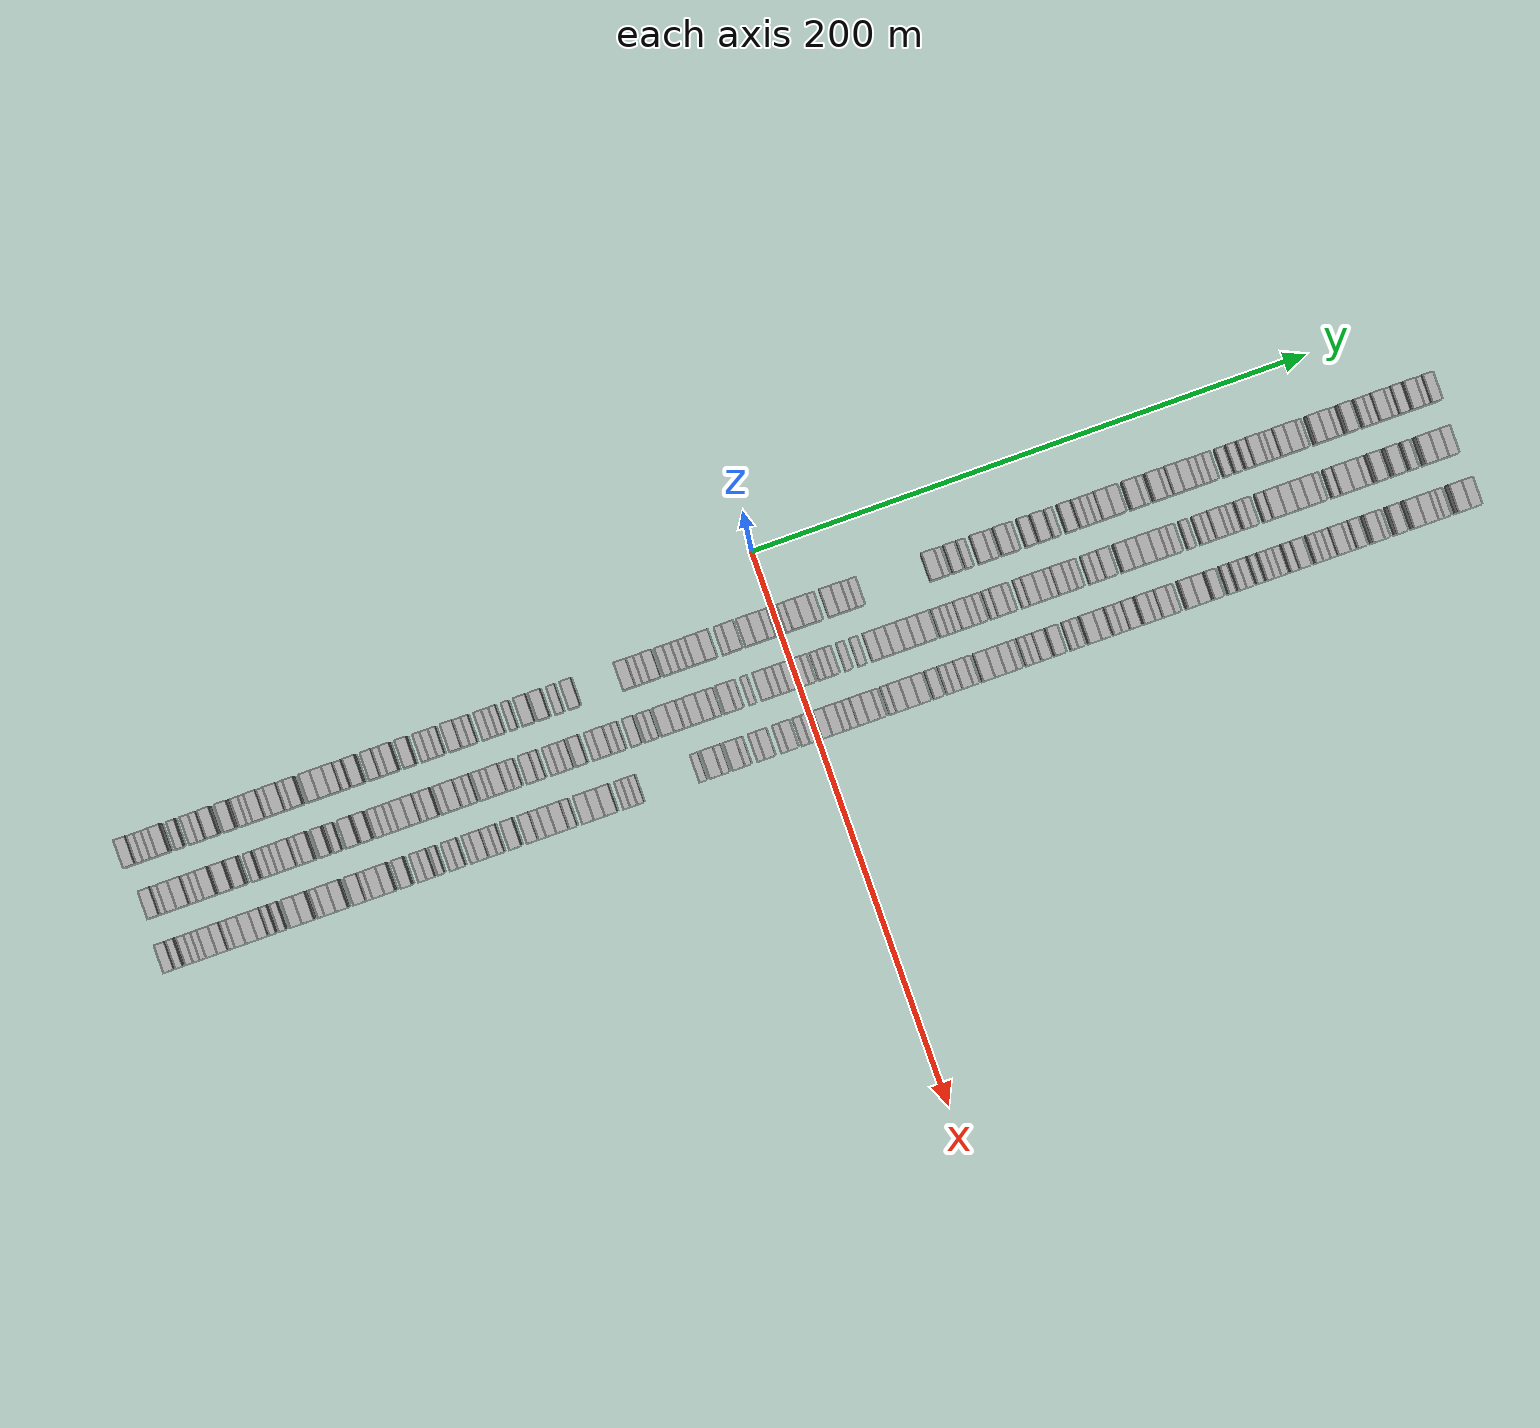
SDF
<sdf version="1.6">
 <world name="default">
  <scene>
   <sky><clouds><speed>12</speed></clouds></sky>
   <ambient>0.4 0.4 0.4 1</ambient>
   <background>0.7 0.7 0.7 1</background>
   <shadows>1</shadows>
  </scene>
  <gravity>0 0 -9.8066</gravity>
  <magnetic_field>6e-06 2.3e-05 -4.2e-05</magnetic_field>
  <physics default="0" name="default_physics" type="ode">
   <ode>
    <solver>
     <type>quick</type>
     <iters>10</iters>
     <sor>1.0</sor>
     <use_dynamic_moi_rescaling>0</use_dynamic_moi_rescaling>
    </solver>
    <constraints>
     <cfm>0</cfm>
     <erp>0.2</erp>
     <contact_max_correcting_vel>100</contact_max_correcting_vel>
     <contact_surface_layer>0.001</contact_surface_layer>
    </constraints>
   </ode>
   <max_step_size>0.004</max_step_size>
   <real_time_factor>1</real_time_factor>
   <real_time_update_rate>250</real_time_update_rate>
  </physics>
  <light name="sun" type="directional">
   <pose>0 0 10 0 0 0</pose>
   <diffuse>0.8 0.8 0.8 1</diffuse>
   <specular>0.2 0.2 0.2 1</specular>
   <attenuation>
    <range>1000</range>
    <constant>0.9</constant>
    <linear>0.01</linear>
    <quadratic>0.001</quadratic>
   </attenuation>
   <direction>-0.5 0.1 -0.9</direction>
  </light>
  <model name="building_1">
   <static>1</static>
   <pose>25.0000 -233.9267 0 0.000000 0.000000 0.000000</pose>
   <link name="link">
    <pose>0 0 4.50 0 0 0</pose>
    <collision name="collision"><geometry><box><size>10.0000 4.1465 9.0000</size></box></geometry></collision>
    <visual name="visual">
     <cast_shadows>0</cast_shadows>
     <geometry><box><size>10.0000 4.1465 9.0000</size></box></geometry>
     <material>
      <script>
       <uri>model://HANNAS_wall/materials/scripts</uri>
       <uri>model://HANNAS_wall/materials/textures</uri>
       <name>vrc/HANNAS_wall</name>
      </script>
     </material>
    </visual>
   </link>
  </model>
  <model name="building_2">
   <static>1</static>
   <pose>25.0000 -230.6240 0 0.000000 0.000000 0.000000</pose>
   <link name="link">
    <pose>0 0 3.00 0 0 0</pose>
    <collision name="collision"><geometry><box><size>10.0000 2.4588 6.0000</size></box></geometry></collision>
    <visual name="visual">
     <cast_shadows>0</cast_shadows>
     <geometry><box><size>10.0000 2.4588 6.0000</size></box></geometry>
     <material>
      <script>
       <uri>model://HANNAS_wall/materials/scripts</uri>
       <uri>model://HANNAS_wall/materials/textures</uri>
       <name>vrc/HANNAS_wall</name>
      </script>
     </material>
    </visual>
   </link>
  </model>
  <model name="building_3">
   <static>1</static>
   <pose>25.0000 -228.0705 0 0.000000 0.000000 0.000000</pose>
   <link name="link">
    <pose>0 0 3.00 0 0 0</pose>
    <collision name="collision"><geometry><box><size>10.0000 2.6482 6.0000</size></box></geometry></collision>
    <visual name="visual">
     <cast_shadows>0</cast_shadows>
     <geometry><box><size>10.0000 2.6482 6.0000</size></box></geometry>
     <material>
      <script>
       <uri>model://HANNAS_wall/materials/scripts</uri>
       <uri>model://HANNAS_wall/materials/textures</uri>
       <name>vrc/HANNAS_wall</name>
      </script>
     </material>
    </visual>
   </link>
  </model>
  <model name="building_4">
   <static>1</static>
   <pose>25.0000 -225.2496 0 0.000000 0.000000 0.000000</pose>
   <link name="link">
    <pose>0 0 3.00 0 0 0</pose>
    <collision name="collision"><geometry><box><size>10.0000 2.9935 6.0000</size></box></geometry></collision>
    <visual name="visual">
     <cast_shadows>0</cast_shadows>
     <geometry><box><size>10.0000 2.9935 6.0000</size></box></geometry>
     <material>
      <script>
       <uri>model://HANNAS_wall/materials/scripts</uri>
       <uri>model://HANNAS_wall/materials/textures</uri>
       <name>vrc/HANNAS_wall</name>
      </script>
     </material>
    </visual>
   </link>
  </model>
  <model name="building_5">
   <static>1</static>
   <pose>25.0000 -221.7155 0 0.000000 0.000000 0.000000</pose>
   <link name="link">
    <pose>0 0 4.50 0 0 0</pose>
    <collision name="collision"><geometry><box><size>10.0000 4.0747 9.0000</size></box></geometry></collision>
    <visual name="visual">
     <cast_shadows>0</cast_shadows>
     <geometry><box><size>10.0000 4.0747 9.0000</size></box></geometry>
     <material>
      <script>
       <uri>model://HANNAS_wall/materials/scripts</uri>
       <uri>model://HANNAS_wall/materials/textures</uri>
       <name>vrc/HANNAS_wall</name>
      </script>
     </material>
    </visual>
   </link>
  </model>
  <model name="building_6">
   <static>1</static>
   <pose>25.0000 -216.2346 0 0.000000 0.000000 0.000000</pose>
   <link name="link">
    <pose>0 0 3.00 0 0 0</pose>
    <collision name="collision"><geometry><box><size>10.0000 2.8871 6.0000</size></box></geometry></collision>
    <visual name="visual">
     <cast_shadows>0</cast_shadows>
     <geometry><box><size>10.0000 2.8871 6.0000</size></box></geometry>
     <material>
      <script>
       <uri>model://HANNAS_wall/materials/scripts</uri>
       <uri>model://HANNAS_wall/materials/textures</uri>
       <name>vrc/HANNAS_wall</name>
      </script>
     </material>
    </visual>
   </link>
  </model>
  <model name="building_7">
   <static>1</static>
   <pose>25.0000 -211.3255 0 0.000000 0.000000 0.000000</pose>
   <link name="link">
    <pose>0 0 3.00 0 0 0</pose>
    <collision name="collision"><geometry><box><size>10.0000 2.9312 6.0000</size></box></geometry></collision>
    <visual name="visual">
     <cast_shadows>0</cast_shadows>
     <geometry><box><size>10.0000 2.9312 6.0000</size></box></geometry>
     <material>
      <script>
       <uri>model://HANNAS_wall/materials/scripts</uri>
       <uri>model://HANNAS_wall/materials/textures</uri>
       <name>vrc/HANNAS_wall</name>
      </script>
     </material>
    </visual>
   </link>
  </model>
  <model name="building_8">
   <static>1</static>
   <pose>25.0000 -208.5059 0 0.000000 0.000000 0.000000</pose>
   <link name="link">
    <pose>0 0 3.00 0 0 0</pose>
    <collision name="collision"><geometry><box><size>10.0000 2.7079 6.0000</size></box></geometry></collision>
    <visual name="visual">
     <cast_shadows>0</cast_shadows>
     <geometry><box><size>10.0000 2.7079 6.0000</size></box></geometry>
     <material>
      <script>
       <uri>model://HANNAS_wall/materials/scripts</uri>
       <uri>model://HANNAS_wall/materials/textures</uri>
       <name>vrc/HANNAS_wall</name>
      </script>
     </material>
    </visual>
   </link>
  </model>
  <model name="building_9">
   <static>1</static>
   <pose>25.0000 -204.0566 0 0.000000 0.000000 0.000000</pose>
   <link name="link">
    <pose>0 0 4.50 0 0 0</pose>
    <collision name="collision"><geometry><box><size>10.0000 4.1907 9.0000</size></box></geometry></collision>
    <visual name="visual">
     <cast_shadows>0</cast_shadows>
     <geometry><box><size>10.0000 4.1907 9.0000</size></box></geometry>
     <material>
      <script>
       <uri>model://HANNAS_wall/materials/scripts</uri>
       <uri>model://HANNAS_wall/materials/textures</uri>
       <name>vrc/HANNAS_wall</name>
      </script>
     </material>
    </visual>
   </link>
  </model>
  <model name="building_10">
   <static>1</static>
   <pose>25.0000 -197.8575 0 0.000000 0.000000 0.000000</pose>
   <link name="link">
    <pose>0 0 4.50 0 0 0</pose>
    <collision name="collision"><geometry><box><size>10.0000 4.2074 9.0000</size></box></geometry></collision>
    <visual name="visual">
     <cast_shadows>0</cast_shadows>
     <geometry><box><size>10.0000 4.2074 9.0000</size></box></geometry>
     <material>
      <script>
       <uri>model://HANNAS_wall/materials/scripts</uri>
       <uri>model://HANNAS_wall/materials/textures</uri>
       <name>vrc/HANNAS_wall</name>
      </script>
     </material>
    </visual>
   </link>
  </model>
  <model name="building_11">
   <static>1</static>
   <pose>25.0000 -193.3624 0 0.000000 0.000000 0.000000</pose>
   <link name="link">
    <pose>0 0 3.00 0 0 0</pose>
    <collision name="collision"><geometry><box><size>10.0000 2.7829 6.0000</size></box></geometry></collision>
    <visual name="visual">
     <cast_shadows>0</cast_shadows>
     <geometry><box><size>10.0000 2.7829 6.0000</size></box></geometry>
     <material>
      <script>
       <uri>model://HANNAS_wall/materials/scripts</uri>
       <uri>model://HANNAS_wall/materials/textures</uri>
       <name>vrc/HANNAS_wall</name>
      </script>
     </material>
    </visual>
   </link>
  </model>
  <model name="building_12">
   <static>1</static>
   <pose>25.0000 -190.7407 0 0.000000 0.000000 0.000000</pose>
   <link name="link">
    <pose>0 0 3.00 0 0 0</pose>
    <collision name="collision"><geometry><box><size>10.0000 2.4604 6.0000</size></box></geometry></collision>
    <visual name="visual">
     <cast_shadows>0</cast_shadows>
     <geometry><box><size>10.0000 2.4604 6.0000</size></box></geometry>
     <material>
      <script>
       <uri>model://HANNAS_wall/materials/scripts</uri>
       <uri>model://HANNAS_wall/materials/textures</uri>
       <name>vrc/HANNAS_wall</name>
      </script>
     </material>
    </visual>
   </link>
  </model>
  <model name="building_13">
   <static>1</static>
   <pose>25.0000 -187.4026 0 0.000000 0.000000 0.000000</pose>
   <link name="link">
    <pose>0 0 4.50 0 0 0</pose>
    <collision name="collision"><geometry><box><size>10.0000 4.2159 9.0000</size></box></geometry></collision>
    <visual name="visual">
     <cast_shadows>0</cast_shadows>
     <geometry><box><size>10.0000 4.2159 9.0000</size></box></geometry>
     <material>
      <script>
       <uri>model://HANNAS_wall/materials/scripts</uri>
       <uri>model://HANNAS_wall/materials/textures</uri>
       <name>vrc/HANNAS_wall</name>
      </script>
     </material>
    </visual>
   </link>
  </model>
  <model name="building_14">
   <static>1</static>
   <pose>25.0000 -183.9094 0 0.000000 0.000000 0.000000</pose>
   <link name="link">
    <pose>0 0 3.00 0 0 0</pose>
    <collision name="collision"><geometry><box><size>10.0000 2.7704 6.0000</size></box></geometry></collision>
    <visual name="visual">
     <cast_shadows>0</cast_shadows>
     <geometry><box><size>10.0000 2.7704 6.0000</size></box></geometry>
     <material>
      <script>
       <uri>model://HANNAS_wall/materials/scripts</uri>
       <uri>model://HANNAS_wall/materials/textures</uri>
       <name>vrc/HANNAS_wall</name>
      </script>
     </material>
    </visual>
   </link>
  </model>
  <model name="building_15">
   <static>1</static>
   <pose>25.0000 -180.2995 0 0.000000 0.000000 0.000000</pose>
   <link name="link">
    <pose>0 0 4.50 0 0 0</pose>
    <collision name="collision"><geometry><box><size>10.0000 4.4495 9.0000</size></box></geometry></collision>
    <visual name="visual">
     <cast_shadows>0</cast_shadows>
     <geometry><box><size>10.0000 4.4495 9.0000</size></box></geometry>
     <material>
      <script>
       <uri>model://HANNAS_wall/materials/scripts</uri>
       <uri>model://HANNAS_wall/materials/textures</uri>
       <name>vrc/HANNAS_wall</name>
      </script>
     </material>
    </visual>
   </link>
  </model>
  <model name="building_16">
   <static>1</static>
   <pose>25.0000 -176.7931 0 0.000000 0.000000 0.000000</pose>
   <link name="link">
    <pose>0 0 3.00 0 0 0</pose>
    <collision name="collision"><geometry><box><size>10.0000 2.5632 6.0000</size></box></geometry></collision>
    <visual name="visual">
     <cast_shadows>0</cast_shadows>
     <geometry><box><size>10.0000 2.5632 6.0000</size></box></geometry>
     <material>
      <script>
       <uri>model://HANNAS_wall/materials/scripts</uri>
       <uri>model://HANNAS_wall/materials/textures</uri>
       <name>vrc/HANNAS_wall</name>
      </script>
     </material>
    </visual>
   </link>
  </model>
  <model name="building_17">
   <static>1</static>
   <pose>25.0000 -173.6158 0 0.000000 0.000000 0.000000</pose>
   <link name="link">
    <pose>0 0 4.50 0 0 0</pose>
    <collision name="collision"><geometry><box><size>10.0000 3.7915 9.0000</size></box></geometry></collision>
    <visual name="visual">
     <cast_shadows>0</cast_shadows>
     <geometry><box><size>10.0000 3.7915 9.0000</size></box></geometry>
     <material>
      <script>
       <uri>model://HANNAS_wall/materials/scripts</uri>
       <uri>model://HANNAS_wall/materials/textures</uri>
       <name>vrc/HANNAS_wall</name>
      </script>
     </material>
    </visual>
   </link>
  </model>
  <model name="building_18">
   <static>1</static>
   <pose>25.0000 -167.7553 0 0.000000 0.000000 0.000000</pose>
   <link name="link">
    <pose>0 0 4.50 0 0 0</pose>
    <collision name="collision"><geometry><box><size>10.0000 3.9295 9.0000</size></box></geometry></collision>
    <visual name="visual">
     <cast_shadows>0</cast_shadows>
     <geometry><box><size>10.0000 3.9295 9.0000</size></box></geometry>
     <material>
      <script>
       <uri>model://HANNAS_wall/materials/scripts</uri>
       <uri>model://HANNAS_wall/materials/textures</uri>
       <name>vrc/HANNAS_wall</name>
      </script>
     </material>
    </visual>
   </link>
  </model>
  <model name="building_19">
   <static>1</static>
   <pose>25.0000 -163.6830 0 0.000000 0.000000 0.000000</pose>
   <link name="link">
    <pose>0 0 4.50 0 0 0</pose>
    <collision name="collision"><geometry><box><size>10.0000 4.2150 9.0000</size></box></geometry></collision>
    <visual name="visual">
     <cast_shadows>0</cast_shadows>
     <geometry><box><size>10.0000 4.2150 9.0000</size></box></geometry>
     <material>
      <script>
       <uri>model://HANNAS_wall/materials/scripts</uri>
       <uri>model://HANNAS_wall/materials/textures</uri>
       <name>vrc/HANNAS_wall</name>
      </script>
     </material>
    </visual>
   </link>
  </model>
  <model name="building_20">
   <static>1</static>
   <pose>25.0000 -159.6829 0 0.000000 0.000000 0.000000</pose>
   <link name="link">
    <pose>0 0 4.50 0 0 0</pose>
    <collision name="collision"><geometry><box><size>10.0000 3.7851 9.0000</size></box></geometry></collision>
    <visual name="visual">
     <cast_shadows>0</cast_shadows>
     <geometry><box><size>10.0000 3.7851 9.0000</size></box></geometry>
     <material>
      <script>
       <uri>model://HANNAS_wall/materials/scripts</uri>
       <uri>model://HANNAS_wall/materials/textures</uri>
       <name>vrc/HANNAS_wall</name>
      </script>
     </material>
    </visual>
   </link>
  </model>
  <model name="building_21">
   <static>1</static>
   <pose>25.0000 -156.4042 0 0.000000 0.000000 0.000000</pose>
   <link name="link">
    <pose>0 0 3.00 0 0 0</pose>
    <collision name="collision"><geometry><box><size>10.0000 2.7723 6.0000</size></box></geometry></collision>
    <visual name="visual">
     <cast_shadows>0</cast_shadows>
     <geometry><box><size>10.0000 2.7723 6.0000</size></box></geometry>
     <material>
      <script>
       <uri>model://HANNAS_wall/materials/scripts</uri>
       <uri>model://HANNAS_wall/materials/textures</uri>
       <name>vrc/HANNAS_wall</name>
      </script>
     </material>
    </visual>
   </link>
  </model>
  <model name="building_22">
   <static>1</static>
   <pose>25.0000 -151.8948 0 0.000000 0.000000 0.000000</pose>
   <link name="link">
    <pose>0 0 4.50 0 0 0</pose>
    <collision name="collision"><geometry><box><size>10.0000 4.2465 9.0000</size></box></geometry></collision>
    <visual name="visual">
     <cast_shadows>0</cast_shadows>
     <geometry><box><size>10.0000 4.2465 9.0000</size></box></geometry>
     <material>
      <script>
       <uri>model://HANNAS_wall/materials/scripts</uri>
       <uri>model://HANNAS_wall/materials/textures</uri>
       <name>vrc/HANNAS_wall</name>
      </script>
     </material>
    </visual>
   </link>
  </model>
  <model name="building_23">
   <static>1</static>
   <pose>25.0000 -145.8462 0 0.000000 0.000000 0.000000</pose>
   <link name="link">
    <pose>0 0 4.50 0 0 0</pose>
    <collision name="collision"><geometry><box><size>10.0000 3.8509 9.0000</size></box></geometry></collision>
    <visual name="visual">
     <cast_shadows>0</cast_shadows>
     <geometry><box><size>10.0000 3.8509 9.0000</size></box></geometry>
     <material>
      <script>
       <uri>model://HANNAS_wall/materials/scripts</uri>
       <uri>model://HANNAS_wall/materials/textures</uri>
       <name>vrc/HANNAS_wall</name>
      </script>
     </material>
    </visual>
   </link>
  </model>
  <model name="building_24">
   <static>1</static>
   <pose>25.0000 -142.5342 0 0.000000 0.000000 0.000000</pose>
   <link name="link">
    <pose>0 0 3.00 0 0 0</pose>
    <collision name="collision"><geometry><box><size>10.0000 2.7730 6.0000</size></box></geometry></collision>
    <visual name="visual">
     <cast_shadows>0</cast_shadows>
     <geometry><box><size>10.0000 2.7730 6.0000</size></box></geometry>
     <material>
      <script>
       <uri>model://HANNAS_wall/materials/scripts</uri>
       <uri>model://HANNAS_wall/materials/textures</uri>
       <name>vrc/HANNAS_wall</name>
      </script>
     </material>
    </visual>
   </link>
  </model>
  <model name="building_25">
   <static>1</static>
   <pose>25.0000 -139.2544 0 0.000000 0.000000 0.000000</pose>
   <link name="link">
    <pose>0 0 4.50 0 0 0</pose>
    <collision name="collision"><geometry><box><size>10.0000 3.7864 9.0000</size></box></geometry></collision>
    <visual name="visual">
     <cast_shadows>0</cast_shadows>
     <geometry><box><size>10.0000 3.7864 9.0000</size></box></geometry>
     <material>
      <script>
       <uri>model://HANNAS_wall/materials/scripts</uri>
       <uri>model://HANNAS_wall/materials/textures</uri>
       <name>vrc/HANNAS_wall</name>
      </script>
     </material>
    </visual>
   </link>
  </model>
  <model name="building_26">
   <static>1</static>
   <pose>25.0000 -133.3032 0 0.000000 0.000000 0.000000</pose>
   <link name="link">
    <pose>0 0 4.50 0 0 0</pose>
    <collision name="collision"><geometry><box><size>10.0000 4.1161 9.0000</size></box></geometry></collision>
    <visual name="visual">
     <cast_shadows>0</cast_shadows>
     <geometry><box><size>10.0000 4.1161 9.0000</size></box></geometry>
     <material>
      <script>
       <uri>model://HANNAS_wall/materials/scripts</uri>
       <uri>model://HANNAS_wall/materials/textures</uri>
       <name>vrc/HANNAS_wall</name>
      </script>
     </material>
    </visual>
   </link>
  </model>
  <model name="building_27">
   <static>1</static>
   <pose>25.0000 -127.9376 0 0.000000 0.000000 0.000000</pose>
   <link name="link">
    <pose>0 0 3.00 0 0 0</pose>
    <collision name="collision"><geometry><box><size>10.0000 2.6151 6.0000</size></box></geometry></collision>
    <visual name="visual">
     <cast_shadows>0</cast_shadows>
     <geometry><box><size>10.0000 2.6151 6.0000</size></box></geometry>
     <material>
      <script>
       <uri>model://HANNAS_wall/materials/scripts</uri>
       <uri>model://HANNAS_wall/materials/textures</uri>
       <name>vrc/HANNAS_wall</name>
      </script>
     </material>
    </visual>
   </link>
  </model>
  <model name="building_28">
   <static>1</static>
   <pose>25.0000 -125.1480 0 0.000000 0.000000 0.000000</pose>
   <link name="link">
    <pose>0 0 3.00 0 0 0</pose>
    <collision name="collision"><geometry><box><size>10.0000 2.9643 6.0000</size></box></geometry></collision>
    <visual name="visual">
     <cast_shadows>0</cast_shadows>
     <geometry><box><size>10.0000 2.9643 6.0000</size></box></geometry>
     <material>
      <script>
       <uri>model://HANNAS_wall/materials/scripts</uri>
       <uri>model://HANNAS_wall/materials/textures</uri>
       <name>vrc/HANNAS_wall</name>
      </script>
     </material>
    </visual>
   </link>
  </model>
  <model name="building_29">
   <static>1</static>
   <pose>25.0000 -122.3587 0 0.000000 0.000000 0.000000</pose>
   <link name="link">
    <pose>0 0 3.00 0 0 0</pose>
    <collision name="collision"><geometry><box><size>10.0000 2.6142 6.0000</size></box></geometry></collision>
    <visual name="visual">
     <cast_shadows>0</cast_shadows>
     <geometry><box><size>10.0000 2.6142 6.0000</size></box></geometry>
     <material>
      <script>
       <uri>model://HANNAS_wall/materials/scripts</uri>
       <uri>model://HANNAS_wall/materials/textures</uri>
       <name>vrc/HANNAS_wall</name>
      </script>
     </material>
    </visual>
   </link>
  </model>
  <model name="building_30">
   <static>1</static>
   <pose>25.0000 -116.9087 0 0.000000 0.000000 0.000000</pose>
   <link name="link">
    <pose>0 0 4.50 0 0 0</pose>
    <collision name="collision"><geometry><box><size>10.0000 4.2858 9.0000</size></box></geometry></collision>
    <visual name="visual">
     <cast_shadows>0</cast_shadows>
     <geometry><box><size>10.0000 4.2858 9.0000</size></box></geometry>
     <material>
      <script>
       <uri>model://HANNAS_wall/materials/scripts</uri>
       <uri>model://HANNAS_wall/materials/textures</uri>
       <name>vrc/HANNAS_wall</name>
      </script>
     </material>
    </visual>
   </link>
  </model>
  <model name="building_31">
   <static>1</static>
   <pose>25.0000 -113.3507 0 0.000000 0.000000 0.000000</pose>
   <link name="link">
    <pose>0 0 3.00 0 0 0</pose>
    <collision name="collision"><geometry><box><size>10.0000 2.8301 6.0000</size></box></geometry></collision>
    <visual name="visual">
     <cast_shadows>0</cast_shadows>
     <geometry><box><size>10.0000 2.8301 6.0000</size></box></geometry>
     <material>
      <script>
       <uri>model://HANNAS_wall/materials/scripts</uri>
       <uri>model://HANNAS_wall/materials/textures</uri>
       <name>vrc/HANNAS_wall</name>
      </script>
     </material>
    </visual>
   </link>
  </model>
  <model name="building_32">
   <static>1</static>
   <pose>25.0000 -110.6282 0 0.000000 0.000000 0.000000</pose>
   <link name="link">
    <pose>0 0 3.00 0 0 0</pose>
    <collision name="collision"><geometry><box><size>10.0000 2.6151 6.0000</size></box></geometry></collision>
    <visual name="visual">
     <cast_shadows>0</cast_shadows>
     <geometry><box><size>10.0000 2.6151 6.0000</size></box></geometry>
     <material>
      <script>
       <uri>model://HANNAS_wall/materials/scripts</uri>
       <uri>model://HANNAS_wall/materials/textures</uri>
       <name>vrc/HANNAS_wall</name>
      </script>
     </material>
    </visual>
   </link>
  </model>
  <model name="building_33">
   <static>1</static>
   <pose>25.0000 -105.8945 0 0.000000 0.000000 0.000000</pose>
   <link name="link">
    <pose>0 0 3.00 0 0 0</pose>
    <collision name="collision"><geometry><box><size>10.0000 2.8522 6.0000</size></box></geometry></collision>
    <visual name="visual">
     <cast_shadows>0</cast_shadows>
     <geometry><box><size>10.0000 2.8522 6.0000</size></box></geometry>
     <material>
      <script>
       <uri>model://HANNAS_wall/materials/scripts</uri>
       <uri>model://HANNAS_wall/materials/textures</uri>
       <name>vrc/HANNAS_wall</name>
      </script>
     </material>
    </visual>
   </link>
  </model>
  <model name="building_34">
   <static>1</static>
   <pose>25.0000 -103.2093 0 0.000000 0.000000 0.000000</pose>
   <link name="link">
    <pose>0 0 3.00 0 0 0</pose>
    <collision name="collision"><geometry><box><size>10.0000 2.5183 6.0000</size></box></geometry></collision>
    <visual name="visual">
     <cast_shadows>0</cast_shadows>
     <geometry><box><size>10.0000 2.5183 6.0000</size></box></geometry>
     <material>
      <script>
       <uri>model://HANNAS_wall/materials/scripts</uri>
       <uri>model://HANNAS_wall/materials/textures</uri>
       <name>vrc/HANNAS_wall</name>
      </script>
     </material>
    </visual>
   </link>
  </model>
  <model name="building_35">
   <static>1</static>
   <pose>25.0000 -100.7163 0 0.000000 0.000000 0.000000</pose>
   <link name="link">
    <pose>0 0 3.00 0 0 0</pose>
    <collision name="collision"><geometry><box><size>10.0000 2.4675 6.0000</size></box></geometry></collision>
    <visual name="visual">
     <cast_shadows>0</cast_shadows>
     <geometry><box><size>10.0000 2.4675 6.0000</size></box></geometry>
     <material>
      <script>
       <uri>model://HANNAS_wall/materials/scripts</uri>
       <uri>model://HANNAS_wall/materials/textures</uri>
       <name>vrc/HANNAS_wall</name>
      </script>
     </material>
    </visual>
   </link>
  </model>
  <model name="building_36">
   <static>1</static>
   <pose>25.0000 -96.1519 0 0.000000 0.000000 0.000000</pose>
   <link name="link">
    <pose>0 0 3.00 0 0 0</pose>
    <collision name="collision"><geometry><box><size>10.0000 2.6613 6.0000</size></box></geometry></collision>
    <visual name="visual">
     <cast_shadows>0</cast_shadows>
     <geometry><box><size>10.0000 2.6613 6.0000</size></box></geometry>
     <material>
      <script>
       <uri>model://HANNAS_wall/materials/scripts</uri>
       <uri>model://HANNAS_wall/materials/textures</uri>
       <name>vrc/HANNAS_wall</name>
      </script>
     </material>
    </visual>
   </link>
  </model>
  <model name="building_37">
   <static>1</static>
   <pose>25.0000 -90.6759 0 0.000000 0.000000 0.000000</pose>
   <link name="link">
    <pose>0 0 4.50 0 0 0</pose>
    <collision name="collision"><geometry><box><size>10.0000 4.2906 9.0000</size></box></geometry></collision>
    <visual name="visual">
     <cast_shadows>0</cast_shadows>
     <geometry><box><size>10.0000 4.2906 9.0000</size></box></geometry>
     <material>
      <script>
       <uri>model://HANNAS_wall/materials/scripts</uri>
       <uri>model://HANNAS_wall/materials/textures</uri>
       <name>vrc/HANNAS_wall</name>
      </script>
     </material>
    </visual>
   </link>
  </model>
  <model name="building_38">
   <static>1</static>
   <pose>25.0000 -85.3787 0 0.000000 0.000000 0.000000</pose>
   <link name="link">
    <pose>0 0 4.50 0 0 0</pose>
    <collision name="collision"><geometry><box><size>10.0000 4.3038 9.0000</size></box></geometry></collision>
    <visual name="visual">
     <cast_shadows>0</cast_shadows>
     <geometry><box><size>10.0000 4.3038 9.0000</size></box></geometry>
     <material>
      <script>
       <uri>model://HANNAS_wall/materials/scripts</uri>
       <uri>model://HANNAS_wall/materials/textures</uri>
       <name>vrc/HANNAS_wall</name>
      </script>
     </material>
    </visual>
   </link>
  </model>
  <model name="building_39">
   <static>1</static>
   <pose>25.0000 -79.7324 0 0.000000 0.000000 0.000000</pose>
   <link name="link">
    <pose>0 0 3.00 0 0 0</pose>
    <collision name="collision"><geometry><box><size>10.0000 2.9890 6.0000</size></box></geometry></collision>
    <visual name="visual">
     <cast_shadows>0</cast_shadows>
     <geometry><box><size>10.0000 2.9890 6.0000</size></box></geometry>
     <material>
      <script>
       <uri>model://HANNAS_wall/materials/scripts</uri>
       <uri>model://HANNAS_wall/materials/textures</uri>
       <name>vrc/HANNAS_wall</name>
      </script>
     </material>
    </visual>
   </link>
  </model>
  <model name="building_40">
   <static>1</static>
   <pose>25.0000 -74.2190 0 0.000000 0.000000 0.000000</pose>
   <link name="link">
    <pose>0 0 4.50 0 0 0</pose>
    <collision name="collision"><geometry><box><size>10.0000 4.0378 9.0000</size></box></geometry></collision>
    <visual name="visual">
     <cast_shadows>0</cast_shadows>
     <geometry><box><size>10.0000 4.0378 9.0000</size></box></geometry>
     <material>
      <script>
       <uri>model://HANNAS_wall/materials/scripts</uri>
       <uri>model://HANNAS_wall/materials/textures</uri>
       <name>vrc/HANNAS_wall</name>
      </script>
     </material>
    </visual>
   </link>
  </model>
  <model name="building_41">
   <static>1</static>
   <pose>25.0000 -54.6580 0 0.000000 0.000000 0.000000</pose>
   <link name="link">
    <pose>0 0 4.50 0 0 0</pose>
    <collision name="collision"><geometry><box><size>10.0000 4.3614 9.0000</size></box></geometry></collision>
    <visual name="visual">
     <cast_shadows>0</cast_shadows>
     <geometry><box><size>10.0000 4.3614 9.0000</size></box></geometry>
     <material>
      <script>
       <uri>model://HANNAS_wall/materials/scripts</uri>
       <uri>model://HANNAS_wall/materials/textures</uri>
       <name>vrc/HANNAS_wall</name>
      </script>
     </material>
    </visual>
   </link>
  </model>
  <model name="building_42">
   <static>1</static>
   <pose>25.0000 -51.2182 0 0.000000 0.000000 0.000000</pose>
   <link name="link">
    <pose>0 0 3.00 0 0 0</pose>
    <collision name="collision"><geometry><box><size>10.0000 2.5180 6.0000</size></box></geometry></collision>
    <visual name="visual">
     <cast_shadows>0</cast_shadows>
     <geometry><box><size>10.0000 2.5180 6.0000</size></box></geometry>
     <material>
      <script>
       <uri>model://HANNAS_wall/materials/scripts</uri>
       <uri>model://HANNAS_wall/materials/textures</uri>
       <name>vrc/HANNAS_wall</name>
      </script>
     </material>
    </visual>
   </link>
  </model>
  <model name="building_43">
   <static>1</static>
   <pose>25.0000 -48.5758 0 0.000000 0.000000 0.000000</pose>
   <link name="link">
    <pose>0 0 3.00 0 0 0</pose>
    <collision name="collision"><geometry><box><size>10.0000 2.7668 6.0000</size></box></geometry></collision>
    <visual name="visual">
     <cast_shadows>0</cast_shadows>
     <geometry><box><size>10.0000 2.7668 6.0000</size></box></geometry>
     <material>
      <script>
       <uri>model://HANNAS_wall/materials/scripts</uri>
       <uri>model://HANNAS_wall/materials/textures</uri>
       <name>vrc/HANNAS_wall</name>
      </script>
     </material>
    </visual>
   </link>
  </model>
  <model name="building_44">
   <static>1</static>
   <pose>25.0000 -45.2678 0 0.000000 0.000000 0.000000</pose>
   <link name="link">
    <pose>0 0 4.50 0 0 0</pose>
    <collision name="collision"><geometry><box><size>10.0000 3.8492 9.0000</size></box></geometry></collision>
    <visual name="visual">
     <cast_shadows>0</cast_shadows>
     <geometry><box><size>10.0000 3.8492 9.0000</size></box></geometry>
     <material>
      <script>
       <uri>model://HANNAS_wall/materials/scripts</uri>
       <uri>model://HANNAS_wall/materials/textures</uri>
       <name>vrc/HANNAS_wall</name>
      </script>
     </material>
    </visual>
   </link>
  </model>
  <model name="building_45">
   <static>1</static>
   <pose>25.0000 -40.8838 0 0.000000 0.000000 0.000000</pose>
   <link name="link">
    <pose>0 0 3.00 0 0 0</pose>
    <collision name="collision"><geometry><box><size>10.0000 2.9189 6.0000</size></box></geometry></collision>
    <visual name="visual">
     <cast_shadows>0</cast_shadows>
     <geometry><box><size>10.0000 2.9189 6.0000</size></box></geometry>
     <material>
      <script>
       <uri>model://HANNAS_wall/materials/scripts</uri>
       <uri>model://HANNAS_wall/materials/textures</uri>
       <name>vrc/HANNAS_wall</name>
      </script>
     </material>
    </visual>
   </link>
  </model>
  <model name="building_46">
   <static>1</static>
   <pose>25.0000 -38.0021 0 0.000000 0.000000 0.000000</pose>
   <link name="link">
    <pose>0 0 3.00 0 0 0</pose>
    <collision name="collision"><geometry><box><size>10.0000 2.8446 6.0000</size></box></geometry></collision>
    <visual name="visual">
     <cast_shadows>0</cast_shadows>
     <geometry><box><size>10.0000 2.8446 6.0000</size></box></geometry>
     <material>
      <script>
       <uri>model://HANNAS_wall/materials/scripts</uri>
       <uri>model://HANNAS_wall/materials/textures</uri>
       <name>vrc/HANNAS_wall</name>
      </script>
     </material>
    </visual>
   </link>
  </model>
  <model name="building_47">
   <static>1</static>
   <pose>25.0000 -35.2692 0 0.000000 0.000000 0.000000</pose>
   <link name="link">
    <pose>0 0 3.00 0 0 0</pose>
    <collision name="collision"><geometry><box><size>10.0000 2.6212 6.0000</size></box></geometry></collision>
    <visual name="visual">
     <cast_shadows>0</cast_shadows>
     <geometry><box><size>10.0000 2.6212 6.0000</size></box></geometry>
     <material>
      <script>
       <uri>model://HANNAS_wall/materials/scripts</uri>
       <uri>model://HANNAS_wall/materials/textures</uri>
       <name>vrc/HANNAS_wall</name>
      </script>
     </material>
    </visual>
   </link>
  </model>
  <model name="building_48">
   <static>1</static>
   <pose>25.0000 -32.6886 0 0.000000 0.000000 0.000000</pose>
   <link name="link">
    <pose>0 0 3.00 0 0 0</pose>
    <collision name="collision"><geometry><box><size>10.0000 2.5400 6.0000</size></box></geometry></collision>
    <visual name="visual">
     <cast_shadows>0</cast_shadows>
     <geometry><box><size>10.0000 2.5400 6.0000</size></box></geometry>
     <material>
      <script>
       <uri>model://HANNAS_wall/materials/scripts</uri>
       <uri>model://HANNAS_wall/materials/textures</uri>
       <name>vrc/HANNAS_wall</name>
      </script>
     </material>
    </visual>
   </link>
  </model>
  <model name="building_49">
   <static>1</static>
   <pose>25.0000 -29.2893 0 0.000000 0.000000 0.000000</pose>
   <link name="link">
    <pose>0 0 4.50 0 0 0</pose>
    <collision name="collision"><geometry><box><size>10.0000 4.2587 9.0000</size></box></geometry></collision>
    <visual name="visual">
     <cast_shadows>0</cast_shadows>
     <geometry><box><size>10.0000 4.2587 9.0000</size></box></geometry>
     <material>
      <script>
       <uri>model://HANNAS_wall/materials/scripts</uri>
       <uri>model://HANNAS_wall/materials/textures</uri>
       <name>vrc/HANNAS_wall</name>
      </script>
     </material>
    </visual>
   </link>
  </model>
  <model name="building_50">
   <static>1</static>
   <pose>25.0000 -25.1288 0 0.000000 0.000000 0.000000</pose>
   <link name="link">
    <pose>0 0 4.50 0 0 0</pose>
    <collision name="collision"><geometry><box><size>10.0000 4.0623 9.0000</size></box></geometry></collision>
    <visual name="visual">
     <cast_shadows>0</cast_shadows>
     <geometry><box><size>10.0000 4.0623 9.0000</size></box></geometry>
     <material>
      <script>
       <uri>model://HANNAS_wall/materials/scripts</uri>
       <uri>model://HANNAS_wall/materials/textures</uri>
       <name>vrc/HANNAS_wall</name>
      </script>
     </material>
    </visual>
   </link>
  </model>
  <model name="building_51">
   <static>1</static>
   <pose>25.0000 -19.7349 0 0.000000 0.000000 0.000000</pose>
   <link name="link">
    <pose>0 0 3.00 0 0 0</pose>
    <collision name="collision"><geometry><box><size>10.0000 2.7254 6.0000</size></box></geometry></collision>
    <visual name="visual">
     <cast_shadows>0</cast_shadows>
     <geometry><box><size>10.0000 2.7254 6.0000</size></box></geometry>
     <material>
      <script>
       <uri>model://HANNAS_wall/materials/scripts</uri>
       <uri>model://HANNAS_wall/materials/textures</uri>
       <name>vrc/HANNAS_wall</name>
      </script>
     </material>
    </visual>
   </link>
  </model>
  <model name="building_52">
   <static>1</static>
   <pose>25.0000 -16.1695 0 0.000000 0.000000 0.000000</pose>
   <link name="link">
    <pose>0 0 4.50 0 0 0</pose>
    <collision name="collision"><geometry><box><size>10.0000 4.4054 9.0000</size></box></geometry></collision>
    <visual name="visual">
     <cast_shadows>0</cast_shadows>
     <geometry><box><size>10.0000 4.4054 9.0000</size></box></geometry>
     <material>
      <script>
       <uri>model://HANNAS_wall/materials/scripts</uri>
       <uri>model://HANNAS_wall/materials/textures</uri>
       <name>vrc/HANNAS_wall</name>
      </script>
     </material>
    </visual>
   </link>
  </model>
  <model name="building_53">
   <static>1</static>
   <pose>25.0000 -11.0541 0 0.000000 0.000000 0.000000</pose>
   <link name="link">
    <pose>0 0 4.50 0 0 0</pose>
    <collision name="collision"><geometry><box><size>10.0000 3.8252 9.0000</size></box></geometry></collision>
    <visual name="visual">
     <cast_shadows>0</cast_shadows>
     <geometry><box><size>10.0000 3.8252 9.0000</size></box></geometry>
     <material>
      <script>
       <uri>model://HANNAS_wall/materials/scripts</uri>
       <uri>model://HANNAS_wall/materials/textures</uri>
       <name>vrc/HANNAS_wall</name>
      </script>
     </material>
    </visual>
   </link>
  </model>
  <model name="building_54">
   <static>1</static>
   <pose>25.0000 -6.9737 0 0.000000 0.000000 0.000000</pose>
   <link name="link">
    <pose>0 0 4.50 0 0 0</pose>
    <collision name="collision"><geometry><box><size>10.0000 4.3355 9.0000</size></box></geometry></collision>
    <visual name="visual">
     <cast_shadows>0</cast_shadows>
     <geometry><box><size>10.0000 4.3355 9.0000</size></box></geometry>
     <material>
      <script>
       <uri>model://HANNAS_wall/materials/scripts</uri>
       <uri>model://HANNAS_wall/materials/textures</uri>
       <name>vrc/HANNAS_wall</name>
      </script>
     </material>
    </visual>
   </link>
  </model>
  <model name="building_55">
   <static>1</static>
   <pose>25.0000 -3.4249 0 0.000000 0.000000 0.000000</pose>
   <link name="link">
    <pose>0 0 3.00 0 0 0</pose>
    <collision name="collision"><geometry><box><size>10.0000 2.7622 6.0000</size></box></geometry></collision>
    <visual name="visual">
     <cast_shadows>0</cast_shadows>
     <geometry><box><size>10.0000 2.7622 6.0000</size></box></geometry>
     <material>
      <script>
       <uri>model://HANNAS_wall/materials/scripts</uri>
       <uri>model://HANNAS_wall/materials/textures</uri>
       <name>vrc/HANNAS_wall</name>
      </script>
     </material>
    </visual>
   </link>
  </model>
  <model name="building_56">
   <static>1</static>
   <pose>25.0000 -0.1974 0 0.000000 0.000000 0.000000</pose>
   <link name="link">
    <pose>0 0 4.50 0 0 0</pose>
    <collision name="collision"><geometry><box><size>10.0000 3.6928 9.0000</size></box></geometry></collision>
    <visual name="visual">
     <cast_shadows>0</cast_shadows>
     <geometry><box><size>10.0000 3.6928 9.0000</size></box></geometry>
     <material>
      <script>
       <uri>model://HANNAS_wall/materials/scripts</uri>
       <uri>model://HANNAS_wall/materials/textures</uri>
       <name>vrc/HANNAS_wall</name>
      </script>
     </material>
    </visual>
   </link>
  </model>
  <model name="building_57">
   <static>1</static>
   <pose>25.0000 2.8572 0 0.000000 0.000000 0.000000</pose>
   <link name="link">
    <pose>0 0 3.00 0 0 0</pose>
    <collision name="collision"><geometry><box><size>10.0000 2.4165 6.0000</size></box></geometry></collision>
    <visual name="visual">
     <cast_shadows>0</cast_shadows>
     <geometry><box><size>10.0000 2.4165 6.0000</size></box></geometry>
     <material>
      <script>
       <uri>model://HANNAS_wall/materials/scripts</uri>
       <uri>model://HANNAS_wall/materials/textures</uri>
       <name>vrc/HANNAS_wall</name>
      </script>
     </material>
    </visual>
   </link>
  </model>
  <model name="building_58">
   <static>1</static>
   <pose>25.0000 6.0572 0 0.000000 0.000000 0.000000</pose>
   <link name="link">
    <pose>0 0 4.50 0 0 0</pose>
    <collision name="collision"><geometry><box><size>10.0000 3.9834 9.0000</size></box></geometry></collision>
    <visual name="visual">
     <cast_shadows>0</cast_shadows>
     <geometry><box><size>10.0000 3.9834 9.0000</size></box></geometry>
     <material>
      <script>
       <uri>model://HANNAS_wall/materials/scripts</uri>
       <uri>model://HANNAS_wall/materials/textures</uri>
       <name>vrc/HANNAS_wall</name>
      </script>
     </material>
    </visual>
   </link>
  </model>
  <model name="building_59">
   <static>1</static>
   <pose>25.0000 10.2178 0 0.000000 0.000000 0.000000</pose>
   <link name="link">
    <pose>0 0 4.50 0 0 0</pose>
    <collision name="collision"><geometry><box><size>10.0000 4.3378 9.0000</size></box></geometry></collision>
    <visual name="visual">
     <cast_shadows>0</cast_shadows>
     <geometry><box><size>10.0000 4.3378 9.0000</size></box></geometry>
     <material>
      <script>
       <uri>model://HANNAS_wall/materials/scripts</uri>
       <uri>model://HANNAS_wall/materials/textures</uri>
       <name>vrc/HANNAS_wall</name>
      </script>
     </material>
    </visual>
   </link>
  </model>
  <model name="building_60">
   <static>1</static>
   <pose>25.0000 13.6770 0 0.000000 0.000000 0.000000</pose>
   <link name="link">
    <pose>0 0 3.00 0 0 0</pose>
    <collision name="collision"><geometry><box><size>10.0000 2.5806 6.0000</size></box></geometry></collision>
    <visual name="visual">
     <cast_shadows>0</cast_shadows>
     <geometry><box><size>10.0000 2.5806 6.0000</size></box></geometry>
     <material>
      <script>
       <uri>model://HANNAS_wall/materials/scripts</uri>
       <uri>model://HANNAS_wall/materials/textures</uri>
       <name>vrc/HANNAS_wall</name>
      </script>
     </material>
    </visual>
   </link>
  </model>
  <model name="building_61">
   <static>1</static>
   <pose>25.0000 18.8721 0 0.000000 0.000000 0.000000</pose>
   <link name="link">
    <pose>0 0 4.50 0 0 0</pose>
    <collision name="collision"><geometry><box><size>10.0000 3.8097 9.0000</size></box></geometry></collision>
    <visual name="visual">
     <cast_shadows>0</cast_shadows>
     <geometry><box><size>10.0000 3.8097 9.0000</size></box></geometry>
     <material>
      <script>
       <uri>model://HANNAS_wall/materials/scripts</uri>
       <uri>model://HANNAS_wall/materials/textures</uri>
       <name>vrc/HANNAS_wall</name>
      </script>
     </material>
    </visual>
   </link>
  </model>
  <model name="building_62">
   <static>1</static>
   <pose>25.0000 22.6075 0 0.000000 0.000000 0.000000</pose>
   <link name="link">
    <pose>0 0 4.50 0 0 0</pose>
    <collision name="collision"><geometry><box><size>10.0000 3.6612 9.0000</size></box></geometry></collision>
    <visual name="visual">
     <cast_shadows>0</cast_shadows>
     <geometry><box><size>10.0000 3.6612 9.0000</size></box></geometry>
     <material>
      <script>
       <uri>model://HANNAS_wall/materials/scripts</uri>
       <uri>model://HANNAS_wall/materials/textures</uri>
       <name>vrc/HANNAS_wall</name>
      </script>
     </material>
    </visual>
   </link>
  </model>
  <model name="building_63">
   <static>1</static>
   <pose>25.0000 25.7609 0 0.000000 0.000000 0.000000</pose>
   <link name="link">
    <pose>0 0 3.00 0 0 0</pose>
    <collision name="collision"><geometry><box><size>10.0000 2.6454 6.0000</size></box></geometry></collision>
    <visual name="visual">
     <cast_shadows>0</cast_shadows>
     <geometry><box><size>10.0000 2.6454 6.0000</size></box></geometry>
     <material>
      <script>
       <uri>model://HANNAS_wall/materials/scripts</uri>
       <uri>model://HANNAS_wall/materials/textures</uri>
       <name>vrc/HANNAS_wall</name>
      </script>
     </material>
    </visual>
   </link>
  </model>
  <model name="building_64">
   <static>1</static>
   <pose>25.0000 28.5538 0 0.000000 0.000000 0.000000</pose>
   <link name="link">
    <pose>0 0 3.00 0 0 0</pose>
    <collision name="collision"><geometry><box><size>10.0000 2.9404 6.0000</size></box></geometry></collision>
    <visual name="visual">
     <cast_shadows>0</cast_shadows>
     <geometry><box><size>10.0000 2.9404 6.0000</size></box></geometry>
     <material>
      <script>
       <uri>model://HANNAS_wall/materials/scripts</uri>
       <uri>model://HANNAS_wall/materials/textures</uri>
       <name>vrc/HANNAS_wall</name>
      </script>
     </material>
    </visual>
   </link>
  </model>
  <model name="building_65">
   <static>1</static>
   <pose>25.0000 55.7712 0 0.000000 0.000000 0.000000</pose>
   <link name="link">
    <pose>0 0 4.50 0 0 0</pose>
    <collision name="collision"><geometry><box><size>10.0000 4.4981 9.0000</size></box></geometry></collision>
    <visual name="visual">
     <cast_shadows>0</cast_shadows>
     <geometry><box><size>10.0000 4.4981 9.0000</size></box></geometry>
     <material>
      <script>
       <uri>model://HANNAS_wall/materials/scripts</uri>
       <uri>model://HANNAS_wall/materials/textures</uri>
       <name>vrc/HANNAS_wall</name>
      </script>
     </material>
    </visual>
   </link>
  </model>
  <model name="building_66">
   <static>1</static>
   <pose>25.0000 59.3124 0 0.000000 0.000000 0.000000</pose>
   <link name="link">
    <pose>0 0 3.00 0 0 0</pose>
    <collision name="collision"><geometry><box><size>10.0000 2.5843 6.0000</size></box></geometry></collision>
    <visual name="visual">
     <cast_shadows>0</cast_shadows>
     <geometry><box><size>10.0000 2.5843 6.0000</size></box></geometry>
     <material>
      <script>
       <uri>model://HANNAS_wall/materials/scripts</uri>
       <uri>model://HANNAS_wall/materials/textures</uri>
       <name>vrc/HANNAS_wall</name>
      </script>
     </material>
    </visual>
   </link>
  </model>
  <model name="building_67">
   <static>1</static>
   <pose>25.0000 63.4553 0 0.000000 0.000000 0.000000</pose>
   <link name="link">
    <pose>0 0 4.50 0 0 0</pose>
    <collision name="collision"><geometry><box><size>10.0000 3.7016 9.0000</size></box></geometry></collision>
    <visual name="visual">
     <cast_shadows>0</cast_shadows>
     <geometry><box><size>10.0000 3.7016 9.0000</size></box></geometry>
     <material>
      <script>
       <uri>model://HANNAS_wall/materials/scripts</uri>
       <uri>model://HANNAS_wall/materials/textures</uri>
       <name>vrc/HANNAS_wall</name>
      </script>
     </material>
    </visual>
   </link>
  </model>
  <model name="building_68">
   <static>1</static>
   <pose>25.0000 67.6899 0 0.000000 0.000000 0.000000</pose>
   <link name="link">
    <pose>0 0 3.00 0 0 0</pose>
    <collision name="collision"><geometry><box><size>10.0000 2.7675 6.0000</size></box></geometry></collision>
    <visual name="visual">
     <cast_shadows>0</cast_shadows>
     <geometry><box><size>10.0000 2.7675 6.0000</size></box></geometry>
     <material>
      <script>
       <uri>model://HANNAS_wall/materials/scripts</uri>
       <uri>model://HANNAS_wall/materials/textures</uri>
       <name>vrc/HANNAS_wall</name>
      </script>
     </material>
    </visual>
   </link>
  </model>
  <model name="building_69">
   <static>1</static>
   <pose>25.0000 73.2490 0 0.000000 0.000000 0.000000</pose>
   <link name="link">
    <pose>0 0 4.50 0 0 0</pose>
    <collision name="collision"><geometry><box><size>10.0000 4.3506 9.0000</size></box></geometry></collision>
    <visual name="visual">
     <cast_shadows>0</cast_shadows>
     <geometry><box><size>10.0000 4.3506 9.0000</size></box></geometry>
     <material>
      <script>
       <uri>model://HANNAS_wall/materials/scripts</uri>
       <uri>model://HANNAS_wall/materials/textures</uri>
       <name>vrc/HANNAS_wall</name>
      </script>
     </material>
    </visual>
   </link>
  </model>
  <model name="building_70">
   <static>1</static>
   <pose>25.0000 76.8722 0 0.000000 0.000000 0.000000</pose>
   <link name="link">
    <pose>0 0 3.00 0 0 0</pose>
    <collision name="collision"><geometry><box><size>10.0000 2.8959 6.0000</size></box></geometry></collision>
    <visual name="visual">
     <cast_shadows>0</cast_shadows>
     <geometry><box><size>10.0000 2.8959 6.0000</size></box></geometry>
     <material>
      <script>
       <uri>model://HANNAS_wall/materials/scripts</uri>
       <uri>model://HANNAS_wall/materials/textures</uri>
       <name>vrc/HANNAS_wall</name>
      </script>
     </material>
    </visual>
   </link>
  </model>
  <model name="building_71">
   <static>1</static>
   <pose>25.0000 81.3521 0 0.000000 0.000000 0.000000</pose>
   <link name="link">
    <pose>0 0 4.50 0 0 0</pose>
    <collision name="collision"><geometry><box><size>10.0000 4.0638 9.0000</size></box></geometry></collision>
    <visual name="visual">
     <cast_shadows>0</cast_shadows>
     <geometry><box><size>10.0000 4.0638 9.0000</size></box></geometry>
     <material>
      <script>
       <uri>model://HANNAS_wall/materials/scripts</uri>
       <uri>model://HANNAS_wall/materials/textures</uri>
       <name>vrc/HANNAS_wall</name>
      </script>
     </material>
    </visual>
   </link>
  </model>
  <model name="building_72">
   <static>1</static>
   <pose>25.0000 84.6595 0 0.000000 0.000000 0.000000</pose>
   <link name="link">
    <pose>0 0 3.00 0 0 0</pose>
    <collision name="collision"><geometry><box><size>10.0000 2.5509 6.0000</size></box></geometry></collision>
    <visual name="visual">
     <cast_shadows>0</cast_shadows>
     <geometry><box><size>10.0000 2.5509 6.0000</size></box></geometry>
     <material>
      <script>
       <uri>model://HANNAS_wall/materials/scripts</uri>
       <uri>model://HANNAS_wall/materials/textures</uri>
       <name>vrc/HANNAS_wall</name>
      </script>
     </material>
    </visual>
   </link>
  </model>
  <model name="building_73">
   <static>1</static>
   <pose>25.0000 89.8018 0 0.000000 0.000000 0.000000</pose>
   <link name="link">
    <pose>0 0 4.50 0 0 0</pose>
    <collision name="collision"><geometry><box><size>10.0000 3.7337 9.0000</size></box></geometry></collision>
    <visual name="visual">
     <cast_shadows>0</cast_shadows>
     <geometry><box><size>10.0000 3.7337 9.0000</size></box></geometry>
     <material>
      <script>
       <uri>model://HANNAS_wall/materials/scripts</uri>
       <uri>model://HANNAS_wall/materials/textures</uri>
       <name>vrc/HANNAS_wall</name>
      </script>
     </material>
    </visual>
   </link>
  </model>
  <model name="building_74">
   <static>1</static>
   <pose>25.0000 94.7724 0 0.000000 0.000000 0.000000</pose>
   <link name="link">
    <pose>0 0 4.50 0 0 0</pose>
    <collision name="collision"><geometry><box><size>10.0000 4.2076 9.0000</size></box></geometry></collision>
    <visual name="visual">
     <cast_shadows>0</cast_shadows>
     <geometry><box><size>10.0000 4.2076 9.0000</size></box></geometry>
     <material>
      <script>
       <uri>model://HANNAS_wall/materials/scripts</uri>
       <uri>model://HANNAS_wall/materials/textures</uri>
       <name>vrc/HANNAS_wall</name>
      </script>
     </material>
    </visual>
   </link>
  </model>
  <model name="building_75">
   <static>1</static>
   <pose>25.0000 99.1665 0 0.000000 0.000000 0.000000</pose>
   <link name="link">
    <pose>0 0 3.00 0 0 0</pose>
    <collision name="collision"><geometry><box><size>10.0000 2.5805 6.0000</size></box></geometry></collision>
    <visual name="visual">
     <cast_shadows>0</cast_shadows>
     <geometry><box><size>10.0000 2.5805 6.0000</size></box></geometry>
     <material>
      <script>
       <uri>model://HANNAS_wall/materials/scripts</uri>
       <uri>model://HANNAS_wall/materials/textures</uri>
       <name>vrc/HANNAS_wall</name>
      </script>
     </material>
    </visual>
   </link>
  </model>
  <model name="building_76">
   <static>1</static>
   <pose>25.0000 104.5347 0 0.000000 0.000000 0.000000</pose>
   <link name="link">
    <pose>0 0 4.50 0 0 0</pose>
    <collision name="collision"><geometry><box><size>10.0000 4.1559 9.0000</size></box></geometry></collision>
    <visual name="visual">
     <cast_shadows>0</cast_shadows>
     <geometry><box><size>10.0000 4.1559 9.0000</size></box></geometry>
     <material>
      <script>
       <uri>model://HANNAS_wall/materials/scripts</uri>
       <uri>model://HANNAS_wall/materials/textures</uri>
       <name>vrc/HANNAS_wall</name>
      </script>
     </material>
    </visual>
   </link>
  </model>
  <model name="building_77">
   <static>1</static>
   <pose>25.0000 108.9204 0 0.000000 0.000000 0.000000</pose>
   <link name="link">
    <pose>0 0 3.00 0 0 0</pose>
    <collision name="collision"><geometry><box><size>10.0000 2.6154 6.0000</size></box></geometry></collision>
    <visual name="visual">
     <cast_shadows>0</cast_shadows>
     <geometry><box><size>10.0000 2.6154 6.0000</size></box></geometry>
     <material>
      <script>
       <uri>model://HANNAS_wall/materials/scripts</uri>
       <uri>model://HANNAS_wall/materials/textures</uri>
       <name>vrc/HANNAS_wall</name>
      </script>
     </material>
    </visual>
   </link>
  </model>
  <model name="building_78">
   <static>1</static>
   <pose>25.0000 111.5967 0 0.000000 0.000000 0.000000</pose>
   <link name="link">
    <pose>0 0 3.00 0 0 0</pose>
    <collision name="collision"><geometry><box><size>10.0000 2.7373 6.0000</size></box></geometry></collision>
    <visual name="visual">
     <cast_shadows>0</cast_shadows>
     <geometry><box><size>10.0000 2.7373 6.0000</size></box></geometry>
     <material>
      <script>
       <uri>model://HANNAS_wall/materials/scripts</uri>
       <uri>model://HANNAS_wall/materials/textures</uri>
       <name>vrc/HANNAS_wall</name>
      </script>
     </material>
    </visual>
   </link>
  </model>
  <model name="building_79">
   <static>1</static>
   <pose>25.0000 114.1674 0 0.000000 0.000000 0.000000</pose>
   <link name="link">
    <pose>0 0 3.00 0 0 0</pose>
    <collision name="collision"><geometry><box><size>10.0000 2.4041 6.0000</size></box></geometry></collision>
    <visual name="visual">
     <cast_shadows>0</cast_shadows>
     <geometry><box><size>10.0000 2.4041 6.0000</size></box></geometry>
     <material>
      <script>
       <uri>model://HANNAS_wall/materials/scripts</uri>
       <uri>model://HANNAS_wall/materials/textures</uri>
       <name>vrc/HANNAS_wall</name>
      </script>
     </material>
    </visual>
   </link>
  </model>
  <model name="building_80">
   <static>1</static>
   <pose>25.0000 117.4591 0 0.000000 0.000000 0.000000</pose>
   <link name="link">
    <pose>0 0 4.50 0 0 0</pose>
    <collision name="collision"><geometry><box><size>10.0000 4.1793 9.0000</size></box></geometry></collision>
    <visual name="visual">
     <cast_shadows>0</cast_shadows>
     <geometry><box><size>10.0000 4.1793 9.0000</size></box></geometry>
     <material>
      <script>
       <uri>model://HANNAS_wall/materials/scripts</uri>
       <uri>model://HANNAS_wall/materials/textures</uri>
       <name>vrc/HANNAS_wall</name>
      </script>
     </material>
    </visual>
   </link>
  </model>
  <model name="building_81">
   <static>1</static>
   <pose>25.0000 121.6163 0 0.000000 0.000000 0.000000</pose>
   <link name="link">
    <pose>0 0 4.50 0 0 0</pose>
    <collision name="collision"><geometry><box><size>10.0000 4.1351 9.0000</size></box></geometry></collision>
    <visual name="visual">
     <cast_shadows>0</cast_shadows>
     <geometry><box><size>10.0000 4.1351 9.0000</size></box></geometry>
     <material>
      <script>
       <uri>model://HANNAS_wall/materials/scripts</uri>
       <uri>model://HANNAS_wall/materials/textures</uri>
       <name>vrc/HANNAS_wall</name>
      </script>
     </material>
    </visual>
   </link>
  </model>
  <model name="building_82">
   <static>1</static>
   <pose>25.0000 127.9238 0 0.000000 0.000000 0.000000</pose>
   <link name="link">
    <pose>0 0 4.50 0 0 0</pose>
    <collision name="collision"><geometry><box><size>10.0000 4.4799 9.0000</size></box></geometry></collision>
    <visual name="visual">
     <cast_shadows>0</cast_shadows>
     <geometry><box><size>10.0000 4.4799 9.0000</size></box></geometry>
     <material>
      <script>
       <uri>model://HANNAS_wall/materials/scripts</uri>
       <uri>model://HANNAS_wall/materials/textures</uri>
       <name>vrc/HANNAS_wall</name>
      </script>
     </material>
    </visual>
   </link>
  </model>
  <model name="building_83">
   <static>1</static>
   <pose>25.0000 131.5365 0 0.000000 0.000000 0.000000</pose>
   <link name="link">
    <pose>0 0 3.00 0 0 0</pose>
    <collision name="collision"><geometry><box><size>10.0000 2.7455 6.0000</size></box></geometry></collision>
    <visual name="visual">
     <cast_shadows>0</cast_shadows>
     <geometry><box><size>10.0000 2.7455 6.0000</size></box></geometry>
     <material>
      <script>
       <uri>model://HANNAS_wall/materials/scripts</uri>
       <uri>model://HANNAS_wall/materials/textures</uri>
       <name>vrc/HANNAS_wall</name>
      </script>
     </material>
    </visual>
   </link>
  </model>
  <model name="building_84">
   <static>1</static>
   <pose>25.0000 136.0876 0 0.000000 0.000000 0.000000</pose>
   <link name="link">
    <pose>0 0 4.50 0 0 0</pose>
    <collision name="collision"><geometry><box><size>10.0000 4.3567 9.0000</size></box></geometry></collision>
    <visual name="visual">
     <cast_shadows>0</cast_shadows>
     <geometry><box><size>10.0000 4.3567 9.0000</size></box></geometry>
     <material>
      <script>
       <uri>model://HANNAS_wall/materials/scripts</uri>
       <uri>model://HANNAS_wall/materials/textures</uri>
       <name>vrc/HANNAS_wall</name>
      </script>
     </material>
    </visual>
   </link>
  </model>
  <model name="building_85">
   <static>1</static>
   <pose>25.0000 139.5139 0 0.000000 0.000000 0.000000</pose>
   <link name="link">
    <pose>0 0 3.00 0 0 0</pose>
    <collision name="collision"><geometry><box><size>10.0000 2.4959 6.0000</size></box></geometry></collision>
    <visual name="visual">
     <cast_shadows>0</cast_shadows>
     <geometry><box><size>10.0000 2.4959 6.0000</size></box></geometry>
     <material>
      <script>
       <uri>model://HANNAS_wall/materials/scripts</uri>
       <uri>model://HANNAS_wall/materials/textures</uri>
       <name>vrc/HANNAS_wall</name>
      </script>
     </material>
    </visual>
   </link>
  </model>
  <model name="building_86">
   <static>1</static>
   <pose>25.0000 142.6284 0 0.000000 0.000000 0.000000</pose>
   <link name="link">
    <pose>0 0 4.50 0 0 0</pose>
    <collision name="collision"><geometry><box><size>10.0000 3.7332 9.0000</size></box></geometry></collision>
    <visual name="visual">
     <cast_shadows>0</cast_shadows>
     <geometry><box><size>10.0000 3.7332 9.0000</size></box></geometry>
     <material>
      <script>
       <uri>model://HANNAS_wall/materials/scripts</uri>
       <uri>model://HANNAS_wall/materials/textures</uri>
       <name>vrc/HANNAS_wall</name>
      </script>
     </material>
    </visual>
   </link>
  </model>
  <model name="building_87">
   <static>1</static>
   <pose>25.0000 146.6382 0 0.000000 0.000000 0.000000</pose>
   <link name="link">
    <pose>0 0 4.50 0 0 0</pose>
    <collision name="collision"><geometry><box><size>10.0000 4.2864 9.0000</size></box></geometry></collision>
    <visual name="visual">
     <cast_shadows>0</cast_shadows>
     <geometry><box><size>10.0000 4.2864 9.0000</size></box></geometry>
     <material>
      <script>
       <uri>model://HANNAS_wall/materials/scripts</uri>
       <uri>model://HANNAS_wall/materials/textures</uri>
       <name>vrc/HANNAS_wall</name>
      </script>
     </material>
    </visual>
   </link>
  </model>
  <model name="building_88">
   <static>1</static>
   <pose>25.0000 150.2598 0 0.000000 0.000000 0.000000</pose>
   <link name="link">
    <pose>0 0 3.00 0 0 0</pose>
    <collision name="collision"><geometry><box><size>10.0000 2.9567 6.0000</size></box></geometry></collision>
    <visual name="visual">
     <cast_shadows>0</cast_shadows>
     <geometry><box><size>10.0000 2.9567 6.0000</size></box></geometry>
     <material>
      <script>
       <uri>model://HANNAS_wall/materials/scripts</uri>
       <uri>model://HANNAS_wall/materials/textures</uri>
       <name>vrc/HANNAS_wall</name>
      </script>
     </material>
    </visual>
   </link>
  </model>
  <model name="building_89">
   <static>1</static>
   <pose>25.0000 153.0227 0 0.000000 0.000000 0.000000</pose>
   <link name="link">
    <pose>0 0 3.00 0 0 0</pose>
    <collision name="collision"><geometry><box><size>10.0000 2.5691 6.0000</size></box></geometry></collision>
    <visual name="visual">
     <cast_shadows>0</cast_shadows>
     <geometry><box><size>10.0000 2.5691 6.0000</size></box></geometry>
     <material>
      <script>
       <uri>model://HANNAS_wall/materials/scripts</uri>
       <uri>model://HANNAS_wall/materials/textures</uri>
       <name>vrc/HANNAS_wall</name>
      </script>
     </material>
    </visual>
   </link>
  </model>
  <model name="building_90">
   <static>1</static>
   <pose>25.0000 155.7502 0 0.000000 0.000000 0.000000</pose>
   <link name="link">
    <pose>0 0 3.00 0 0 0</pose>
    <collision name="collision"><geometry><box><size>10.0000 2.8860 6.0000</size></box></geometry></collision>
    <visual name="visual">
     <cast_shadows>0</cast_shadows>
     <geometry><box><size>10.0000 2.8860 6.0000</size></box></geometry>
     <material>
      <script>
       <uri>model://HANNAS_wall/materials/scripts</uri>
       <uri>model://HANNAS_wall/materials/textures</uri>
       <name>vrc/HANNAS_wall</name>
      </script>
     </material>
    </visual>
   </link>
  </model>
  <model name="building_91">
   <static>1</static>
   <pose>25.0000 160.6923 0 0.000000 0.000000 0.000000</pose>
   <link name="link">
    <pose>0 0 3.00 0 0 0</pose>
    <collision name="collision"><geometry><box><size>10.0000 2.9981 6.0000</size></box></geometry></collision>
    <visual name="visual">
     <cast_shadows>0</cast_shadows>
     <geometry><box><size>10.0000 2.9981 6.0000</size></box></geometry>
     <material>
      <script>
       <uri>model://HANNAS_wall/materials/scripts</uri>
       <uri>model://HANNAS_wall/materials/textures</uri>
       <name>vrc/HANNAS_wall</name>
      </script>
     </material>
    </visual>
   </link>
  </model>
  <model name="building_92">
   <static>1</static>
   <pose>25.0000 164.6418 0 0.000000 0.000000 0.000000</pose>
   <link name="link">
    <pose>0 0 3.00 0 0 0</pose>
    <collision name="collision"><geometry><box><size>10.0000 2.9009 6.0000</size></box></geometry></collision>
    <visual name="visual">
     <cast_shadows>0</cast_shadows>
     <geometry><box><size>10.0000 2.9009 6.0000</size></box></geometry>
     <material>
      <script>
       <uri>model://HANNAS_wall/materials/scripts</uri>
       <uri>model://HANNAS_wall/materials/textures</uri>
       <name>vrc/HANNAS_wall</name>
      </script>
     </material>
    </visual>
   </link>
  </model>
  <model name="building_93">
   <static>1</static>
   <pose>25.0000 168.5170 0 0.000000 0.000000 0.000000</pose>
   <link name="link">
    <pose>0 0 3.00 0 0 0</pose>
    <collision name="collision"><geometry><box><size>10.0000 2.8494 6.0000</size></box></geometry></collision>
    <visual name="visual">
     <cast_shadows>0</cast_shadows>
     <geometry><box><size>10.0000 2.8494 6.0000</size></box></geometry>
     <material>
      <script>
       <uri>model://HANNAS_wall/materials/scripts</uri>
       <uri>model://HANNAS_wall/materials/textures</uri>
       <name>vrc/HANNAS_wall</name>
      </script>
     </material>
    </visual>
   </link>
  </model>
  <model name="building_94">
   <static>1</static>
   <pose>25.0000 172.0092 0 0.000000 0.000000 0.000000</pose>
   <link name="link">
    <pose>0 0 4.50 0 0 0</pose>
    <collision name="collision"><geometry><box><size>10.0000 4.1350 9.0000</size></box></geometry></collision>
    <visual name="visual">
     <cast_shadows>0</cast_shadows>
     <geometry><box><size>10.0000 4.1350 9.0000</size></box></geometry>
     <material>
      <script>
       <uri>model://HANNAS_wall/materials/scripts</uri>
       <uri>model://HANNAS_wall/materials/textures</uri>
       <name>vrc/HANNAS_wall</name>
      </script>
     </material>
    </visual>
   </link>
  </model>
  <model name="building_95">
   <static>1</static>
   <pose>25.0000 175.2927 0 0.000000 0.000000 0.000000</pose>
   <link name="link">
    <pose>0 0 3.00 0 0 0</pose>
    <collision name="collision"><geometry><box><size>10.0000 2.4320 6.0000</size></box></geometry></collision>
    <visual name="visual">
     <cast_shadows>0</cast_shadows>
     <geometry><box><size>10.0000 2.4320 6.0000</size></box></geometry>
     <material>
      <script>
       <uri>model://HANNAS_wall/materials/scripts</uri>
       <uri>model://HANNAS_wall/materials/textures</uri>
       <name>vrc/HANNAS_wall</name>
      </script>
     </material>
    </visual>
   </link>
  </model>
  <model name="building_96">
   <static>1</static>
   <pose>25.0000 177.9557 0 0.000000 0.000000 0.000000</pose>
   <link name="link">
    <pose>0 0 3.00 0 0 0</pose>
    <collision name="collision"><geometry><box><size>10.0000 2.8940 6.0000</size></box></geometry></collision>
    <visual name="visual">
     <cast_shadows>0</cast_shadows>
     <geometry><box><size>10.0000 2.8940 6.0000</size></box></geometry>
     <material>
      <script>
       <uri>model://HANNAS_wall/materials/scripts</uri>
       <uri>model://HANNAS_wall/materials/textures</uri>
       <name>vrc/HANNAS_wall</name>
      </script>
     </material>
    </visual>
   </link>
  </model>
  <model name="building_97">
   <static>1</static>
   <pose>25.0000 181.2057 0 0.000000 0.000000 0.000000</pose>
   <link name="link">
    <pose>0 0 4.50 0 0 0</pose>
    <collision name="collision"><geometry><box><size>10.0000 3.6061 9.0000</size></box></geometry></collision>
    <visual name="visual">
     <cast_shadows>0</cast_shadows>
     <geometry><box><size>10.0000 3.6061 9.0000</size></box></geometry>
     <material>
      <script>
       <uri>model://HANNAS_wall/materials/scripts</uri>
       <uri>model://HANNAS_wall/materials/textures</uri>
       <name>vrc/HANNAS_wall</name>
      </script>
     </material>
    </visual>
   </link>
  </model>
  <model name="building_98">
   <static>1</static>
   <pose>25.0000 185.1647 0 0.000000 0.000000 0.000000</pose>
   <link name="link">
    <pose>0 0 4.50 0 0 0</pose>
    <collision name="collision"><geometry><box><size>10.0000 4.3118 9.0000</size></box></geometry></collision>
    <visual name="visual">
     <cast_shadows>0</cast_shadows>
     <geometry><box><size>10.0000 4.3118 9.0000</size></box></geometry>
     <material>
      <script>
       <uri>model://HANNAS_wall/materials/scripts</uri>
       <uri>model://HANNAS_wall/materials/textures</uri>
       <name>vrc/HANNAS_wall</name>
      </script>
     </material>
    </visual>
   </link>
  </model>
  <model name="building_99">
   <static>1</static>
   <pose>25.0000 188.5577 0 0.000000 0.000000 0.000000</pose>
   <link name="link">
    <pose>0 0 3.00 0 0 0</pose>
    <collision name="collision"><geometry><box><size>10.0000 2.4742 6.0000</size></box></geometry></collision>
    <visual name="visual">
     <cast_shadows>0</cast_shadows>
     <geometry><box><size>10.0000 2.4742 6.0000</size></box></geometry>
     <material>
      <script>
       <uri>model://HANNAS_wall/materials/scripts</uri>
       <uri>model://HANNAS_wall/materials/textures</uri>
       <name>vrc/HANNAS_wall</name>
      </script>
     </material>
    </visual>
   </link>
  </model>
  <model name="building_100">
   <static>1</static>
   <pose>25.0000 193.6884 0 0.000000 0.000000 0.000000</pose>
   <link name="link">
    <pose>0 0 4.50 0 0 0</pose>
    <collision name="collision"><geometry><box><size>10.0000 3.7870 9.0000</size></box></geometry></collision>
    <visual name="visual">
     <cast_shadows>0</cast_shadows>
     <geometry><box><size>10.0000 3.7870 9.0000</size></box></geometry>
     <material>
      <script>
       <uri>model://HANNAS_wall/materials/scripts</uri>
       <uri>model://HANNAS_wall/materials/textures</uri>
       <name>vrc/HANNAS_wall</name>
      </script>
     </material>
    </visual>
   </link>
  </model>
  <model name="building_101">
   <static>1</static>
   <pose>25.0000 197.4540 0 0.000000 0.000000 0.000000</pose>
   <link name="link">
    <pose>0 0 4.50 0 0 0</pose>
    <collision name="collision"><geometry><box><size>10.0000 3.7443 9.0000</size></box></geometry></collision>
    <visual name="visual">
     <cast_shadows>0</cast_shadows>
     <geometry><box><size>10.0000 3.7443 9.0000</size></box></geometry>
     <material>
      <script>
       <uri>model://HANNAS_wall/materials/scripts</uri>
       <uri>model://HANNAS_wall/materials/textures</uri>
       <name>vrc/HANNAS_wall</name>
      </script>
     </material>
    </visual>
   </link>
  </model>
  <model name="building_102">
   <static>1</static>
   <pose>25.0000 200.6809 0 0.000000 0.000000 0.000000</pose>
   <link name="link">
    <pose>0 0 3.00 0 0 0</pose>
    <collision name="collision"><geometry><box><size>10.0000 2.7096 6.0000</size></box></geometry></collision>
    <visual name="visual">
     <cast_shadows>0</cast_shadows>
     <geometry><box><size>10.0000 2.7096 6.0000</size></box></geometry>
     <material>
      <script>
       <uri>model://HANNAS_wall/materials/scripts</uri>
       <uri>model://HANNAS_wall/materials/textures</uri>
       <name>vrc/HANNAS_wall</name>
      </script>
     </material>
    </visual>
   </link>
  </model>
  <model name="building_103">
   <static>1</static>
   <pose>25.0000 205.1415 0 0.000000 0.000000 0.000000</pose>
   <link name="link">
    <pose>0 0 4.50 0 0 0</pose>
    <collision name="collision"><geometry><box><size>10.0000 4.2116 9.0000</size></box></geometry></collision>
    <visual name="visual">
     <cast_shadows>0</cast_shadows>
     <geometry><box><size>10.0000 4.2116 9.0000</size></box></geometry>
     <material>
      <script>
       <uri>model://HANNAS_wall/materials/scripts</uri>
       <uri>model://HANNAS_wall/materials/textures</uri>
       <name>vrc/HANNAS_wall</name>
      </script>
     </material>
    </visual>
   </link>
  </model>
  <model name="building_104">
   <static>1</static>
   <pose>25.0000 210.6692 0 0.000000 0.000000 0.000000</pose>
   <link name="link">
    <pose>0 0 3.00 0 0 0</pose>
    <collision name="collision"><geometry><box><size>10.0000 2.8437 6.0000</size></box></geometry></collision>
    <visual name="visual">
     <cast_shadows>0</cast_shadows>
     <geometry><box><size>10.0000 2.8437 6.0000</size></box></geometry>
     <material>
      <script>
       <uri>model://HANNAS_wall/materials/scripts</uri>
       <uri>model://HANNAS_wall/materials/textures</uri>
       <name>vrc/HANNAS_wall</name>
      </script>
     </material>
    </visual>
   </link>
  </model>
  <model name="building_105">
   <static>1</static>
   <pose>25.0000 213.4097 0 0.000000 0.000000 0.000000</pose>
   <link name="link">
    <pose>0 0 3.00 0 0 0</pose>
    <collision name="collision"><geometry><box><size>10.0000 2.6374 6.0000</size></box></geometry></collision>
    <visual name="visual">
     <cast_shadows>0</cast_shadows>
     <geometry><box><size>10.0000 2.6374 6.0000</size></box></geometry>
     <material>
      <script>
       <uri>model://HANNAS_wall/materials/scripts</uri>
       <uri>model://HANNAS_wall/materials/textures</uri>
       <name>vrc/HANNAS_wall</name>
      </script>
     </material>
    </visual>
   </link>
  </model>
  <model name="building_106">
   <static>1</static>
   <pose>25.0000 216.8878 0 0.000000 0.000000 0.000000</pose>
   <link name="link">
    <pose>0 0 4.50 0 0 0</pose>
    <collision name="collision"><geometry><box><size>10.0000 4.3187 9.0000</size></box></geometry></collision>
    <visual name="visual">
     <cast_shadows>0</cast_shadows>
     <geometry><box><size>10.0000 4.3187 9.0000</size></box></geometry>
     <material>
      <script>
       <uri>model://HANNAS_wall/materials/scripts</uri>
       <uri>model://HANNAS_wall/materials/textures</uri>
       <name>vrc/HANNAS_wall</name>
      </script>
     </material>
    </visual>
   </link>
  </model>
  <model name="building_107">
   <static>1</static>
   <pose>25.0000 220.4277 0 0.000000 0.000000 0.000000</pose>
   <link name="link">
    <pose>0 0 3.00 0 0 0</pose>
    <collision name="collision"><geometry><box><size>10.0000 2.7611 6.0000</size></box></geometry></collision>
    <visual name="visual">
     <cast_shadows>0</cast_shadows>
     <geometry><box><size>10.0000 2.7611 6.0000</size></box></geometry>
     <material>
      <script>
       <uri>model://HANNAS_wall/materials/scripts</uri>
       <uri>model://HANNAS_wall/materials/textures</uri>
       <name>vrc/HANNAS_wall</name>
      </script>
     </material>
    </visual>
   </link>
  </model>
  <model name="building_108">
   <static>1</static>
   <pose>25.0000 223.6137 0 0.000000 0.000000 0.000000</pose>
   <link name="link">
    <pose>0 0 4.50 0 0 0</pose>
    <collision name="collision"><geometry><box><size>10.0000 3.6108 9.0000</size></box></geometry></collision>
    <visual name="visual">
     <cast_shadows>0</cast_shadows>
     <geometry><box><size>10.0000 3.6108 9.0000</size></box></geometry>
     <material>
      <script>
       <uri>model://HANNAS_wall/materials/scripts</uri>
       <uri>model://HANNAS_wall/materials/textures</uri>
       <name>vrc/HANNAS_wall</name>
      </script>
     </material>
    </visual>
   </link>
  </model>
  <model name="building_109">
   <static>1</static>
   <pose>25.0000 228.4411 0 0.000000 0.000000 0.000000</pose>
   <link name="link">
    <pose>0 0 4.50 0 0 0</pose>
    <collision name="collision"><geometry><box><size>10.0000 4.0441 9.0000</size></box></geometry></collision>
    <visual name="visual">
     <cast_shadows>0</cast_shadows>
     <geometry><box><size>10.0000 4.0441 9.0000</size></box></geometry>
     <material>
      <script>
       <uri>model://HANNAS_wall/materials/scripts</uri>
       <uri>model://HANNAS_wall/materials/textures</uri>
       <name>vrc/HANNAS_wall</name>
      </script>
     </material>
    </visual>
   </link>
  </model>
  <model name="building_110">
   <static>1</static>
   <pose>25.0000 231.8289 0 0.000000 0.000000 0.000000</pose>
   <link name="link">
    <pose>0 0 3.00 0 0 0</pose>
    <collision name="collision"><geometry><box><size>10.0000 2.7315 6.0000</size></box></geometry></collision>
    <visual name="visual">
     <cast_shadows>0</cast_shadows>
     <geometry><box><size>10.0000 2.7315 6.0000</size></box></geometry>
     <material>
      <script>
       <uri>model://HANNAS_wall/materials/scripts</uri>
       <uri>model://HANNAS_wall/materials/textures</uri>
       <name>vrc/HANNAS_wall</name>
      </script>
     </material>
    </visual>
   </link>
  </model>
  <model name="building_111">
   <static>1</static>
   <pose>25.0000 235.0298 0 0.000000 0.000000 0.000000</pose>
   <link name="link">
    <pose>0 0 4.50 0 0 0</pose>
    <collision name="collision"><geometry><box><size>10.0000 3.6703 9.0000</size></box></geometry></collision>
    <visual name="visual">
     <cast_shadows>0</cast_shadows>
     <geometry><box><size>10.0000 3.6703 9.0000</size></box></geometry>
     <material>
      <script>
       <uri>model://HANNAS_wall/materials/scripts</uri>
       <uri>model://HANNAS_wall/materials/textures</uri>
       <name>vrc/HANNAS_wall</name>
      </script>
     </material>
    </visual>
   </link>
  </model>
  <model name="building_112">
   <static>1</static>
   <pose>44.0000 -231.9560 0 0.000000 0.000000 0.000000</pose>
   <link name="link">
    <pose>0 0 4.50 0 0 0</pose>
    <collision name="collision"><geometry><box><size>10.0000 4.0880 9.0000</size></box></geometry></collision>
    <visual name="visual">
     <cast_shadows>0</cast_shadows>
     <geometry><box><size>10.0000 4.0880 9.0000</size></box></geometry>
     <material>
      <script>
       <uri>model://HANNAS_wall/materials/scripts</uri>
       <uri>model://HANNAS_wall/materials/textures</uri>
       <name>vrc/HANNAS_wall</name>
      </script>
     </material>
    </visual>
   </link>
  </model>
  <model name="building_113">
   <static>1</static>
   <pose>44.0000 -228.6248 0 0.000000 0.000000 0.000000</pose>
   <link name="link">
    <pose>0 0 3.00 0 0 0</pose>
    <collision name="collision"><geometry><box><size>10.0000 2.5744 6.0000</size></box></geometry></collision>
    <visual name="visual">
     <cast_shadows>0</cast_shadows>
     <geometry><box><size>10.0000 2.5744 6.0000</size></box></geometry>
     <material>
      <script>
       <uri>model://HANNAS_wall/materials/scripts</uri>
       <uri>model://HANNAS_wall/materials/textures</uri>
       <name>vrc/HANNAS_wall</name>
      </script>
     </material>
    </visual>
   </link>
  </model>
  <model name="building_114">
   <static>1</static>
   <pose>44.0000 -225.4258 0 0.000000 0.000000 0.000000</pose>
   <link name="link">
    <pose>0 0 4.50 0 0 0</pose>
    <collision name="collision"><geometry><box><size>10.0000 3.8237 9.0000</size></box></geometry></collision>
    <visual name="visual">
     <cast_shadows>0</cast_shadows>
     <geometry><box><size>10.0000 3.8237 9.0000</size></box></geometry>
     <material>
      <script>
       <uri>model://HANNAS_wall/materials/scripts</uri>
       <uri>model://HANNAS_wall/materials/textures</uri>
       <name>vrc/HANNAS_wall</name>
      </script>
     </material>
    </visual>
   </link>
  </model>
  <model name="building_115">
   <static>1</static>
   <pose>44.0000 -221.3288 0 0.000000 0.000000 0.000000</pose>
   <link name="link">
    <pose>0 0 4.50 0 0 0</pose>
    <collision name="collision"><geometry><box><size>10.0000 4.3702 9.0000</size></box></geometry></collision>
    <visual name="visual">
     <cast_shadows>0</cast_shadows>
     <geometry><box><size>10.0000 4.3702 9.0000</size></box></geometry>
     <material>
      <script>
       <uri>model://HANNAS_wall/materials/scripts</uri>
       <uri>model://HANNAS_wall/materials/textures</uri>
       <name>vrc/HANNAS_wall</name>
      </script>
     </material>
    </visual>
   </link>
  </model>
  <model name="building_116">
   <static>1</static>
   <pose>44.0000 -217.9159 0 0.000000 0.000000 0.000000</pose>
   <link name="link">
    <pose>0 0 3.00 0 0 0</pose>
    <collision name="collision"><geometry><box><size>10.0000 2.4558 6.0000</size></box></geometry></collision>
    <visual name="visual">
     <cast_shadows>0</cast_shadows>
     <geometry><box><size>10.0000 2.4558 6.0000</size></box></geometry>
     <material>
      <script>
       <uri>model://HANNAS_wall/materials/scripts</uri>
       <uri>model://HANNAS_wall/materials/textures</uri>
       <name>vrc/HANNAS_wall</name>
      </script>
     </material>
    </visual>
   </link>
  </model>
  <model name="building_117">
   <static>1</static>
   <pose>44.0000 -215.2074 0 0.000000 0.000000 0.000000</pose>
   <link name="link">
    <pose>0 0 3.00 0 0 0</pose>
    <collision name="collision"><geometry><box><size>10.0000 2.9612 6.0000</size></box></geometry></collision>
    <visual name="visual">
     <cast_shadows>0</cast_shadows>
     <geometry><box><size>10.0000 2.9612 6.0000</size></box></geometry>
     <material>
      <script>
       <uri>model://HANNAS_wall/materials/scripts</uri>
       <uri>model://HANNAS_wall/materials/textures</uri>
       <name>vrc/HANNAS_wall</name>
      </script>
     </material>
    </visual>
   </link>
  </model>
  <model name="building_118">
   <static>1</static>
   <pose>44.0000 -211.5660 0 0.000000 0.000000 0.000000</pose>
   <link name="link">
    <pose>0 0 4.50 0 0 0</pose>
    <collision name="collision"><geometry><box><size>10.0000 4.3215 9.0000</size></box></geometry></collision>
    <visual name="visual">
     <cast_shadows>0</cast_shadows>
     <geometry><box><size>10.0000 4.3215 9.0000</size></box></geometry>
     <material>
      <script>
       <uri>model://HANNAS_wall/materials/scripts</uri>
       <uri>model://HANNAS_wall/materials/textures</uri>
       <name>vrc/HANNAS_wall</name>
      </script>
     </material>
    </visual>
   </link>
  </model>
  <model name="building_119">
   <static>1</static>
   <pose>44.0000 -206.1586 0 0.000000 0.000000 0.000000</pose>
   <link name="link">
    <pose>0 0 4.50 0 0 0</pose>
    <collision name="collision"><geometry><box><size>10.0000 4.4933 9.0000</size></box></geometry></collision>
    <visual name="visual">
     <cast_shadows>0</cast_shadows>
     <geometry><box><size>10.0000 4.4933 9.0000</size></box></geometry>
     <material>
      <script>
       <uri>model://HANNAS_wall/materials/scripts</uri>
       <uri>model://HANNAS_wall/materials/textures</uri>
       <name>vrc/HANNAS_wall</name>
      </script>
     </material>
    </visual>
   </link>
  </model>
  <model name="building_120">
   <static>1</static>
   <pose>44.0000 -200.9353 0 0.000000 0.000000 0.000000</pose>
   <link name="link">
    <pose>0 0 4.50 0 0 0</pose>
    <collision name="collision"><geometry><box><size>10.0000 3.9533 9.0000</size></box></geometry></collision>
    <visual name="visual">
     <cast_shadows>0</cast_shadows>
     <geometry><box><size>10.0000 3.9533 9.0000</size></box></geometry>
     <material>
      <script>
       <uri>model://HANNAS_wall/materials/scripts</uri>
       <uri>model://HANNAS_wall/materials/textures</uri>
       <name>vrc/HANNAS_wall</name>
      </script>
     </material>
    </visual>
   </link>
  </model>
  <model name="building_121">
   <static>1</static>
   <pose>44.0000 -195.4944 0 0.000000 0.000000 0.000000</pose>
   <link name="link">
    <pose>0 0 3.00 0 0 0</pose>
    <collision name="collision"><geometry><box><size>10.0000 2.9284 6.0000</size></box></geometry></collision>
    <visual name="visual">
     <cast_shadows>0</cast_shadows>
     <geometry><box><size>10.0000 2.9284 6.0000</size></box></geometry>
     <material>
      <script>
       <uri>model://HANNAS_wall/materials/scripts</uri>
       <uri>model://HANNAS_wall/materials/textures</uri>
       <name>vrc/HANNAS_wall</name>
      </script>
     </material>
    </visual>
   </link>
  </model>
  <model name="building_122">
   <static>1</static>
   <pose>44.0000 -191.6712 0 0.000000 0.000000 0.000000</pose>
   <link name="link">
    <pose>0 0 3.00 0 0 0</pose>
    <collision name="collision"><geometry><box><size>10.0000 2.7181 6.0000</size></box></geometry></collision>
    <visual name="visual">
     <cast_shadows>0</cast_shadows>
     <geometry><box><size>10.0000 2.7181 6.0000</size></box></geometry>
     <material>
      <script>
       <uri>model://HANNAS_wall/materials/scripts</uri>
       <uri>model://HANNAS_wall/materials/textures</uri>
       <name>vrc/HANNAS_wall</name>
      </script>
     </material>
    </visual>
   </link>
  </model>
  <model name="building_123">
   <static>1</static>
   <pose>44.0000 -189.0272 0 0.000000 0.000000 0.000000</pose>
   <link name="link">
    <pose>0 0 3.00 0 0 0</pose>
    <collision name="collision"><geometry><box><size>10.0000 2.5698 6.0000</size></box></geometry></collision>
    <visual name="visual">
     <cast_shadows>0</cast_shadows>
     <geometry><box><size>10.0000 2.5698 6.0000</size></box></geometry>
     <material>
      <script>
       <uri>model://HANNAS_wall/materials/scripts</uri>
       <uri>model://HANNAS_wall/materials/textures</uri>
       <name>vrc/HANNAS_wall</name>
      </script>
     </material>
    </visual>
   </link>
  </model>
  <model name="building_124">
   <static>1</static>
   <pose>44.0000 -186.2627 0 0.000000 0.000000 0.000000</pose>
   <link name="link">
    <pose>0 0 3.00 0 0 0</pose>
    <collision name="collision"><geometry><box><size>10.0000 2.9591 6.0000</size></box></geometry></collision>
    <visual name="visual">
     <cast_shadows>0</cast_shadows>
     <geometry><box><size>10.0000 2.9591 6.0000</size></box></geometry>
     <material>
      <script>
       <uri>model://HANNAS_wall/materials/scripts</uri>
       <uri>model://HANNAS_wall/materials/textures</uri>
       <name>vrc/HANNAS_wall</name>
      </script>
     </material>
    </visual>
   </link>
  </model>
  <model name="building_125">
   <static>1</static>
   <pose>44.0000 -182.7230 0 0.000000 0.000000 0.000000</pose>
   <link name="link">
    <pose>0 0 4.50 0 0 0</pose>
    <collision name="collision"><geometry><box><size>10.0000 4.1204 9.0000</size></box></geometry></collision>
    <visual name="visual">
     <cast_shadows>0</cast_shadows>
     <geometry><box><size>10.0000 4.1204 9.0000</size></box></geometry>
     <material>
      <script>
       <uri>model://HANNAS_wall/materials/scripts</uri>
       <uri>model://HANNAS_wall/materials/textures</uri>
       <name>vrc/HANNAS_wall</name>
      </script>
     </material>
    </visual>
   </link>
  </model>
  <model name="building_126">
   <static>1</static>
   <pose>44.0000 -179.4236 0 0.000000 0.000000 0.000000</pose>
   <link name="link">
    <pose>0 0 3.00 0 0 0</pose>
    <collision name="collision"><geometry><box><size>10.0000 2.4785 6.0000</size></box></geometry></collision>
    <visual name="visual">
     <cast_shadows>0</cast_shadows>
     <geometry><box><size>10.0000 2.4785 6.0000</size></box></geometry>
     <material>
      <script>
       <uri>model://HANNAS_wall/materials/scripts</uri>
       <uri>model://HANNAS_wall/materials/textures</uri>
       <name>vrc/HANNAS_wall</name>
      </script>
     </material>
    </visual>
   </link>
  </model>
  <model name="building_127">
   <static>1</static>
   <pose>44.0000 -176.2017 0 0.000000 0.000000 0.000000</pose>
   <link name="link">
    <pose>0 0 4.50 0 0 0</pose>
    <collision name="collision"><geometry><box><size>10.0000 3.9652 9.0000</size></box></geometry></collision>
    <visual name="visual">
     <cast_shadows>0</cast_shadows>
     <geometry><box><size>10.0000 3.9652 9.0000</size></box></geometry>
     <material>
      <script>
       <uri>model://HANNAS_wall/materials/scripts</uri>
       <uri>model://HANNAS_wall/materials/textures</uri>
       <name>vrc/HANNAS_wall</name>
      </script>
     </material>
    </visual>
   </link>
  </model>
  <model name="building_128">
   <static>1</static>
   <pose>44.0000 -170.3651 0 0.000000 0.000000 0.000000</pose>
   <link name="link">
    <pose>0 0 4.50 0 0 0</pose>
    <collision name="collision"><geometry><box><size>10.0000 3.7082 9.0000</size></box></geometry></collision>
    <visual name="visual">
     <cast_shadows>0</cast_shadows>
     <geometry><box><size>10.0000 3.7082 9.0000</size></box></geometry>
     <material>
      <script>
       <uri>model://HANNAS_wall/materials/scripts</uri>
       <uri>model://HANNAS_wall/materials/textures</uri>
       <name>vrc/HANNAS_wall</name>
      </script>
     </material>
    </visual>
   </link>
  </model>
  <model name="building_129">
   <static>1</static>
   <pose>44.0000 -166.1350 0 0.000000 0.000000 0.000000</pose>
   <link name="link">
    <pose>0 0 3.00 0 0 0</pose>
    <collision name="collision"><geometry><box><size>10.0000 2.7519 6.0000</size></box></geometry></collision>
    <visual name="visual">
     <cast_shadows>0</cast_shadows>
     <geometry><box><size>10.0000 2.7519 6.0000</size></box></geometry>
     <material>
      <script>
       <uri>model://HANNAS_wall/materials/scripts</uri>
       <uri>model://HANNAS_wall/materials/textures</uri>
       <name>vrc/HANNAS_wall</name>
      </script>
     </material>
    </visual>
   </link>
  </model>
  <model name="building_130">
   <static>1</static>
   <pose>44.0000 -160.5387 0 0.000000 0.000000 0.000000</pose>
   <link name="link">
    <pose>0 0 4.50 0 0 0</pose>
    <collision name="collision"><geometry><box><size>10.0000 4.4408 9.0000</size></box></geometry></collision>
    <visual name="visual">
     <cast_shadows>0</cast_shadows>
     <geometry><box><size>10.0000 4.4408 9.0000</size></box></geometry>
     <material>
      <script>
       <uri>model://HANNAS_wall/materials/scripts</uri>
       <uri>model://HANNAS_wall/materials/textures</uri>
       <name>vrc/HANNAS_wall</name>
      </script>
     </material>
    </visual>
   </link>
  </model>
  <model name="building_131">
   <static>1</static>
   <pose>44.0000 -155.4134 0 0.000000 0.000000 0.000000</pose>
   <link name="link">
    <pose>0 0 4.50 0 0 0</pose>
    <collision name="collision"><geometry><box><size>10.0000 3.8098 9.0000</size></box></geometry></collision>
    <visual name="visual">
     <cast_shadows>0</cast_shadows>
     <geometry><box><size>10.0000 3.8098 9.0000</size></box></geometry>
     <material>
      <script>
       <uri>model://HANNAS_wall/materials/scripts</uri>
       <uri>model://HANNAS_wall/materials/textures</uri>
       <name>vrc/HANNAS_wall</name>
      </script>
     </material>
    </visual>
   </link>
  </model>
  <model name="building_132">
   <static>1</static>
   <pose>44.0000 -151.0906 0 0.000000 0.000000 0.000000</pose>
   <link name="link">
    <pose>0 0 3.00 0 0 0</pose>
    <collision name="collision"><geometry><box><size>10.0000 2.8357 6.0000</size></box></geometry></collision>
    <visual name="visual">
     <cast_shadows>0</cast_shadows>
     <geometry><box><size>10.0000 2.8357 6.0000</size></box></geometry>
     <material>
      <script>
       <uri>model://HANNAS_wall/materials/scripts</uri>
       <uri>model://HANNAS_wall/materials/textures</uri>
       <name>vrc/HANNAS_wall</name>
      </script>
     </material>
    </visual>
   </link>
  </model>
  <model name="building_133">
   <static>1</static>
   <pose>44.0000 -148.2405 0 0.000000 0.000000 0.000000</pose>
   <link name="link">
    <pose>0 0 3.00 0 0 0</pose>
    <collision name="collision"><geometry><box><size>10.0000 2.8646 6.0000</size></box></geometry></collision>
    <visual name="visual">
     <cast_shadows>0</cast_shadows>
     <geometry><box><size>10.0000 2.8646 6.0000</size></box></geometry>
     <material>
      <script>
       <uri>model://HANNAS_wall/materials/scripts</uri>
       <uri>model://HANNAS_wall/materials/textures</uri>
       <name>vrc/HANNAS_wall</name>
      </script>
     </material>
    </visual>
   </link>
  </model>
  <model name="building_134">
   <static>1</static>
   <pose>44.0000 -145.4160 0 0.000000 0.000000 0.000000</pose>
   <link name="link">
    <pose>0 0 3.00 0 0 0</pose>
    <collision name="collision"><geometry><box><size>10.0000 2.7842 6.0000</size></box></geometry></collision>
    <visual name="visual">
     <cast_shadows>0</cast_shadows>
     <geometry><box><size>10.0000 2.7842 6.0000</size></box></geometry>
     <material>
      <script>
       <uri>model://HANNAS_wall/materials/scripts</uri>
       <uri>model://HANNAS_wall/materials/textures</uri>
       <name>vrc/HANNAS_wall</name>
      </script>
     </material>
    </visual>
   </link>
  </model>
  <model name="building_135">
   <static>1</static>
   <pose>44.0000 -141.9978 0 0.000000 0.000000 0.000000</pose>
   <link name="link">
    <pose>0 0 4.50 0 0 0</pose>
    <collision name="collision"><geometry><box><size>10.0000 4.0523 9.0000</size></box></geometry></collision>
    <visual name="visual">
     <cast_shadows>0</cast_shadows>
     <geometry><box><size>10.0000 4.0523 9.0000</size></box></geometry>
     <material>
      <script>
       <uri>model://HANNAS_wall/materials/scripts</uri>
       <uri>model://HANNAS_wall/materials/textures</uri>
       <name>vrc/HANNAS_wall</name>
      </script>
     </material>
    </visual>
   </link>
  </model>
  <model name="building_136">
   <static>1</static>
   <pose>44.0000 -138.0297 0 0.000000 0.000000 0.000000</pose>
   <link name="link">
    <pose>0 0 4.50 0 0 0</pose>
    <collision name="collision"><geometry><box><size>10.0000 3.8838 9.0000</size></box></geometry></collision>
    <visual name="visual">
     <cast_shadows>0</cast_shadows>
     <geometry><box><size>10.0000 3.8838 9.0000</size></box></geometry>
     <material>
      <script>
       <uri>model://HANNAS_wall/materials/scripts</uri>
       <uri>model://HANNAS_wall/materials/textures</uri>
       <name>vrc/HANNAS_wall</name>
      </script>
     </material>
    </visual>
   </link>
  </model>
  <model name="building_137">
   <static>1</static>
   <pose>44.0000 -134.7954 0 0.000000 0.000000 0.000000</pose>
   <link name="link">
    <pose>0 0 3.00 0 0 0</pose>
    <collision name="collision"><geometry><box><size>10.0000 2.5848 6.0000</size></box></geometry></collision>
    <visual name="visual">
     <cast_shadows>0</cast_shadows>
     <geometry><box><size>10.0000 2.5848 6.0000</size></box></geometry>
     <material>
      <script>
       <uri>model://HANNAS_wall/materials/scripts</uri>
       <uri>model://HANNAS_wall/materials/textures</uri>
       <name>vrc/HANNAS_wall</name>
      </script>
     </material>
    </visual>
   </link>
  </model>
  <model name="building_138">
   <static>1</static>
   <pose>44.0000 -131.6285 0 0.000000 0.000000 0.000000</pose>
   <link name="link">
    <pose>0 0 4.50 0 0 0</pose>
    <collision name="collision"><geometry><box><size>10.0000 3.7489 9.0000</size></box></geometry></collision>
    <visual name="visual">
     <cast_shadows>0</cast_shadows>
     <geometry><box><size>10.0000 3.7489 9.0000</size></box></geometry>
     <material>
      <script>
       <uri>model://HANNAS_wall/materials/scripts</uri>
       <uri>model://HANNAS_wall/materials/textures</uri>
       <name>vrc/HANNAS_wall</name>
      </script>
     </material>
    </visual>
   </link>
  </model>
  <model name="building_139">
   <static>1</static>
   <pose>44.0000 -127.3191 0 0.000000 0.000000 0.000000</pose>
   <link name="link">
    <pose>0 0 3.00 0 0 0</pose>
    <collision name="collision"><geometry><box><size>10.0000 2.8699 6.0000</size></box></geometry></collision>
    <visual name="visual">
     <cast_shadows>0</cast_shadows>
     <geometry><box><size>10.0000 2.8699 6.0000</size></box></geometry>
     <material>
      <script>
       <uri>model://HANNAS_wall/materials/scripts</uri>
       <uri>model://HANNAS_wall/materials/textures</uri>
       <name>vrc/HANNAS_wall</name>
      </script>
     </material>
    </visual>
   </link>
  </model>
  <model name="building_140">
   <static>1</static>
   <pose>44.0000 -123.6634 0 0.000000 0.000000 0.000000</pose>
   <link name="link">
    <pose>0 0 4.50 0 0 0</pose>
    <collision name="collision"><geometry><box><size>10.0000 4.4414 9.0000</size></box></geometry></collision>
    <visual name="visual">
     <cast_shadows>0</cast_shadows>
     <geometry><box><size>10.0000 4.4414 9.0000</size></box></geometry>
     <material>
      <script>
       <uri>model://HANNAS_wall/materials/scripts</uri>
       <uri>model://HANNAS_wall/materials/textures</uri>
       <name>vrc/HANNAS_wall</name>
      </script>
     </material>
    </visual>
   </link>
  </model>
  <model name="building_141">
   <static>1</static>
   <pose>44.0000 -119.9744 0 0.000000 0.000000 0.000000</pose>
   <link name="link">
    <pose>0 0 3.00 0 0 0</pose>
    <collision name="collision"><geometry><box><size>10.0000 2.9366 6.0000</size></box></geometry></collision>
    <visual name="visual">
     <cast_shadows>0</cast_shadows>
     <geometry><box><size>10.0000 2.9366 6.0000</size></box></geometry>
     <material>
      <script>
       <uri>model://HANNAS_wall/materials/scripts</uri>
       <uri>model://HANNAS_wall/materials/textures</uri>
       <name>vrc/HANNAS_wall</name>
      </script>
     </material>
    </visual>
   </link>
  </model>
  <model name="building_142">
   <static>1</static>
   <pose>44.0000 -117.2152 0 0.000000 0.000000 0.000000</pose>
   <link name="link">
    <pose>0 0 3.00 0 0 0</pose>
    <collision name="collision"><geometry><box><size>10.0000 2.5819 6.0000</size></box></geometry></collision>
    <visual name="visual">
     <cast_shadows>0</cast_shadows>
     <geometry><box><size>10.0000 2.5819 6.0000</size></box></geometry>
     <material>
      <script>
       <uri>model://HANNAS_wall/materials/scripts</uri>
       <uri>model://HANNAS_wall/materials/textures</uri>
       <name>vrc/HANNAS_wall</name>
      </script>
     </material>
    </visual>
   </link>
  </model>
  <model name="building_143">
   <static>1</static>
   <pose>44.0000 -113.5004 0 0.000000 0.000000 0.000000</pose>
   <link name="link">
    <pose>0 0 3.00 0 0 0</pose>
    <collision name="collision"><geometry><box><size>10.0000 2.8476 6.0000</size></box></geometry></collision>
    <visual name="visual">
     <cast_shadows>0</cast_shadows>
     <geometry><box><size>10.0000 2.8476 6.0000</size></box></geometry>
     <material>
      <script>
       <uri>model://HANNAS_wall/materials/scripts</uri>
       <uri>model://HANNAS_wall/materials/textures</uri>
       <name>vrc/HANNAS_wall</name>
      </script>
     </material>
    </visual>
   </link>
  </model>
  <model name="building_144">
   <static>1</static>
   <pose>44.0000 -110.8420 0 0.000000 0.000000 0.000000</pose>
   <link name="link">
    <pose>0 0 3.00 0 0 0</pose>
    <collision name="collision"><geometry><box><size>10.0000 2.4692 6.0000</size></box></geometry></collision>
    <visual name="visual">
     <cast_shadows>0</cast_shadows>
     <geometry><box><size>10.0000 2.4692 6.0000</size></box></geometry>
     <material>
      <script>
       <uri>model://HANNAS_wall/materials/scripts</uri>
       <uri>model://HANNAS_wall/materials/textures</uri>
       <name>vrc/HANNAS_wall</name>
      </script>
     </material>
    </visual>
   </link>
  </model>
  <model name="building_145">
   <static>1</static>
   <pose>44.0000 -107.4415 0 0.000000 0.000000 0.000000</pose>
   <link name="link">
    <pose>0 0 4.50 0 0 0</pose>
    <collision name="collision"><geometry><box><size>10.0000 4.3319 9.0000</size></box></geometry></collision>
    <visual name="visual">
     <cast_shadows>0</cast_shadows>
     <geometry><box><size>10.0000 4.3319 9.0000</size></box></geometry>
     <material>
      <script>
       <uri>model://HANNAS_wall/materials/scripts</uri>
       <uri>model://HANNAS_wall/materials/textures</uri>
       <name>vrc/HANNAS_wall</name>
      </script>
     </material>
    </visual>
   </link>
  </model>
  <model name="building_146">
   <static>1</static>
   <pose>44.0000 -103.9727 0 0.000000 0.000000 0.000000</pose>
   <link name="link">
    <pose>0 0 3.00 0 0 0</pose>
    <collision name="collision"><geometry><box><size>10.0000 2.6058 6.0000</size></box></geometry></collision>
    <visual name="visual">
     <cast_shadows>0</cast_shadows>
     <geometry><box><size>10.0000 2.6058 6.0000</size></box></geometry>
     <material>
      <script>
       <uri>model://HANNAS_wall/materials/scripts</uri>
       <uri>model://HANNAS_wall/materials/textures</uri>
       <name>vrc/HANNAS_wall</name>
      </script>
     </material>
    </visual>
   </link>
  </model>
  <model name="building_147">
   <static>1</static>
   <pose>44.0000 -101.3130 0 0.000000 0.000000 0.000000</pose>
   <link name="link">
    <pose>0 0 3.00 0 0 0</pose>
    <collision name="collision"><geometry><box><size>10.0000 2.7137 6.0000</size></box></geometry></collision>
    <visual name="visual">
     <cast_shadows>0</cast_shadows>
     <geometry><box><size>10.0000 2.7137 6.0000</size></box></geometry>
     <material>
      <script>
       <uri>model://HANNAS_wall/materials/scripts</uri>
       <uri>model://HANNAS_wall/materials/textures</uri>
       <name>vrc/HANNAS_wall</name>
      </script>
     </material>
    </visual>
   </link>
  </model>
  <model name="building_148">
   <static>1</static>
   <pose>44.0000 -96.0257 0 0.000000 0.000000 0.000000</pose>
   <link name="link">
    <pose>0 0 4.50 0 0 0</pose>
    <collision name="collision"><geometry><box><size>10.0000 3.8609 9.0000</size></box></geometry></collision>
    <visual name="visual">
     <cast_shadows>0</cast_shadows>
     <geometry><box><size>10.0000 3.8609 9.0000</size></box></geometry>
     <material>
      <script>
       <uri>model://HANNAS_wall/materials/scripts</uri>
       <uri>model://HANNAS_wall/materials/textures</uri>
       <name>vrc/HANNAS_wall</name>
      </script>
     </material>
    </visual>
   </link>
  </model>
  <model name="building_149">
   <static>1</static>
   <pose>44.0000 -92.7889 0 0.000000 0.000000 0.000000</pose>
   <link name="link">
    <pose>0 0 3.00 0 0 0</pose>
    <collision name="collision"><geometry><box><size>10.0000 2.6127 6.0000</size></box></geometry></collision>
    <visual name="visual">
     <cast_shadows>0</cast_shadows>
     <geometry><box><size>10.0000 2.6127 6.0000</size></box></geometry>
     <material>
      <script>
       <uri>model://HANNAS_wall/materials/scripts</uri>
       <uri>model://HANNAS_wall/materials/textures</uri>
       <name>vrc/HANNAS_wall</name>
      </script>
     </material>
    </visual>
   </link>
  </model>
  <model name="building_150">
   <static>1</static>
   <pose>44.0000 -88.2064 0 0.000000 0.000000 0.000000</pose>
   <link name="link">
    <pose>0 0 3.00 0 0 0</pose>
    <collision name="collision"><geometry><box><size>10.0000 2.5524 6.0000</size></box></geometry></collision>
    <visual name="visual">
     <cast_shadows>0</cast_shadows>
     <geometry><box><size>10.0000 2.5524 6.0000</size></box></geometry>
     <material>
      <script>
       <uri>model://HANNAS_wall/materials/scripts</uri>
       <uri>model://HANNAS_wall/materials/textures</uri>
       <name>vrc/HANNAS_wall</name>
      </script>
     </material>
    </visual>
   </link>
  </model>
  <model name="building_151">
   <static>1</static>
   <pose>44.0000 -85.4962 0 0.000000 0.000000 0.000000</pose>
   <link name="link">
    <pose>0 0 3.00 0 0 0</pose>
    <collision name="collision"><geometry><box><size>10.0000 2.8680 6.0000</size></box></geometry></collision>
    <visual name="visual">
     <cast_shadows>0</cast_shadows>
     <geometry><box><size>10.0000 2.8680 6.0000</size></box></geometry>
     <material>
      <script>
       <uri>model://HANNAS_wall/materials/scripts</uri>
       <uri>model://HANNAS_wall/materials/textures</uri>
       <name>vrc/HANNAS_wall</name>
      </script>
     </material>
    </visual>
   </link>
  </model>
  <model name="building_152">
   <static>1</static>
   <pose>44.0000 -82.7260 0 0.000000 0.000000 0.000000</pose>
   <link name="link">
    <pose>0 0 3.00 0 0 0</pose>
    <collision name="collision"><geometry><box><size>10.0000 2.6724 6.0000</size></box></geometry></collision>
    <visual name="visual">
     <cast_shadows>0</cast_shadows>
     <geometry><box><size>10.0000 2.6724 6.0000</size></box></geometry>
     <material>
      <script>
       <uri>model://HANNAS_wall/materials/scripts</uri>
       <uri>model://HANNAS_wall/materials/textures</uri>
       <name>vrc/HANNAS_wall</name>
      </script>
     </material>
    </visual>
   </link>
  </model>
  <model name="building_153">
   <static>1</static>
   <pose>44.0000 -78.4082 0 0.000000 0.000000 0.000000</pose>
   <link name="link">
    <pose>0 0 4.50 0 0 0</pose>
    <collision name="collision"><geometry><box><size>10.0000 3.9632 9.0000</size></box></geometry></collision>
    <visual name="visual">
     <cast_shadows>0</cast_shadows>
     <geometry><box><size>10.0000 3.9632 9.0000</size></box></geometry>
     <material>
      <script>
       <uri>model://HANNAS_wall/materials/scripts</uri>
       <uri>model://HANNAS_wall/materials/textures</uri>
       <name>vrc/HANNAS_wall</name>
      </script>
     </material>
    </visual>
   </link>
  </model>
  <model name="building_154">
   <static>1</static>
   <pose>44.0000 -73.0214 0 0.000000 0.000000 0.000000</pose>
   <link name="link">
    <pose>0 0 3.00 0 0 0</pose>
    <collision name="collision"><geometry><box><size>10.0000 2.8102 6.0000</size></box></geometry></collision>
    <visual name="visual">
     <cast_shadows>0</cast_shadows>
     <geometry><box><size>10.0000 2.8102 6.0000</size></box></geometry>
     <material>
      <script>
       <uri>model://HANNAS_wall/materials/scripts</uri>
       <uri>model://HANNAS_wall/materials/textures</uri>
       <name>vrc/HANNAS_wall</name>
      </script>
     </material>
    </visual>
   </link>
  </model>
  <model name="building_155">
   <static>1</static>
   <pose>44.0000 -69.6318 0 0.000000 0.000000 0.000000</pose>
   <link name="link">
    <pose>0 0 4.50 0 0 0</pose>
    <collision name="collision"><geometry><box><size>10.0000 3.9691 9.0000</size></box></geometry></collision>
    <visual name="visual">
     <cast_shadows>0</cast_shadows>
     <geometry><box><size>10.0000 3.9691 9.0000</size></box></geometry>
     <material>
      <script>
       <uri>model://HANNAS_wall/materials/scripts</uri>
       <uri>model://HANNAS_wall/materials/textures</uri>
       <name>vrc/HANNAS_wall</name>
      </script>
     </material>
    </visual>
   </link>
  </model>
  <model name="building_156">
   <static>1</static>
   <pose>44.0000 -66.3333 0 0.000000 0.000000 0.000000</pose>
   <link name="link">
    <pose>0 0 3.00 0 0 0</pose>
    <collision name="collision"><geometry><box><size>10.0000 2.6279 6.0000</size></box></geometry></collision>
    <visual name="visual">
     <cast_shadows>0</cast_shadows>
     <geometry><box><size>10.0000 2.6279 6.0000</size></box></geometry>
     <material>
      <script>
       <uri>model://HANNAS_wall/materials/scripts</uri>
       <uri>model://HANNAS_wall/materials/textures</uri>
       <name>vrc/HANNAS_wall</name>
      </script>
     </material>
    </visual>
   </link>
  </model>
  <model name="building_157">
   <static>1</static>
   <pose>44.0000 -63.8006 0 0.000000 0.000000 0.000000</pose>
   <link name="link">
    <pose>0 0 3.00 0 0 0</pose>
    <collision name="collision"><geometry><box><size>10.0000 2.4376 6.0000</size></box></geometry></collision>
    <visual name="visual">
     <cast_shadows>0</cast_shadows>
     <geometry><box><size>10.0000 2.4376 6.0000</size></box></geometry>
     <material>
      <script>
       <uri>model://HANNAS_wall/materials/scripts</uri>
       <uri>model://HANNAS_wall/materials/textures</uri>
       <name>vrc/HANNAS_wall</name>
      </script>
     </material>
    </visual>
   </link>
  </model>
  <model name="building_158">
   <static>1</static>
   <pose>44.0000 -58.6760 0 0.000000 0.000000 0.000000</pose>
   <link name="link">
    <pose>0 0 4.50 0 0 0</pose>
    <collision name="collision"><geometry><box><size>10.0000 3.8116 9.0000</size></box></geometry></collision>
    <visual name="visual">
     <cast_shadows>0</cast_shadows>
     <geometry><box><size>10.0000 3.8116 9.0000</size></box></geometry>
     <material>
      <script>
       <uri>model://HANNAS_wall/materials/scripts</uri>
       <uri>model://HANNAS_wall/materials/textures</uri>
       <name>vrc/HANNAS_wall</name>
      </script>
     </material>
    </visual>
   </link>
  </model>
  <model name="building_159">
   <static>1</static>
   <pose>44.0000 -54.5281 0 0.000000 0.000000 0.000000</pose>
   <link name="link">
    <pose>0 0 3.00 0 0 0</pose>
    <collision name="collision"><geometry><box><size>10.0000 2.4842 6.0000</size></box></geometry></collision>
    <visual name="visual">
     <cast_shadows>0</cast_shadows>
     <geometry><box><size>10.0000 2.4842 6.0000</size></box></geometry>
     <material>
      <script>
       <uri>model://HANNAS_wall/materials/scripts</uri>
       <uri>model://HANNAS_wall/materials/textures</uri>
       <name>vrc/HANNAS_wall</name>
      </script>
     </material>
    </visual>
   </link>
  </model>
  <model name="building_160">
   <static>1</static>
   <pose>44.0000 -51.9869 0 0.000000 0.000000 0.000000</pose>
   <link name="link">
    <pose>0 0 3.00 0 0 0</pose>
    <collision name="collision"><geometry><box><size>10.0000 2.5982 6.0000</size></box></geometry></collision>
    <visual name="visual">
     <cast_shadows>0</cast_shadows>
     <geometry><box><size>10.0000 2.5982 6.0000</size></box></geometry>
     <material>
      <script>
       <uri>model://HANNAS_wall/materials/scripts</uri>
       <uri>model://HANNAS_wall/materials/textures</uri>
       <name>vrc/HANNAS_wall</name>
      </script>
     </material>
    </visual>
   </link>
  </model>
  <model name="building_161">
   <static>1</static>
   <pose>44.0000 -47.4550 0 0.000000 0.000000 0.000000</pose>
   <link name="link">
    <pose>0 0 4.50 0 0 0</pose>
    <collision name="collision"><geometry><box><size>10.0000 4.4655 9.0000</size></box></geometry></collision>
    <visual name="visual">
     <cast_shadows>0</cast_shadows>
     <geometry><box><size>10.0000 4.4655 9.0000</size></box></geometry>
     <material>
      <script>
       <uri>model://HANNAS_wall/materials/scripts</uri>
       <uri>model://HANNAS_wall/materials/textures</uri>
       <name>vrc/HANNAS_wall</name>
      </script>
     </material>
    </visual>
   </link>
  </model>
  <model name="building_162">
   <static>1</static>
   <pose>44.0000 -43.4016 0 0.000000 0.000000 0.000000</pose>
   <link name="link">
    <pose>0 0 4.50 0 0 0</pose>
    <collision name="collision"><geometry><box><size>10.0000 3.6413 9.0000</size></box></geometry></collision>
    <visual name="visual">
     <cast_shadows>0</cast_shadows>
     <geometry><box><size>10.0000 3.6413 9.0000</size></box></geometry>
     <material>
      <script>
       <uri>model://HANNAS_wall/materials/scripts</uri>
       <uri>model://HANNAS_wall/materials/textures</uri>
       <name>vrc/HANNAS_wall</name>
      </script>
     </material>
    </visual>
   </link>
  </model>
  <model name="building_163">
   <static>1</static>
   <pose>44.0000 -40.2447 0 0.000000 0.000000 0.000000</pose>
   <link name="link">
    <pose>0 0 3.00 0 0 0</pose>
    <collision name="collision"><geometry><box><size>10.0000 2.6724 6.0000</size></box></geometry></collision>
    <visual name="visual">
     <cast_shadows>0</cast_shadows>
     <geometry><box><size>10.0000 2.6724 6.0000</size></box></geometry>
     <material>
      <script>
       <uri>model://HANNAS_wall/materials/scripts</uri>
       <uri>model://HANNAS_wall/materials/textures</uri>
       <name>vrc/HANNAS_wall</name>
      </script>
     </material>
    </visual>
   </link>
  </model>
  <model name="building_164">
   <static>1</static>
   <pose>44.0000 -36.7880 0 0.000000 0.000000 0.000000</pose>
   <link name="link">
    <pose>0 0 4.50 0 0 0</pose>
    <collision name="collision"><geometry><box><size>10.0000 4.2411 9.0000</size></box></geometry></collision>
    <visual name="visual">
     <cast_shadows>0</cast_shadows>
     <geometry><box><size>10.0000 4.2411 9.0000</size></box></geometry>
     <material>
      <script>
       <uri>model://HANNAS_wall/materials/scripts</uri>
       <uri>model://HANNAS_wall/materials/textures</uri>
       <name>vrc/HANNAS_wall</name>
      </script>
     </material>
    </visual>
   </link>
  </model>
  <model name="building_165">
   <static>1</static>
   <pose>44.0000 -32.6875 0 0.000000 0.000000 0.000000</pose>
   <link name="link">
    <pose>0 0 4.50 0 0 0</pose>
    <collision name="collision"><geometry><box><size>10.0000 3.9598 9.0000</size></box></geometry></collision>
    <visual name="visual">
     <cast_shadows>0</cast_shadows>
     <geometry><box><size>10.0000 3.9598 9.0000</size></box></geometry>
     <material>
      <script>
       <uri>model://HANNAS_wall/materials/scripts</uri>
       <uri>model://HANNAS_wall/materials/textures</uri>
       <name>vrc/HANNAS_wall</name>
      </script>
     </material>
    </visual>
   </link>
  </model>
  <model name="building_166">
   <static>1</static>
   <pose>44.0000 -29.3918 0 0.000000 0.000000 0.000000</pose>
   <link name="link">
    <pose>0 0 3.00 0 0 0</pose>
    <collision name="collision"><geometry><box><size>10.0000 2.6317 6.0000</size></box></geometry></collision>
    <visual name="visual">
     <cast_shadows>0</cast_shadows>
     <geometry><box><size>10.0000 2.6317 6.0000</size></box></geometry>
     <material>
      <script>
       <uri>model://HANNAS_wall/materials/scripts</uri>
       <uri>model://HANNAS_wall/materials/textures</uri>
       <name>vrc/HANNAS_wall</name>
      </script>
     </material>
    </visual>
   </link>
  </model>
  <model name="building_167">
   <static>1</static>
   <pose>44.0000 -25.0308 0 0.000000 0.000000 0.000000</pose>
   <link name="link">
    <pose>0 0 4.50 0 0 0</pose>
    <collision name="collision"><geometry><box><size>10.0000 4.0902 9.0000</size></box></geometry></collision>
    <visual name="visual">
     <cast_shadows>0</cast_shadows>
     <geometry><box><size>10.0000 4.0902 9.0000</size></box></geometry>
     <material>
      <script>
       <uri>model://HANNAS_wall/materials/scripts</uri>
       <uri>model://HANNAS_wall/materials/textures</uri>
       <name>vrc/HANNAS_wall</name>
      </script>
     </material>
    </visual>
   </link>
  </model>
  <model name="building_168">
   <static>1</static>
   <pose>44.0000 -21.6405 0 0.000000 0.000000 0.000000</pose>
   <link name="link">
    <pose>0 0 3.00 0 0 0</pose>
    <collision name="collision"><geometry><box><size>10.0000 2.6905 6.0000</size></box></geometry></collision>
    <visual name="visual">
     <cast_shadows>0</cast_shadows>
     <geometry><box><size>10.0000 2.6905 6.0000</size></box></geometry>
     <material>
      <script>
       <uri>model://HANNAS_wall/materials/scripts</uri>
       <uri>model://HANNAS_wall/materials/textures</uri>
       <name>vrc/HANNAS_wall</name>
      </script>
     </material>
    </visual>
   </link>
  </model>
  <model name="building_169">
   <static>1</static>
   <pose>44.0000 -17.0781 0 0.000000 0.000000 0.000000</pose>
   <link name="link">
    <pose>0 0 3.00 0 0 0</pose>
    <collision name="collision"><geometry><box><size>10.0000 2.4343 6.0000</size></box></geometry></collision>
    <visual name="visual">
     <cast_shadows>0</cast_shadows>
     <geometry><box><size>10.0000 2.4343 6.0000</size></box></geometry>
     <material>
      <script>
       <uri>model://HANNAS_wall/materials/scripts</uri>
       <uri>model://HANNAS_wall/materials/textures</uri>
       <name>vrc/HANNAS_wall</name>
      </script>
     </material>
    </visual>
   </link>
  </model>
  <model name="building_170">
   <static>1</static>
   <pose>44.0000 -11.7226 0 0.000000 0.000000 0.000000</pose>
   <link name="link">
    <pose>0 0 4.50 0 0 0</pose>
    <collision name="collision"><geometry><box><size>10.0000 4.2767 9.0000</size></box></geometry></collision>
    <visual name="visual">
     <cast_shadows>0</cast_shadows>
     <geometry><box><size>10.0000 4.2767 9.0000</size></box></geometry>
     <material>
      <script>
       <uri>model://HANNAS_wall/materials/scripts</uri>
       <uri>model://HANNAS_wall/materials/textures</uri>
       <name>vrc/HANNAS_wall</name>
      </script>
     </material>
    </visual>
   </link>
  </model>
  <model name="building_171">
   <static>1</static>
   <pose>44.0000 -8.2396 0 0.000000 0.000000 0.000000</pose>
   <link name="link">
    <pose>0 0 3.00 0 0 0</pose>
    <collision name="collision"><geometry><box><size>10.0000 2.6893 6.0000</size></box></geometry></collision>
    <visual name="visual">
     <cast_shadows>0</cast_shadows>
     <geometry><box><size>10.0000 2.6893 6.0000</size></box></geometry>
     <material>
      <script>
       <uri>model://HANNAS_wall/materials/scripts</uri>
       <uri>model://HANNAS_wall/materials/textures</uri>
       <name>vrc/HANNAS_wall</name>
      </script>
     </material>
    </visual>
   </link>
  </model>
  <model name="building_172">
   <static>1</static>
   <pose>44.0000 -5.4687 0 0.000000 0.000000 0.000000</pose>
   <link name="link">
    <pose>0 0 3.00 0 0 0</pose>
    <collision name="collision"><geometry><box><size>10.0000 2.8526 6.0000</size></box></geometry></collision>
    <visual name="visual">
     <cast_shadows>0</cast_shadows>
     <geometry><box><size>10.0000 2.8526 6.0000</size></box></geometry>
     <material>
      <script>
       <uri>model://HANNAS_wall/materials/scripts</uri>
       <uri>model://HANNAS_wall/materials/textures</uri>
       <name>vrc/HANNAS_wall</name>
      </script>
     </material>
    </visual>
   </link>
  </model>
  <model name="building_173">
   <static>1</static>
   <pose>44.0000 -2.5449 0 0.000000 0.000000 0.000000</pose>
   <link name="link">
    <pose>0 0 3.00 0 0 0</pose>
    <collision name="collision"><geometry><box><size>10.0000 2.9950 6.0000</size></box></geometry></collision>
    <visual name="visual">
     <cast_shadows>0</cast_shadows>
     <geometry><box><size>10.0000 2.9950 6.0000</size></box></geometry>
     <material>
      <script>
       <uri>model://HANNAS_wall/materials/scripts</uri>
       <uri>model://HANNAS_wall/materials/textures</uri>
       <name>vrc/HANNAS_wall</name>
      </script>
     </material>
    </visual>
   </link>
  </model>
  <model name="building_174">
   <static>1</static>
   <pose>44.0000 1.0721 0 0.000000 0.000000 0.000000</pose>
   <link name="link">
    <pose>0 0 4.50 0 0 0</pose>
    <collision name="collision"><geometry><box><size>10.0000 4.2389 9.0000</size></box></geometry></collision>
    <visual name="visual">
     <cast_shadows>0</cast_shadows>
     <geometry><box><size>10.0000 4.2389 9.0000</size></box></geometry>
     <material>
      <script>
       <uri>model://HANNAS_wall/materials/scripts</uri>
       <uri>model://HANNAS_wall/materials/textures</uri>
       <name>vrc/HANNAS_wall</name>
      </script>
     </material>
    </visual>
   </link>
  </model>
  <model name="building_175">
   <static>1</static>
   <pose>44.0000 4.4271 0 0.000000 0.000000 0.000000</pose>
   <link name="link">
    <pose>0 0 3.00 0 0 0</pose>
    <collision name="collision"><geometry><box><size>10.0000 2.4710 6.0000</size></box></geometry></collision>
    <visual name="visual">
     <cast_shadows>0</cast_shadows>
     <geometry><box><size>10.0000 2.4710 6.0000</size></box></geometry>
     <material>
      <script>
       <uri>model://HANNAS_wall/materials/scripts</uri>
       <uri>model://HANNAS_wall/materials/textures</uri>
       <name>vrc/HANNAS_wall</name>
      </script>
     </material>
    </visual>
   </link>
  </model>
  <model name="building_176">
   <static>1</static>
   <pose>44.0000 7.8661 0 0.000000 0.000000 0.000000</pose>
   <link name="link">
    <pose>0 0 3.00 0 0 0</pose>
    <collision name="collision"><geometry><box><size>10.0000 2.4071 6.0000</size></box></geometry></collision>
    <visual name="visual">
     <cast_shadows>0</cast_shadows>
     <geometry><box><size>10.0000 2.4071 6.0000</size></box></geometry>
     <material>
      <script>
       <uri>model://HANNAS_wall/materials/scripts</uri>
       <uri>model://HANNAS_wall/materials/textures</uri>
       <name>vrc/HANNAS_wall</name>
      </script>
     </material>
    </visual>
   </link>
  </model>
  <model name="building_177">
   <static>1</static>
   <pose>44.0000 10.3805 0 0.000000 0.000000 0.000000</pose>
   <link name="link">
    <pose>0 0 3.00 0 0 0</pose>
    <collision name="collision"><geometry><box><size>10.0000 2.6217 6.0000</size></box></geometry></collision>
    <visual name="visual">
     <cast_shadows>0</cast_shadows>
     <geometry><box><size>10.0000 2.6217 6.0000</size></box></geometry>
     <material>
      <script>
       <uri>model://HANNAS_wall/materials/scripts</uri>
       <uri>model://HANNAS_wall/materials/textures</uri>
       <name>vrc/HANNAS_wall</name>
      </script>
     </material>
    </visual>
   </link>
  </model>
  <model name="building_178">
   <static>1</static>
   <pose>44.0000 12.9569 0 0.000000 0.000000 0.000000</pose>
   <link name="link">
    <pose>0 0 3.00 0 0 0</pose>
    <collision name="collision"><geometry><box><size>10.0000 2.5312 6.0000</size></box></geometry></collision>
    <visual name="visual">
     <cast_shadows>0</cast_shadows>
     <geometry><box><size>10.0000 2.5312 6.0000</size></box></geometry>
     <material>
      <script>
       <uri>model://HANNAS_wall/materials/scripts</uri>
       <uri>model://HANNAS_wall/materials/textures</uri>
       <name>vrc/HANNAS_wall</name>
      </script>
     </material>
    </visual>
   </link>
  </model>
  <model name="building_179">
   <static>1</static>
   <pose>44.0000 17.5885 0 0.000000 0.000000 0.000000</pose>
   <link name="link">
    <pose>0 0 3.00 0 0 0</pose>
    <collision name="collision"><geometry><box><size>10.0000 2.7321 6.0000</size></box></geometry></collision>
    <visual name="visual">
     <cast_shadows>0</cast_shadows>
     <geometry><box><size>10.0000 2.7321 6.0000</size></box></geometry>
     <material>
      <script>
       <uri>model://HANNAS_wall/materials/scripts</uri>
       <uri>model://HANNAS_wall/materials/textures</uri>
       <name>vrc/HANNAS_wall</name>
      </script>
     </material>
    </visual>
   </link>
  </model>
  <model name="building_180">
   <static>1</static>
   <pose>44.0000 22.3871 0 0.000000 0.000000 0.000000</pose>
   <link name="link">
    <pose>0 0 3.00 0 0 0</pose>
    <collision name="collision"><geometry><box><size>10.0000 2.8651 6.0000</size></box></geometry></collision>
    <visual name="visual">
     <cast_shadows>0</cast_shadows>
     <geometry><box><size>10.0000 2.8651 6.0000</size></box></geometry>
     <material>
      <script>
       <uri>model://HANNAS_wall/materials/scripts</uri>
       <uri>model://HANNAS_wall/materials/textures</uri>
       <name>vrc/HANNAS_wall</name>
      </script>
     </material>
    </visual>
   </link>
  </model>
  <model name="building_181">
   <static>1</static>
   <pose>44.0000 27.7113 0 0.000000 0.000000 0.000000</pose>
   <link name="link">
    <pose>0 0 4.50 0 0 0</pose>
    <collision name="collision"><geometry><box><size>10.0000 3.7833 9.0000</size></box></geometry></collision>
    <visual name="visual">
     <cast_shadows>0</cast_shadows>
     <geometry><box><size>10.0000 3.7833 9.0000</size></box></geometry>
     <material>
      <script>
       <uri>model://HANNAS_wall/materials/scripts</uri>
       <uri>model://HANNAS_wall/materials/textures</uri>
       <name>vrc/HANNAS_wall</name>
      </script>
     </material>
    </visual>
   </link>
  </model>
  <model name="building_182">
   <static>1</static>
   <pose>44.0000 31.4894 0 0.000000 0.000000 0.000000</pose>
   <link name="link">
    <pose>0 0 4.50 0 0 0</pose>
    <collision name="collision"><geometry><box><size>10.0000 3.7730 9.0000</size></box></geometry></collision>
    <visual name="visual">
     <cast_shadows>0</cast_shadows>
     <geometry><box><size>10.0000 3.7730 9.0000</size></box></geometry>
     <material>
      <script>
       <uri>model://HANNAS_wall/materials/scripts</uri>
       <uri>model://HANNAS_wall/materials/textures</uri>
       <name>vrc/HANNAS_wall</name>
      </script>
     </material>
    </visual>
   </link>
  </model>
  <model name="building_183">
   <static>1</static>
   <pose>44.0000 35.4214 0 0.000000 0.000000 0.000000</pose>
   <link name="link">
    <pose>0 0 4.50 0 0 0</pose>
    <collision name="collision"><geometry><box><size>10.0000 4.0909 9.0000</size></box></geometry></collision>
    <visual name="visual">
     <cast_shadows>0</cast_shadows>
     <geometry><box><size>10.0000 4.0909 9.0000</size></box></geometry>
     <material>
      <script>
       <uri>model://HANNAS_wall/materials/scripts</uri>
       <uri>model://HANNAS_wall/materials/textures</uri>
       <name>vrc/HANNAS_wall</name>
      </script>
     </material>
    </visual>
   </link>
  </model>
  <model name="building_184">
   <static>1</static>
   <pose>44.0000 39.4064 0 0.000000 0.000000 0.000000</pose>
   <link name="link">
    <pose>0 0 4.50 0 0 0</pose>
    <collision name="collision"><geometry><box><size>10.0000 3.8791 9.0000</size></box></geometry></collision>
    <visual name="visual">
     <cast_shadows>0</cast_shadows>
     <geometry><box><size>10.0000 3.8791 9.0000</size></box></geometry>
     <material>
      <script>
       <uri>model://HANNAS_wall/materials/scripts</uri>
       <uri>model://HANNAS_wall/materials/textures</uri>
       <name>vrc/HANNAS_wall</name>
      </script>
     </material>
    </visual>
   </link>
  </model>
  <model name="building_185">
   <static>1</static>
   <pose>44.0000 43.1508 0 0.000000 0.000000 0.000000</pose>
   <link name="link">
    <pose>0 0 4.50 0 0 0</pose>
    <collision name="collision"><geometry><box><size>10.0000 3.6097 9.0000</size></box></geometry></collision>
    <visual name="visual">
     <cast_shadows>0</cast_shadows>
     <geometry><box><size>10.0000 3.6097 9.0000</size></box></geometry>
     <material>
      <script>
       <uri>model://HANNAS_wall/materials/scripts</uri>
       <uri>model://HANNAS_wall/materials/textures</uri>
       <name>vrc/HANNAS_wall</name>
      </script>
     </material>
    </visual>
   </link>
  </model>
  <model name="building_186">
   <static>1</static>
   <pose>44.0000 47.1601 0 0.000000 0.000000 0.000000</pose>
   <link name="link">
    <pose>0 0 4.50 0 0 0</pose>
    <collision name="collision"><geometry><box><size>10.0000 4.4090 9.0000</size></box></geometry></collision>
    <visual name="visual">
     <cast_shadows>0</cast_shadows>
     <geometry><box><size>10.0000 4.4090 9.0000</size></box></geometry>
     <material>
      <script>
       <uri>model://HANNAS_wall/materials/scripts</uri>
       <uri>model://HANNAS_wall/materials/textures</uri>
       <name>vrc/HANNAS_wall</name>
      </script>
     </material>
    </visual>
   </link>
  </model>
  <model name="building_187">
   <static>1</static>
   <pose>44.0000 51.7505 0 0.000000 0.000000 0.000000</pose>
   <link name="link">
    <pose>0 0 3.00 0 0 0</pose>
    <collision name="collision"><geometry><box><size>10.0000 2.7717 6.0000</size></box></geometry></collision>
    <visual name="visual">
     <cast_shadows>0</cast_shadows>
     <geometry><box><size>10.0000 2.7717 6.0000</size></box></geometry>
     <material>
      <script>
       <uri>model://HANNAS_wall/materials/scripts</uri>
       <uri>model://HANNAS_wall/materials/textures</uri>
       <name>vrc/HANNAS_wall</name>
      </script>
     </material>
    </visual>
   </link>
  </model>
  <model name="building_188">
   <static>1</static>
   <pose>44.0000 54.3708 0 0.000000 0.000000 0.000000</pose>
   <link name="link">
    <pose>0 0 3.00 0 0 0</pose>
    <collision name="collision"><geometry><box><size>10.0000 2.4689 6.0000</size></box></geometry></collision>
    <visual name="visual">
     <cast_shadows>0</cast_shadows>
     <geometry><box><size>10.0000 2.4689 6.0000</size></box></geometry>
     <material>
      <script>
       <uri>model://HANNAS_wall/materials/scripts</uri>
       <uri>model://HANNAS_wall/materials/textures</uri>
       <name>vrc/HANNAS_wall</name>
      </script>
     </material>
    </visual>
   </link>
  </model>
  <model name="building_189">
   <static>1</static>
   <pose>44.0000 56.8667 0 0.000000 0.000000 0.000000</pose>
   <link name="link">
    <pose>0 0 3.00 0 0 0</pose>
    <collision name="collision"><geometry><box><size>10.0000 2.5228 6.0000</size></box></geometry></collision>
    <visual name="visual">
     <cast_shadows>0</cast_shadows>
     <geometry><box><size>10.0000 2.5228 6.0000</size></box></geometry>
     <material>
      <script>
       <uri>model://HANNAS_wall/materials/scripts</uri>
       <uri>model://HANNAS_wall/materials/textures</uri>
       <name>vrc/HANNAS_wall</name>
      </script>
     </material>
    </visual>
   </link>
  </model>
  <model name="building_190">
   <static>1</static>
   <pose>44.0000 60.0348 0 0.000000 0.000000 0.000000</pose>
   <link name="link">
    <pose>0 0 4.50 0 0 0</pose>
    <collision name="collision"><geometry><box><size>10.0000 3.8135 9.0000</size></box></geometry></collision>
    <visual name="visual">
     <cast_shadows>0</cast_shadows>
     <geometry><box><size>10.0000 3.8135 9.0000</size></box></geometry>
     <material>
      <script>
       <uri>model://HANNAS_wall/materials/scripts</uri>
       <uri>model://HANNAS_wall/materials/textures</uri>
       <name>vrc/HANNAS_wall</name>
      </script>
     </material>
    </visual>
   </link>
  </model>
  <model name="building_191">
   <static>1</static>
   <pose>44.0000 63.4010 0 0.000000 0.000000 0.000000</pose>
   <link name="link">
    <pose>0 0 3.00 0 0 0</pose>
    <collision name="collision"><geometry><box><size>10.0000 2.9190 6.0000</size></box></geometry></collision>
    <visual name="visual">
     <cast_shadows>0</cast_shadows>
     <geometry><box><size>10.0000 2.9190 6.0000</size></box></geometry>
     <material>
      <script>
       <uri>model://HANNAS_wall/materials/scripts</uri>
       <uri>model://HANNAS_wall/materials/textures</uri>
       <name>vrc/HANNAS_wall</name>
      </script>
     </material>
    </visual>
   </link>
  </model>
  <model name="building_192">
   <static>1</static>
   <pose>44.0000 66.2390 0 0.000000 0.000000 0.000000</pose>
   <link name="link">
    <pose>0 0 3.00 0 0 0</pose>
    <collision name="collision"><geometry><box><size>10.0000 2.7570 6.0000</size></box></geometry></collision>
    <visual name="visual">
     <cast_shadows>0</cast_shadows>
     <geometry><box><size>10.0000 2.7570 6.0000</size></box></geometry>
     <material>
      <script>
       <uri>model://HANNAS_wall/materials/scripts</uri>
       <uri>model://HANNAS_wall/materials/textures</uri>
       <name>vrc/HANNAS_wall</name>
      </script>
     </material>
    </visual>
   </link>
  </model>
  <model name="building_193">
   <static>1</static>
   <pose>44.0000 69.8181 0 0.000000 0.000000 0.000000</pose>
   <link name="link">
    <pose>0 0 3.00 0 0 0</pose>
    <collision name="collision"><geometry><box><size>10.0000 2.4012 6.0000</size></box></geometry></collision>
    <visual name="visual">
     <cast_shadows>0</cast_shadows>
     <geometry><box><size>10.0000 2.4012 6.0000</size></box></geometry>
     <material>
      <script>
       <uri>model://HANNAS_wall/materials/scripts</uri>
       <uri>model://HANNAS_wall/materials/textures</uri>
       <name>vrc/HANNAS_wall</name>
      </script>
     </material>
    </visual>
   </link>
  </model>
  <model name="building_194">
   <static>1</static>
   <pose>44.0000 73.1180 0 0.000000 0.000000 0.000000</pose>
   <link name="link">
    <pose>0 0 4.50 0 0 0</pose>
    <collision name="collision"><geometry><box><size>10.0000 4.1986 9.0000</size></box></geometry></collision>
    <visual name="visual">
     <cast_shadows>0</cast_shadows>
     <geometry><box><size>10.0000 4.1986 9.0000</size></box></geometry>
     <material>
      <script>
       <uri>model://HANNAS_wall/materials/scripts</uri>
       <uri>model://HANNAS_wall/materials/textures</uri>
       <name>vrc/HANNAS_wall</name>
      </script>
     </material>
    </visual>
   </link>
  </model>
  <model name="building_195">
   <static>1</static>
   <pose>44.0000 76.5718 0 0.000000 0.000000 0.000000</pose>
   <link name="link">
    <pose>0 0 3.00 0 0 0</pose>
    <collision name="collision"><geometry><box><size>10.0000 2.7089 6.0000</size></box></geometry></collision>
    <visual name="visual">
     <cast_shadows>0</cast_shadows>
     <geometry><box><size>10.0000 2.7089 6.0000</size></box></geometry>
     <material>
      <script>
       <uri>model://HANNAS_wall/materials/scripts</uri>
       <uri>model://HANNAS_wall/materials/textures</uri>
       <name>vrc/HANNAS_wall</name>
      </script>
     </material>
    </visual>
   </link>
  </model>
  <model name="building_196">
   <static>1</static>
   <pose>44.0000 81.1582 0 0.000000 0.000000 0.000000</pose>
   <link name="link">
    <pose>0 0 3.00 0 0 0</pose>
    <collision name="collision"><geometry><box><size>10.0000 2.4639 6.0000</size></box></geometry></collision>
    <visual name="visual">
     <cast_shadows>0</cast_shadows>
     <geometry><box><size>10.0000 2.4639 6.0000</size></box></geometry>
     <material>
      <script>
       <uri>model://HANNAS_wall/materials/scripts</uri>
       <uri>model://HANNAS_wall/materials/textures</uri>
       <name>vrc/HANNAS_wall</name>
      </script>
     </material>
    </visual>
   </link>
  </model>
  <model name="building_197">
   <static>1</static>
   <pose>44.0000 84.3775 0 0.000000 0.000000 0.000000</pose>
   <link name="link">
    <pose>0 0 4.50 0 0 0</pose>
    <collision name="collision"><geometry><box><size>10.0000 3.9747 9.0000</size></box></geometry></collision>
    <visual name="visual">
     <cast_shadows>0</cast_shadows>
     <geometry><box><size>10.0000 3.9747 9.0000</size></box></geometry>
     <material>
      <script>
       <uri>model://HANNAS_wall/materials/scripts</uri>
       <uri>model://HANNAS_wall/materials/textures</uri>
       <name>vrc/HANNAS_wall</name>
      </script>
     </material>
    </visual>
   </link>
  </model>
  <model name="building_198">
   <static>1</static>
   <pose>44.0000 88.3245 0 0.000000 0.000000 0.000000</pose>
   <link name="link">
    <pose>0 0 4.50 0 0 0</pose>
    <collision name="collision"><geometry><box><size>10.0000 3.9193 9.0000</size></box></geometry></collision>
    <visual name="visual">
     <cast_shadows>0</cast_shadows>
     <geometry><box><size>10.0000 3.9193 9.0000</size></box></geometry>
     <material>
      <script>
       <uri>model://HANNAS_wall/materials/scripts</uri>
       <uri>model://HANNAS_wall/materials/textures</uri>
       <name>vrc/HANNAS_wall</name>
      </script>
     </material>
    </visual>
   </link>
  </model>
  <model name="building_199">
   <static>1</static>
   <pose>44.0000 91.6055 0 0.000000 0.000000 0.000000</pose>
   <link name="link">
    <pose>0 0 3.00 0 0 0</pose>
    <collision name="collision"><geometry><box><size>10.0000 2.6427 6.0000</size></box></geometry></collision>
    <visual name="visual">
     <cast_shadows>0</cast_shadows>
     <geometry><box><size>10.0000 2.6427 6.0000</size></box></geometry>
     <material>
      <script>
       <uri>model://HANNAS_wall/materials/scripts</uri>
       <uri>model://HANNAS_wall/materials/textures</uri>
       <name>vrc/HANNAS_wall</name>
      </script>
     </material>
    </visual>
   </link>
  </model>
  <model name="building_200">
   <static>1</static>
   <pose>44.0000 94.7963 0 0.000000 0.000000 0.000000</pose>
   <link name="link">
    <pose>0 0 4.50 0 0 0</pose>
    <collision name="collision"><geometry><box><size>10.0000 3.7388 9.0000</size></box></geometry></collision>
    <visual name="visual">
     <cast_shadows>0</cast_shadows>
     <geometry><box><size>10.0000 3.7388 9.0000</size></box></geometry>
     <material>
      <script>
       <uri>model://HANNAS_wall/materials/scripts</uri>
       <uri>model://HANNAS_wall/materials/textures</uri>
       <name>vrc/HANNAS_wall</name>
      </script>
     </material>
    </visual>
   </link>
  </model>
  <model name="building_201">
   <static>1</static>
   <pose>44.0000 98.1436 0 0.000000 0.000000 0.000000</pose>
   <link name="link">
    <pose>0 0 3.00 0 0 0</pose>
    <collision name="collision"><geometry><box><size>10.0000 2.9559 6.0000</size></box></geometry></collision>
    <visual name="visual">
     <cast_shadows>0</cast_shadows>
     <geometry><box><size>10.0000 2.9559 6.0000</size></box></geometry>
     <material>
      <script>
       <uri>model://HANNAS_wall/materials/scripts</uri>
       <uri>model://HANNAS_wall/materials/textures</uri>
       <name>vrc/HANNAS_wall</name>
      </script>
     </material>
    </visual>
   </link>
  </model>
  <model name="building_202">
   <static>1</static>
   <pose>44.0000 100.8869 0 0.000000 0.000000 0.000000</pose>
   <link name="link">
    <pose>0 0 3.00 0 0 0</pose>
    <collision name="collision"><geometry><box><size>10.0000 2.5307 6.0000</size></box></geometry></collision>
    <visual name="visual">
     <cast_shadows>0</cast_shadows>
     <geometry><box><size>10.0000 2.5307 6.0000</size></box></geometry>
     <material>
      <script>
       <uri>model://HANNAS_wall/materials/scripts</uri>
       <uri>model://HANNAS_wall/materials/textures</uri>
       <name>vrc/HANNAS_wall</name>
      </script>
     </material>
    </visual>
   </link>
  </model>
  <model name="building_203">
   <static>1</static>
   <pose>44.0000 105.4587 0 0.000000 0.000000 0.000000</pose>
   <link name="link">
    <pose>0 0 3.00 0 0 0</pose>
    <collision name="collision"><geometry><box><size>10.0000 2.6129 6.0000</size></box></geometry></collision>
    <visual name="visual">
     <cast_shadows>0</cast_shadows>
     <geometry><box><size>10.0000 2.6129 6.0000</size></box></geometry>
     <material>
      <script>
       <uri>model://HANNAS_wall/materials/scripts</uri>
       <uri>model://HANNAS_wall/materials/textures</uri>
       <name>vrc/HANNAS_wall</name>
      </script>
     </material>
    </visual>
   </link>
  </model>
  <model name="building_204">
   <static>1</static>
   <pose>44.0000 108.2291 0 0.000000 0.000000 0.000000</pose>
   <link name="link">
    <pose>0 0 3.00 0 0 0</pose>
    <collision name="collision"><geometry><box><size>10.0000 2.9280 6.0000</size></box></geometry></collision>
    <visual name="visual">
     <cast_shadows>0</cast_shadows>
     <geometry><box><size>10.0000 2.9280 6.0000</size></box></geometry>
     <material>
      <script>
       <uri>model://HANNAS_wall/materials/scripts</uri>
       <uri>model://HANNAS_wall/materials/textures</uri>
       <name>vrc/HANNAS_wall</name>
      </script>
     </material>
    </visual>
   </link>
  </model>
  <model name="building_205">
   <static>1</static>
   <pose>44.0000 111.7698 0 0.000000 0.000000 0.000000</pose>
   <link name="link">
    <pose>0 0 4.50 0 0 0</pose>
    <collision name="collision"><geometry><box><size>10.0000 4.1534 9.0000</size></box></geometry></collision>
    <visual name="visual">
     <cast_shadows>0</cast_shadows>
     <geometry><box><size>10.0000 4.1534 9.0000</size></box></geometry>
     <material>
      <script>
       <uri>model://HANNAS_wall/materials/scripts</uri>
       <uri>model://HANNAS_wall/materials/textures</uri>
       <name>vrc/HANNAS_wall</name>
      </script>
     </material>
    </visual>
   </link>
  </model>
  <model name="building_206">
   <static>1</static>
   <pose>44.0000 117.8041 0 0.000000 0.000000 0.000000</pose>
   <link name="link">
    <pose>0 0 4.50 0 0 0</pose>
    <collision name="collision"><geometry><box><size>10.0000 3.9151 9.0000</size></box></geometry></collision>
    <visual name="visual">
     <cast_shadows>0</cast_shadows>
     <geometry><box><size>10.0000 3.9151 9.0000</size></box></geometry>
     <material>
      <script>
       <uri>model://HANNAS_wall/materials/scripts</uri>
       <uri>model://HANNAS_wall/materials/textures</uri>
       <name>vrc/HANNAS_wall</name>
      </script>
     </material>
    </visual>
   </link>
  </model>
  <model name="building_207">
   <static>1</static>
   <pose>44.0000 121.5648 0 0.000000 0.000000 0.000000</pose>
   <link name="link">
    <pose>0 0 4.50 0 0 0</pose>
    <collision name="collision"><geometry><box><size>10.0000 3.6065 9.0000</size></box></geometry></collision>
    <visual name="visual">
     <cast_shadows>0</cast_shadows>
     <geometry><box><size>10.0000 3.6065 9.0000</size></box></geometry>
     <material>
      <script>
       <uri>model://HANNAS_wall/materials/scripts</uri>
       <uri>model://HANNAS_wall/materials/textures</uri>
       <name>vrc/HANNAS_wall</name>
      </script>
     </material>
    </visual>
   </link>
  </model>
  <model name="building_208">
   <static>1</static>
   <pose>44.0000 125.5822 0 0.000000 0.000000 0.000000</pose>
   <link name="link">
    <pose>0 0 4.50 0 0 0</pose>
    <collision name="collision"><geometry><box><size>10.0000 4.4283 9.0000</size></box></geometry></collision>
    <visual name="visual">
     <cast_shadows>0</cast_shadows>
     <geometry><box><size>10.0000 4.4283 9.0000</size></box></geometry>
     <material>
      <script>
       <uri>model://HANNAS_wall/materials/scripts</uri>
       <uri>model://HANNAS_wall/materials/textures</uri>
       <name>vrc/HANNAS_wall</name>
      </script>
     </material>
    </visual>
   </link>
  </model>
  <model name="building_209">
   <static>1</static>
   <pose>44.0000 129.7283 0 0.000000 0.000000 0.000000</pose>
   <link name="link">
    <pose>0 0 4.50 0 0 0</pose>
    <collision name="collision"><geometry><box><size>10.0000 3.8639 9.0000</size></box></geometry></collision>
    <visual name="visual">
     <cast_shadows>0</cast_shadows>
     <geometry><box><size>10.0000 3.8639 9.0000</size></box></geometry>
     <material>
      <script>
       <uri>model://HANNAS_wall/materials/scripts</uri>
       <uri>model://HANNAS_wall/materials/textures</uri>
       <name>vrc/HANNAS_wall</name>
      </script>
     </material>
    </visual>
   </link>
  </model>
  <model name="building_210">
   <static>1</static>
   <pose>44.0000 133.1142 0 0.000000 0.000000 0.000000</pose>
   <link name="link">
    <pose>0 0 3.00 0 0 0</pose>
    <collision name="collision"><geometry><box><size>10.0000 2.9078 6.0000</size></box></geometry></collision>
    <visual name="visual">
     <cast_shadows>0</cast_shadows>
     <geometry><box><size>10.0000 2.9078 6.0000</size></box></geometry>
     <material>
      <script>
       <uri>model://HANNAS_wall/materials/scripts</uri>
       <uri>model://HANNAS_wall/materials/textures</uri>
       <name>vrc/HANNAS_wall</name>
      </script>
     </material>
    </visual>
   </link>
  </model>
  <model name="building_211">
   <static>1</static>
   <pose>44.0000 136.0530 0 0.000000 0.000000 0.000000</pose>
   <link name="link">
    <pose>0 0 3.00 0 0 0</pose>
    <collision name="collision"><geometry><box><size>10.0000 2.9697 6.0000</size></box></geometry></collision>
    <visual name="visual">
     <cast_shadows>0</cast_shadows>
     <geometry><box><size>10.0000 2.9697 6.0000</size></box></geometry>
     <material>
      <script>
       <uri>model://HANNAS_wall/materials/scripts</uri>
       <uri>model://HANNAS_wall/materials/textures</uri>
       <name>vrc/HANNAS_wall</name>
      </script>
     </material>
    </visual>
   </link>
  </model>
  <model name="building_212">
   <static>1</static>
   <pose>44.0000 140.8919 0 0.000000 0.000000 0.000000</pose>
   <link name="link">
    <pose>0 0 3.00 0 0 0</pose>
    <collision name="collision"><geometry><box><size>10.0000 2.7082 6.0000</size></box></geometry></collision>
    <visual name="visual">
     <cast_shadows>0</cast_shadows>
     <geometry><box><size>10.0000 2.7082 6.0000</size></box></geometry>
     <material>
      <script>
       <uri>model://HANNAS_wall/materials/scripts</uri>
       <uri>model://HANNAS_wall/materials/textures</uri>
       <name>vrc/HANNAS_wall</name>
      </script>
     </material>
    </visual>
   </link>
  </model>
  <model name="building_213">
   <static>1</static>
   <pose>44.0000 145.5555 0 0.000000 0.000000 0.000000</pose>
   <link name="link">
    <pose>0 0 3.00 0 0 0</pose>
    <collision name="collision"><geometry><box><size>10.0000 2.6189 6.0000</size></box></geometry></collision>
    <visual name="visual">
     <cast_shadows>0</cast_shadows>
     <geometry><box><size>10.0000 2.6189 6.0000</size></box></geometry>
     <material>
      <script>
       <uri>model://HANNAS_wall/materials/scripts</uri>
       <uri>model://HANNAS_wall/materials/textures</uri>
       <name>vrc/HANNAS_wall</name>
      </script>
     </material>
    </visual>
   </link>
  </model>
  <model name="building_214">
   <static>1</static>
   <pose>44.0000 148.1251 0 0.000000 0.000000 0.000000</pose>
   <link name="link">
    <pose>0 0 3.00 0 0 0</pose>
    <collision name="collision"><geometry><box><size>10.0000 2.5204 6.0000</size></box></geometry></collision>
    <visual name="visual">
     <cast_shadows>0</cast_shadows>
     <geometry><box><size>10.0000 2.5204 6.0000</size></box></geometry>
     <material>
      <script>
       <uri>model://HANNAS_wall/materials/scripts</uri>
       <uri>model://HANNAS_wall/materials/textures</uri>
       <name>vrc/HANNAS_wall</name>
      </script>
     </material>
    </visual>
   </link>
  </model>
  <model name="building_215">
   <static>1</static>
   <pose>44.0000 151.3340 0 0.000000 0.000000 0.000000</pose>
   <link name="link">
    <pose>0 0 4.50 0 0 0</pose>
    <collision name="collision"><geometry><box><size>10.0000 3.8974 9.0000</size></box></geometry></collision>
    <visual name="visual">
     <cast_shadows>0</cast_shadows>
     <geometry><box><size>10.0000 3.8974 9.0000</size></box></geometry>
     <material>
      <script>
       <uri>model://HANNAS_wall/materials/scripts</uri>
       <uri>model://HANNAS_wall/materials/textures</uri>
       <name>vrc/HANNAS_wall</name>
      </script>
     </material>
    </visual>
   </link>
  </model>
  <model name="building_216">
   <static>1</static>
   <pose>44.0000 154.5901 0 0.000000 0.000000 0.000000</pose>
   <link name="link">
    <pose>0 0 3.00 0 0 0</pose>
    <collision name="collision"><geometry><box><size>10.0000 2.6148 6.0000</size></box></geometry></collision>
    <visual name="visual">
     <cast_shadows>0</cast_shadows>
     <geometry><box><size>10.0000 2.6148 6.0000</size></box></geometry>
     <material>
      <script>
       <uri>model://HANNAS_wall/materials/scripts</uri>
       <uri>model://HANNAS_wall/materials/textures</uri>
       <name>vrc/HANNAS_wall</name>
      </script>
     </material>
    </visual>
   </link>
  </model>
  <model name="building_217">
   <static>1</static>
   <pose>44.0000 157.1771 0 0.000000 0.000000 0.000000</pose>
   <link name="link">
    <pose>0 0 3.00 0 0 0</pose>
    <collision name="collision"><geometry><box><size>10.0000 2.5592 6.0000</size></box></geometry></collision>
    <visual name="visual">
     <cast_shadows>0</cast_shadows>
     <geometry><box><size>10.0000 2.5592 6.0000</size></box></geometry>
     <material>
      <script>
       <uri>model://HANNAS_wall/materials/scripts</uri>
       <uri>model://HANNAS_wall/materials/textures</uri>
       <name>vrc/HANNAS_wall</name>
      </script>
     </material>
    </visual>
   </link>
  </model>
  <model name="building_218">
   <static>1</static>
   <pose>44.0000 160.7422 0 0.000000 0.000000 0.000000</pose>
   <link name="link">
    <pose>0 0 3.00 0 0 0</pose>
    <collision name="collision"><geometry><box><size>10.0000 2.5712 6.0000</size></box></geometry></collision>
    <visual name="visual">
     <cast_shadows>0</cast_shadows>
     <geometry><box><size>10.0000 2.5712 6.0000</size></box></geometry>
     <material>
      <script>
       <uri>model://HANNAS_wall/materials/scripts</uri>
       <uri>model://HANNAS_wall/materials/textures</uri>
       <name>vrc/HANNAS_wall</name>
      </script>
     </material>
    </visual>
   </link>
  </model>
  <model name="building_219">
   <static>1</static>
   <pose>44.0000 163.4364 0 0.000000 0.000000 0.000000</pose>
   <link name="link">
    <pose>0 0 3.00 0 0 0</pose>
    <collision name="collision"><geometry><box><size>10.0000 2.8171 6.0000</size></box></geometry></collision>
    <visual name="visual">
     <cast_shadows>0</cast_shadows>
     <geometry><box><size>10.0000 2.8171 6.0000</size></box></geometry>
     <material>
      <script>
       <uri>model://HANNAS_wall/materials/scripts</uri>
       <uri>model://HANNAS_wall/materials/textures</uri>
       <name>vrc/HANNAS_wall</name>
      </script>
     </material>
    </visual>
   </link>
  </model>
  <model name="building_220">
   <static>1</static>
   <pose>44.0000 168.2582 0 0.000000 0.000000 0.000000</pose>
   <link name="link">
    <pose>0 0 3.00 0 0 0</pose>
    <collision name="collision"><geometry><box><size>10.0000 2.8265 6.0000</size></box></geometry></collision>
    <visual name="visual">
     <cast_shadows>0</cast_shadows>
     <geometry><box><size>10.0000 2.8265 6.0000</size></box></geometry>
     <material>
      <script>
       <uri>model://HANNAS_wall/materials/scripts</uri>
       <uri>model://HANNAS_wall/materials/textures</uri>
       <name>vrc/HANNAS_wall</name>
      </script>
     </material>
    </visual>
   </link>
  </model>
  <model name="building_221">
   <static>1</static>
   <pose>44.0000 171.9052 0 0.000000 0.000000 0.000000</pose>
   <link name="link">
    <pose>0 0 4.50 0 0 0</pose>
    <collision name="collision"><geometry><box><size>10.0000 4.4675 9.0000</size></box></geometry></collision>
    <visual name="visual">
     <cast_shadows>0</cast_shadows>
     <geometry><box><size>10.0000 4.4675 9.0000</size></box></geometry>
     <material>
      <script>
       <uri>model://HANNAS_wall/materials/scripts</uri>
       <uri>model://HANNAS_wall/materials/textures</uri>
       <name>vrc/HANNAS_wall</name>
      </script>
     </material>
    </visual>
   </link>
  </model>
  <model name="building_222">
   <static>1</static>
   <pose>44.0000 176.3423 0 0.000000 0.000000 0.000000</pose>
   <link name="link">
    <pose>0 0 4.50 0 0 0</pose>
    <collision name="collision"><geometry><box><size>10.0000 4.4068 9.0000</size></box></geometry></collision>
    <visual name="visual">
     <cast_shadows>0</cast_shadows>
     <geometry><box><size>10.0000 4.4068 9.0000</size></box></geometry>
     <material>
      <script>
       <uri>model://HANNAS_wall/materials/scripts</uri>
       <uri>model://HANNAS_wall/materials/textures</uri>
       <name>vrc/HANNAS_wall</name>
      </script>
     </material>
    </visual>
   </link>
  </model>
  <model name="building_223">
   <static>1</static>
   <pose>44.0000 180.4431 0 0.000000 0.000000 0.000000</pose>
   <link name="link">
    <pose>0 0 4.50 0 0 0</pose>
    <collision name="collision"><geometry><box><size>10.0000 3.7948 9.0000</size></box></geometry></collision>
    <visual name="visual">
     <cast_shadows>0</cast_shadows>
     <geometry><box><size>10.0000 3.7948 9.0000</size></box></geometry>
     <material>
      <script>
       <uri>model://HANNAS_wall/materials/scripts</uri>
       <uri>model://HANNAS_wall/materials/textures</uri>
       <name>vrc/HANNAS_wall</name>
      </script>
     </material>
    </visual>
   </link>
  </model>
  <model name="building_224">
   <static>1</static>
   <pose>44.0000 184.5296 0 0.000000 0.000000 0.000000</pose>
   <link name="link">
    <pose>0 0 4.50 0 0 0</pose>
    <collision name="collision"><geometry><box><size>10.0000 4.3781 9.0000</size></box></geometry></collision>
    <visual name="visual">
     <cast_shadows>0</cast_shadows>
     <geometry><box><size>10.0000 4.3781 9.0000</size></box></geometry>
     <material>
      <script>
       <uri>model://HANNAS_wall/materials/scripts</uri>
       <uri>model://HANNAS_wall/materials/textures</uri>
       <name>vrc/HANNAS_wall</name>
      </script>
     </material>
    </visual>
   </link>
  </model>
  <model name="building_225">
   <static>1</static>
   <pose>44.0000 188.0778 0 0.000000 0.000000 0.000000</pose>
   <link name="link">
    <pose>0 0 3.00 0 0 0</pose>
    <collision name="collision"><geometry><box><size>10.0000 2.7183 6.0000</size></box></geometry></collision>
    <visual name="visual">
     <cast_shadows>0</cast_shadows>
     <geometry><box><size>10.0000 2.7183 6.0000</size></box></geometry>
     <material>
      <script>
       <uri>model://HANNAS_wall/materials/scripts</uri>
       <uri>model://HANNAS_wall/materials/textures</uri>
       <name>vrc/HANNAS_wall</name>
      </script>
     </material>
    </visual>
   </link>
  </model>
  <model name="building_226">
   <static>1</static>
   <pose>44.0000 192.7489 0 0.000000 0.000000 0.000000</pose>
   <link name="link">
    <pose>0 0 3.00 0 0 0</pose>
    <collision name="collision"><geometry><box><size>10.0000 2.6240 6.0000</size></box></geometry></collision>
    <visual name="visual">
     <cast_shadows>0</cast_shadows>
     <geometry><box><size>10.0000 2.6240 6.0000</size></box></geometry>
     <material>
      <script>
       <uri>model://HANNAS_wall/materials/scripts</uri>
       <uri>model://HANNAS_wall/materials/textures</uri>
       <name>vrc/HANNAS_wall</name>
      </script>
     </material>
    </visual>
   </link>
  </model>
  <model name="building_227">
   <static>1</static>
   <pose>44.0000 196.2430 0 0.000000 0.000000 0.000000</pose>
   <link name="link">
    <pose>0 0 4.50 0 0 0</pose>
    <collision name="collision"><geometry><box><size>10.0000 4.3640 9.0000</size></box></geometry></collision>
    <visual name="visual">
     <cast_shadows>0</cast_shadows>
     <geometry><box><size>10.0000 4.3640 9.0000</size></box></geometry>
     <material>
      <script>
       <uri>model://HANNAS_wall/materials/scripts</uri>
       <uri>model://HANNAS_wall/materials/textures</uri>
       <name>vrc/HANNAS_wall</name>
      </script>
     </material>
    </visual>
   </link>
  </model>
  <model name="building_228">
   <static>1</static>
   <pose>44.0000 200.6126 0 0.000000 0.000000 0.000000</pose>
   <link name="link">
    <pose>0 0 4.50 0 0 0</pose>
    <collision name="collision"><geometry><box><size>10.0000 4.3752 9.0000</size></box></geometry></collision>
    <visual name="visual">
     <cast_shadows>0</cast_shadows>
     <geometry><box><size>10.0000 4.3752 9.0000</size></box></geometry>
     <material>
      <script>
       <uri>model://HANNAS_wall/materials/scripts</uri>
       <uri>model://HANNAS_wall/materials/textures</uri>
       <name>vrc/HANNAS_wall</name>
      </script>
     </material>
    </visual>
   </link>
  </model>
  <model name="building_229">
   <static>1</static>
   <pose>44.0000 204.2758 0 0.000000 0.000000 0.000000</pose>
   <link name="link">
    <pose>0 0 3.00 0 0 0</pose>
    <collision name="collision"><geometry><box><size>10.0000 2.9512 6.0000</size></box></geometry></collision>
    <visual name="visual">
     <cast_shadows>0</cast_shadows>
     <geometry><box><size>10.0000 2.9512 6.0000</size></box></geometry>
     <material>
      <script>
       <uri>model://HANNAS_wall/materials/scripts</uri>
       <uri>model://HANNAS_wall/materials/textures</uri>
       <name>vrc/HANNAS_wall</name>
      </script>
     </material>
    </visual>
   </link>
  </model>
  <model name="building_230">
   <static>1</static>
   <pose>44.0000 208.8715 0 0.000000 0.000000 0.000000</pose>
   <link name="link">
    <pose>0 0 4.50 0 0 0</pose>
    <collision name="collision"><geometry><box><size>10.0000 4.2401 9.0000</size></box></geometry></collision>
    <visual name="visual">
     <cast_shadows>0</cast_shadows>
     <geometry><box><size>10.0000 4.2401 9.0000</size></box></geometry>
     <material>
      <script>
       <uri>model://HANNAS_wall/materials/scripts</uri>
       <uri>model://HANNAS_wall/materials/textures</uri>
       <name>vrc/HANNAS_wall</name>
      </script>
     </material>
    </visual>
   </link>
  </model>
  <model name="building_231">
   <static>1</static>
   <pose>44.0000 215.1394 0 0.000000 0.000000 0.000000</pose>
   <link name="link">
    <pose>0 0 4.50 0 0 0</pose>
    <collision name="collision"><geometry><box><size>10.0000 4.2958 9.0000</size></box></geometry></collision>
    <visual name="visual">
     <cast_shadows>0</cast_shadows>
     <geometry><box><size>10.0000 4.2958 9.0000</size></box></geometry>
     <material>
      <script>
       <uri>model://HANNAS_wall/materials/scripts</uri>
       <uri>model://HANNAS_wall/materials/textures</uri>
       <name>vrc/HANNAS_wall</name>
      </script>
     </material>
    </visual>
   </link>
  </model>
  <model name="building_232">
   <static>1</static>
   <pose>44.0000 220.7684 0 0.000000 0.000000 0.000000</pose>
   <link name="link">
    <pose>0 0 3.00 0 0 0</pose>
    <collision name="collision"><geometry><box><size>10.0000 2.9624 6.0000</size></box></geometry></collision>
    <visual name="visual">
     <cast_shadows>0</cast_shadows>
     <geometry><box><size>10.0000 2.9624 6.0000</size></box></geometry>
     <material>
      <script>
       <uri>model://HANNAS_wall/materials/scripts</uri>
       <uri>model://HANNAS_wall/materials/textures</uri>
       <name>vrc/HANNAS_wall</name>
      </script>
     </material>
    </visual>
   </link>
  </model>
  <model name="building_233">
   <static>1</static>
   <pose>44.0000 226.4036 0 0.000000 0.000000 0.000000</pose>
   <link name="link">
    <pose>0 0 4.50 0 0 0</pose>
    <collision name="collision"><geometry><box><size>10.0000 4.3080 9.0000</size></box></geometry></collision>
    <visual name="visual">
     <cast_shadows>0</cast_shadows>
     <geometry><box><size>10.0000 4.3080 9.0000</size></box></geometry>
     <material>
      <script>
       <uri>model://HANNAS_wall/materials/scripts</uri>
       <uri>model://HANNAS_wall/materials/textures</uri>
       <name>vrc/HANNAS_wall</name>
      </script>
     </material>
    </visual>
   </link>
  </model>
  <model name="building_234">
   <static>1</static>
   <pose>44.0000 230.5121 0 0.000000 0.000000 0.000000</pose>
   <link name="link">
    <pose>0 0 4.50 0 0 0</pose>
    <collision name="collision"><geometry><box><size>10.0000 3.9090 9.0000</size></box></geometry></collision>
    <visual name="visual">
     <cast_shadows>0</cast_shadows>
     <geometry><box><size>10.0000 3.9090 9.0000</size></box></geometry>
     <material>
      <script>
       <uri>model://HANNAS_wall/materials/scripts</uri>
       <uri>model://HANNAS_wall/materials/textures</uri>
       <name>vrc/HANNAS_wall</name>
      </script>
     </material>
    </visual>
   </link>
  </model>
  <model name="building_235">
   <static>1</static>
   <pose>44.0000 234.3185 0 0.000000 0.000000 0.000000</pose>
   <link name="link">
    <pose>0 0 4.50 0 0 0</pose>
    <collision name="collision"><geometry><box><size>10.0000 3.7036 9.0000</size></box></geometry></collision>
    <visual name="visual">
     <cast_shadows>0</cast_shadows>
     <geometry><box><size>10.0000 3.7036 9.0000</size></box></geometry>
     <material>
      <script>
       <uri>model://HANNAS_wall/materials/scripts</uri>
       <uri>model://HANNAS_wall/materials/textures</uri>
       <name>vrc/HANNAS_wall</name>
      </script>
     </material>
    </visual>
   </link>
  </model>
  <model name="building_236">
   <static>1</static>
   <pose>63.0000 -233.1443 0 0.000000 0.000000 0.000000</pose>
   <link name="link">
    <pose>0 0 4.50 0 0 0</pose>
    <collision name="collision"><geometry><box><size>10.0000 3.7114 9.0000</size></box></geometry></collision>
    <visual name="visual">
     <cast_shadows>0</cast_shadows>
     <geometry><box><size>10.0000 3.7114 9.0000</size></box></geometry>
     <material>
      <script>
       <uri>model://HANNAS_wall/materials/scripts</uri>
       <uri>model://HANNAS_wall/materials/textures</uri>
       <name>vrc/HANNAS_wall</name>
      </script>
     </material>
    </visual>
   </link>
  </model>
  <model name="building_237">
   <static>1</static>
   <pose>63.0000 -229.9709 0 0.000000 0.000000 0.000000</pose>
   <link name="link">
    <pose>0 0 3.00 0 0 0</pose>
    <collision name="collision"><geometry><box><size>10.0000 2.6354 6.0000</size></box></geometry></collision>
    <visual name="visual">
     <cast_shadows>0</cast_shadows>
     <geometry><box><size>10.0000 2.6354 6.0000</size></box></geometry>
     <material>
      <script>
       <uri>model://HANNAS_wall/materials/scripts</uri>
       <uri>model://HANNAS_wall/materials/textures</uri>
       <name>vrc/HANNAS_wall</name>
      </script>
     </material>
    </visual>
   </link>
  </model>
  <model name="building_238">
   <static>1</static>
   <pose>63.0000 -226.2786 0 0.000000 0.000000 0.000000</pose>
   <link name="link">
    <pose>0 0 3.00 0 0 0</pose>
    <collision name="collision"><geometry><box><size>10.0000 2.7491 6.0000</size></box></geometry></collision>
    <visual name="visual">
     <cast_shadows>0</cast_shadows>
     <geometry><box><size>10.0000 2.7491 6.0000</size></box></geometry>
     <material>
      <script>
       <uri>model://HANNAS_wall/materials/scripts</uri>
       <uri>model://HANNAS_wall/materials/textures</uri>
       <name>vrc/HANNAS_wall</name>
      </script>
     </material>
    </visual>
   </link>
  </model>
  <model name="building_239">
   <static>1</static>
   <pose>63.0000 -223.6861 0 0.000000 0.000000 0.000000</pose>
   <link name="link">
    <pose>0 0 3.00 0 0 0</pose>
    <collision name="collision"><geometry><box><size>10.0000 2.4359 6.0000</size></box></geometry></collision>
    <visual name="visual">
     <cast_shadows>0</cast_shadows>
     <geometry><box><size>10.0000 2.4359 6.0000</size></box></geometry>
     <material>
      <script>
       <uri>model://HANNAS_wall/materials/scripts</uri>
       <uri>model://HANNAS_wall/materials/textures</uri>
       <name>vrc/HANNAS_wall</name>
      </script>
     </material>
    </visual>
   </link>
  </model>
  <model name="building_240">
   <static>1</static>
   <pose>63.0000 -221.0870 0 0.000000 0.000000 0.000000</pose>
   <link name="link">
    <pose>0 0 3.00 0 0 0</pose>
    <collision name="collision"><geometry><box><size>10.0000 2.7623 6.0000</size></box></geometry></collision>
    <visual name="visual">
     <cast_shadows>0</cast_shadows>
     <geometry><box><size>10.0000 2.7623 6.0000</size></box></geometry>
     <material>
      <script>
       <uri>model://HANNAS_wall/materials/scripts</uri>
       <uri>model://HANNAS_wall/materials/textures</uri>
       <name>vrc/HANNAS_wall</name>
      </script>
     </material>
    </visual>
   </link>
  </model>
  <model name="building_241">
   <static>1</static>
   <pose>63.0000 -217.6955 0 0.000000 0.000000 0.000000</pose>
   <link name="link">
    <pose>0 0 4.50 0 0 0</pose>
    <collision name="collision"><geometry><box><size>10.0000 4.0207 9.0000</size></box></geometry></collision>
    <visual name="visual">
     <cast_shadows>0</cast_shadows>
     <geometry><box><size>10.0000 4.0207 9.0000</size></box></geometry>
     <material>
      <script>
       <uri>model://HANNAS_wall/materials/scripts</uri>
       <uri>model://HANNAS_wall/materials/textures</uri>
       <name>vrc/HANNAS_wall</name>
      </script>
     </material>
    </visual>
   </link>
  </model>
  <model name="building_242">
   <static>1</static>
   <pose>63.0000 -213.8468 0 0.000000 0.000000 0.000000</pose>
   <link name="link">
    <pose>0 0 4.50 0 0 0</pose>
    <collision name="collision"><geometry><box><size>10.0000 3.6767 9.0000</size></box></geometry></collision>
    <visual name="visual">
     <cast_shadows>0</cast_shadows>
     <geometry><box><size>10.0000 3.6767 9.0000</size></box></geometry>
     <material>
      <script>
       <uri>model://HANNAS_wall/materials/scripts</uri>
       <uri>model://HANNAS_wall/materials/textures</uri>
       <name>vrc/HANNAS_wall</name>
      </script>
     </material>
    </visual>
   </link>
  </model>
  <model name="building_243">
   <static>1</static>
   <pose>63.0000 -210.6886 0 0.000000 0.000000 0.000000</pose>
   <link name="link">
    <pose>0 0 3.00 0 0 0</pose>
    <collision name="collision"><geometry><box><size>10.0000 2.6398 6.0000</size></box></geometry></collision>
    <visual name="visual">
     <cast_shadows>0</cast_shadows>
     <geometry><box><size>10.0000 2.6398 6.0000</size></box></geometry>
     <material>
      <script>
       <uri>model://HANNAS_wall/materials/scripts</uri>
       <uri>model://HANNAS_wall/materials/textures</uri>
       <name>vrc/HANNAS_wall</name>
      </script>
     </material>
    </visual>
   </link>
  </model>
  <model name="building_244">
   <static>1</static>
   <pose>63.0000 -207.4342 0 0.000000 0.000000 0.000000</pose>
   <link name="link">
    <pose>0 0 4.50 0 0 0</pose>
    <collision name="collision"><geometry><box><size>10.0000 3.8689 9.0000</size></box></geometry></collision>
    <visual name="visual">
     <cast_shadows>0</cast_shadows>
     <geometry><box><size>10.0000 3.8689 9.0000</size></box></geometry>
     <material>
      <script>
       <uri>model://HANNAS_wall/materials/scripts</uri>
       <uri>model://HANNAS_wall/materials/textures</uri>
       <name>vrc/HANNAS_wall</name>
      </script>
     </material>
    </visual>
   </link>
  </model>
  <model name="building_245">
   <static>1</static>
   <pose>63.0000 -203.3500 0 0.000000 0.000000 0.000000</pose>
   <link name="link">
    <pose>0 0 4.50 0 0 0</pose>
    <collision name="collision"><geometry><box><size>10.0000 4.2997 9.0000</size></box></geometry></collision>
    <visual name="visual">
     <cast_shadows>0</cast_shadows>
     <geometry><box><size>10.0000 4.2997 9.0000</size></box></geometry>
     <material>
      <script>
       <uri>model://HANNAS_wall/materials/scripts</uri>
       <uri>model://HANNAS_wall/materials/textures</uri>
       <name>vrc/HANNAS_wall</name>
      </script>
     </material>
    </visual>
   </link>
  </model>
  <model name="building_246">
   <static>1</static>
   <pose>63.0000 -199.3574 0 0.000000 0.000000 0.000000</pose>
   <link name="link">
    <pose>0 0 4.50 0 0 0</pose>
    <collision name="collision"><geometry><box><size>10.0000 3.6854 9.0000</size></box></geometry></collision>
    <visual name="visual">
     <cast_shadows>0</cast_shadows>
     <geometry><box><size>10.0000 3.6854 9.0000</size></box></geometry>
     <material>
      <script>
       <uri>model://HANNAS_wall/materials/scripts</uri>
       <uri>model://HANNAS_wall/materials/textures</uri>
       <name>vrc/HANNAS_wall</name>
      </script>
     </material>
    </visual>
   </link>
  </model>
  <model name="building_247">
   <static>1</static>
   <pose>63.0000 -196.3082 0 0.000000 0.000000 0.000000</pose>
   <link name="link">
    <pose>0 0 3.00 0 0 0</pose>
    <collision name="collision"><geometry><box><size>10.0000 2.4132 6.0000</size></box></geometry></collision>
    <visual name="visual">
     <cast_shadows>0</cast_shadows>
     <geometry><box><size>10.0000 2.4132 6.0000</size></box></geometry>
     <material>
      <script>
       <uri>model://HANNAS_wall/materials/scripts</uri>
       <uri>model://HANNAS_wall/materials/textures</uri>
       <name>vrc/HANNAS_wall</name>
      </script>
     </material>
    </visual>
   </link>
  </model>
  <model name="building_248">
   <static>1</static>
   <pose>63.0000 -192.8141 0 0.000000 0.000000 0.000000</pose>
   <link name="link">
    <pose>0 0 3.00 0 0 0</pose>
    <collision name="collision"><geometry><box><size>10.0000 2.5750 6.0000</size></box></geometry></collision>
    <visual name="visual">
     <cast_shadows>0</cast_shadows>
     <geometry><box><size>10.0000 2.5750 6.0000</size></box></geometry>
     <material>
      <script>
       <uri>model://HANNAS_wall/materials/scripts</uri>
       <uri>model://HANNAS_wall/materials/textures</uri>
       <name>vrc/HANNAS_wall</name>
      </script>
     </material>
    </visual>
   </link>
  </model>
  <model name="building_249">
   <static>1</static>
   <pose>63.0000 -187.4541 0 0.000000 0.000000 0.000000</pose>
   <link name="link">
    <pose>0 0 4.50 0 0 0</pose>
    <collision name="collision"><geometry><box><size>10.0000 4.1450 9.0000</size></box></geometry></collision>
    <visual name="visual">
     <cast_shadows>0</cast_shadows>
     <geometry><box><size>10.0000 4.1450 9.0000</size></box></geometry>
     <material>
      <script>
       <uri>model://HANNAS_wall/materials/scripts</uri>
       <uri>model://HANNAS_wall/materials/textures</uri>
       <name>vrc/HANNAS_wall</name>
      </script>
     </material>
    </visual>
   </link>
  </model>
  <model name="building_250">
   <static>1</static>
   <pose>63.0000 -183.2174 0 0.000000 0.000000 0.000000</pose>
   <link name="link">
    <pose>0 0 4.50 0 0 0</pose>
    <collision name="collision"><geometry><box><size>10.0000 4.3283 9.0000</size></box></geometry></collision>
    <visual name="visual">
     <cast_shadows>0</cast_shadows>
     <geometry><box><size>10.0000 4.3283 9.0000</size></box></geometry>
     <material>
      <script>
       <uri>model://HANNAS_wall/materials/scripts</uri>
       <uri>model://HANNAS_wall/materials/textures</uri>
       <name>vrc/HANNAS_wall</name>
      </script>
     </material>
    </visual>
   </link>
  </model>
  <model name="building_251">
   <static>1</static>
   <pose>63.0000 -178.6654 0 0.000000 0.000000 0.000000</pose>
   <link name="link">
    <pose>0 0 3.00 0 0 0</pose>
    <collision name="collision"><geometry><box><size>10.0000 2.7759 6.0000</size></box></geometry></collision>
    <visual name="visual">
     <cast_shadows>0</cast_shadows>
     <geometry><box><size>10.0000 2.7759 6.0000</size></box></geometry>
     <material>
      <script>
       <uri>model://HANNAS_wall/materials/scripts</uri>
       <uri>model://HANNAS_wall/materials/textures</uri>
       <name>vrc/HANNAS_wall</name>
      </script>
     </material>
    </visual>
   </link>
  </model>
  <model name="building_252">
   <static>1</static>
   <pose>63.0000 -175.2400 0 0.000000 0.000000 0.000000</pose>
   <link name="link">
    <pose>0 0 4.50 0 0 0</pose>
    <collision name="collision"><geometry><box><size>10.0000 4.0749 9.0000</size></box></geometry></collision>
    <visual name="visual">
     <cast_shadows>0</cast_shadows>
     <geometry><box><size>10.0000 4.0749 9.0000</size></box></geometry>
     <material>
      <script>
       <uri>model://HANNAS_wall/materials/scripts</uri>
       <uri>model://HANNAS_wall/materials/textures</uri>
       <name>vrc/HANNAS_wall</name>
      </script>
     </material>
    </visual>
   </link>
  </model>
  <model name="building_253">
   <static>1</static>
   <pose>63.0000 -171.0844 0 0.000000 0.000000 0.000000</pose>
   <link name="link">
    <pose>0 0 4.50 0 0 0</pose>
    <collision name="collision"><geometry><box><size>10.0000 4.2363 9.0000</size></box></geometry></collision>
    <visual name="visual">
     <cast_shadows>0</cast_shadows>
     <geometry><box><size>10.0000 4.2363 9.0000</size></box></geometry>
     <material>
      <script>
       <uri>model://HANNAS_wall/materials/scripts</uri>
       <uri>model://HANNAS_wall/materials/textures</uri>
       <name>vrc/HANNAS_wall</name>
      </script>
     </material>
    </visual>
   </link>
  </model>
  <model name="building_254">
   <static>1</static>
   <pose>63.0000 -164.7592 0 0.000000 0.000000 0.000000</pose>
   <link name="link">
    <pose>0 0 4.50 0 0 0</pose>
    <collision name="collision"><geometry><box><size>10.0000 4.4139 9.0000</size></box></geometry></collision>
    <visual name="visual">
     <cast_shadows>0</cast_shadows>
     <geometry><box><size>10.0000 4.4139 9.0000</size></box></geometry>
     <material>
      <script>
       <uri>model://HANNAS_wall/materials/scripts</uri>
       <uri>model://HANNAS_wall/materials/textures</uri>
       <name>vrc/HANNAS_wall</name>
      </script>
     </material>
    </visual>
   </link>
  </model>
  <model name="building_255">
   <static>1</static>
   <pose>63.0000 -161.2959 0 0.000000 0.000000 0.000000</pose>
   <link name="link">
    <pose>0 0 3.00 0 0 0</pose>
    <collision name="collision"><geometry><box><size>10.0000 2.5128 6.0000</size></box></geometry></collision>
    <visual name="visual">
     <cast_shadows>0</cast_shadows>
     <geometry><box><size>10.0000 2.5128 6.0000</size></box></geometry>
     <material>
      <script>
       <uri>model://HANNAS_wall/materials/scripts</uri>
       <uri>model://HANNAS_wall/materials/textures</uri>
       <name>vrc/HANNAS_wall</name>
      </script>
     </material>
    </visual>
   </link>
  </model>
  <model name="building_256">
   <static>1</static>
   <pose>63.0000 -157.8895 0 0.000000 0.000000 0.000000</pose>
   <link name="link">
    <pose>0 0 4.50 0 0 0</pose>
    <collision name="collision"><geometry><box><size>10.0000 4.3000 9.0000</size></box></geometry></collision>
    <visual name="visual">
     <cast_shadows>0</cast_shadows>
     <geometry><box><size>10.0000 4.3000 9.0000</size></box></geometry>
     <material>
      <script>
       <uri>model://HANNAS_wall/materials/scripts</uri>
       <uri>model://HANNAS_wall/materials/textures</uri>
       <name>vrc/HANNAS_wall</name>
      </script>
     </material>
    </visual>
   </link>
  </model>
  <model name="building_257">
   <static>1</static>
   <pose>63.0000 -153.8488 0 0.000000 0.000000 0.000000</pose>
   <link name="link">
    <pose>0 0 4.50 0 0 0</pose>
    <collision name="collision"><geometry><box><size>10.0000 3.7814 9.0000</size></box></geometry></collision>
    <visual name="visual">
     <cast_shadows>0</cast_shadows>
     <geometry><box><size>10.0000 3.7814 9.0000</size></box></geometry>
     <material>
      <script>
       <uri>model://HANNAS_wall/materials/scripts</uri>
       <uri>model://HANNAS_wall/materials/textures</uri>
       <name>vrc/HANNAS_wall</name>
      </script>
     </material>
    </visual>
   </link>
  </model>
  <model name="building_258">
   <static>1</static>
   <pose>63.0000 -147.9548 0 0.000000 0.000000 0.000000</pose>
   <link name="link">
    <pose>0 0 4.50 0 0 0</pose>
    <collision name="collision"><geometry><box><size>10.0000 4.0065 9.0000</size></box></geometry></collision>
    <visual name="visual">
     <cast_shadows>0</cast_shadows>
     <geometry><box><size>10.0000 4.0065 9.0000</size></box></geometry>
     <material>
      <script>
       <uri>model://HANNAS_wall/materials/scripts</uri>
       <uri>model://HANNAS_wall/materials/textures</uri>
       <name>vrc/HANNAS_wall</name>
      </script>
     </material>
    </visual>
   </link>
  </model>
  <model name="building_259">
   <static>1</static>
   <pose>63.0000 -142.4930 0 0.000000 0.000000 0.000000</pose>
   <link name="link">
    <pose>0 0 3.00 0 0 0</pose>
    <collision name="collision"><geometry><box><size>10.0000 2.9171 6.0000</size></box></geometry></collision>
    <visual name="visual">
     <cast_shadows>0</cast_shadows>
     <geometry><box><size>10.0000 2.9171 6.0000</size></box></geometry>
     <material>
      <script>
       <uri>model://HANNAS_wall/materials/scripts</uri>
       <uri>model://HANNAS_wall/materials/textures</uri>
       <name>vrc/HANNAS_wall</name>
      </script>
     </material>
    </visual>
   </link>
  </model>
  <model name="building_260">
   <static>1</static>
   <pose>63.0000 -139.5360 0 0.000000 0.000000 0.000000</pose>
   <link name="link">
    <pose>0 0 3.00 0 0 0</pose>
    <collision name="collision"><geometry><box><size>10.0000 2.9970 6.0000</size></box></geometry></collision>
    <visual name="visual">
     <cast_shadows>0</cast_shadows>
     <geometry><box><size>10.0000 2.9970 6.0000</size></box></geometry>
     <material>
      <script>
       <uri>model://HANNAS_wall/materials/scripts</uri>
       <uri>model://HANNAS_wall/materials/textures</uri>
       <name>vrc/HANNAS_wall</name>
      </script>
     </material>
    </visual>
   </link>
  </model>
  <model name="building_261">
   <static>1</static>
   <pose>63.0000 -135.8128 0 0.000000 0.000000 0.000000</pose>
   <link name="link">
    <pose>0 0 3.00 0 0 0</pose>
    <collision name="collision"><geometry><box><size>10.0000 2.4493 6.0000</size></box></geometry></collision>
    <visual name="visual">
     <cast_shadows>0</cast_shadows>
     <geometry><box><size>10.0000 2.4493 6.0000</size></box></geometry>
     <material>
      <script>
       <uri>model://HANNAS_wall/materials/scripts</uri>
       <uri>model://HANNAS_wall/materials/textures</uri>
       <name>vrc/HANNAS_wall</name>
      </script>
     </material>
    </visual>
   </link>
  </model>
  <model name="building_262">
   <static>1</static>
   <pose>63.0000 -131.2306 0 0.000000 0.000000 0.000000</pose>
   <link name="link">
    <pose>0 0 3.00 0 0 0</pose>
    <collision name="collision"><geometry><box><size>10.0000 2.7152 6.0000</size></box></geometry></collision>
    <visual name="visual">
     <cast_shadows>0</cast_shadows>
     <geometry><box><size>10.0000 2.7152 6.0000</size></box></geometry>
     <material>
      <script>
       <uri>model://HANNAS_wall/materials/scripts</uri>
       <uri>model://HANNAS_wall/materials/textures</uri>
       <name>vrc/HANNAS_wall</name>
      </script>
     </material>
    </visual>
   </link>
  </model>
  <model name="building_263">
   <static>1</static>
   <pose>63.0000 -128.4721 0 0.000000 0.000000 0.000000</pose>
   <link name="link">
    <pose>0 0 3.00 0 0 0</pose>
    <collision name="collision"><geometry><box><size>10.0000 2.8017 6.0000</size></box></geometry></collision>
    <visual name="visual">
     <cast_shadows>0</cast_shadows>
     <geometry><box><size>10.0000 2.8017 6.0000</size></box></geometry>
     <material>
      <script>
       <uri>model://HANNAS_wall/materials/scripts</uri>
       <uri>model://HANNAS_wall/materials/textures</uri>
       <name>vrc/HANNAS_wall</name>
      </script>
     </material>
    </visual>
   </link>
  </model>
  <model name="building_264">
   <static>1</static>
   <pose>63.0000 -123.6531 0 0.000000 0.000000 0.000000</pose>
   <link name="link">
    <pose>0 0 3.00 0 0 0</pose>
    <collision name="collision"><geometry><box><size>10.0000 2.8362 6.0000</size></box></geometry></collision>
    <visual name="visual">
     <cast_shadows>0</cast_shadows>
     <geometry><box><size>10.0000 2.8362 6.0000</size></box></geometry>
     <material>
      <script>
       <uri>model://HANNAS_wall/materials/scripts</uri>
       <uri>model://HANNAS_wall/materials/textures</uri>
       <name>vrc/HANNAS_wall</name>
      </script>
     </material>
    </visual>
   </link>
  </model>
  <model name="building_265">
   <static>1</static>
   <pose>63.0000 -120.3678 0 0.000000 0.000000 0.000000</pose>
   <link name="link">
    <pose>0 0 4.50 0 0 0</pose>
    <collision name="collision"><geometry><box><size>10.0000 3.7345 9.0000</size></box></geometry></collision>
    <visual name="visual">
     <cast_shadows>0</cast_shadows>
     <geometry><box><size>10.0000 3.7345 9.0000</size></box></geometry>
     <material>
      <script>
       <uri>model://HANNAS_wall/materials/scripts</uri>
       <uri>model://HANNAS_wall/materials/textures</uri>
       <name>vrc/HANNAS_wall</name>
      </script>
     </material>
    </visual>
   </link>
  </model>
  <model name="building_266">
   <static>1</static>
   <pose>63.0000 -117.0578 0 0.000000 0.000000 0.000000</pose>
   <link name="link">
    <pose>0 0 3.00 0 0 0</pose>
    <collision name="collision"><geometry><box><size>10.0000 2.8855 6.0000</size></box></geometry></collision>
    <visual name="visual">
     <cast_shadows>0</cast_shadows>
     <geometry><box><size>10.0000 2.8855 6.0000</size></box></geometry>
     <material>
      <script>
       <uri>model://HANNAS_wall/materials/scripts</uri>
       <uri>model://HANNAS_wall/materials/textures</uri>
       <name>vrc/HANNAS_wall</name>
      </script>
     </material>
    </visual>
   </link>
  </model>
  <model name="building_267">
   <static>1</static>
   <pose>63.0000 -114.3488 0 0.000000 0.000000 0.000000</pose>
   <link name="link">
    <pose>0 0 3.00 0 0 0</pose>
    <collision name="collision"><geometry><box><size>10.0000 2.5325 6.0000</size></box></geometry></collision>
    <visual name="visual">
     <cast_shadows>0</cast_shadows>
     <geometry><box><size>10.0000 2.5325 6.0000</size></box></geometry>
     <material>
      <script>
       <uri>model://HANNAS_wall/materials/scripts</uri>
       <uri>model://HANNAS_wall/materials/textures</uri>
       <name>vrc/HANNAS_wall</name>
      </script>
     </material>
    </visual>
   </link>
  </model>
  <model name="building_268">
   <static>1</static>
   <pose>63.0000 -108.9227 0 0.000000 0.000000 0.000000</pose>
   <link name="link">
    <pose>0 0 4.50 0 0 0</pose>
    <collision name="collision"><geometry><box><size>10.0000 4.3197 9.0000</size></box></geometry></collision>
    <visual name="visual">
     <cast_shadows>0</cast_shadows>
     <geometry><box><size>10.0000 4.3197 9.0000</size></box></geometry>
     <material>
      <script>
       <uri>model://HANNAS_wall/materials/scripts</uri>
       <uri>model://HANNAS_wall/materials/textures</uri>
       <name>vrc/HANNAS_wall</name>
      </script>
     </material>
    </visual>
   </link>
  </model>
  <model name="building_269">
   <static>1</static>
   <pose>63.0000 -102.8018 0 0.000000 0.000000 0.000000</pose>
   <link name="link">
    <pose>0 0 4.50 0 0 0</pose>
    <collision name="collision"><geometry><box><size>10.0000 3.9220 9.0000</size></box></geometry></collision>
    <visual name="visual">
     <cast_shadows>0</cast_shadows>
     <geometry><box><size>10.0000 3.9220 9.0000</size></box></geometry>
     <material>
      <script>
       <uri>model://HANNAS_wall/materials/scripts</uri>
       <uri>model://HANNAS_wall/materials/textures</uri>
       <name>vrc/HANNAS_wall</name>
      </script>
     </material>
    </visual>
   </link>
  </model>
  <model name="building_270">
   <static>1</static>
   <pose>63.0000 -99.3603 0 0.000000 0.000000 0.000000</pose>
   <link name="link">
    <pose>0 0 3.00 0 0 0</pose>
    <collision name="collision"><geometry><box><size>10.0000 2.9610 6.0000</size></box></geometry></collision>
    <visual name="visual">
     <cast_shadows>0</cast_shadows>
     <geometry><box><size>10.0000 2.9610 6.0000</size></box></geometry>
     <material>
      <script>
       <uri>model://HANNAS_wall/materials/scripts</uri>
       <uri>model://HANNAS_wall/materials/textures</uri>
       <name>vrc/HANNAS_wall</name>
      </script>
     </material>
    </visual>
   </link>
  </model>
  <model name="building_271">
   <static>1</static>
   <pose>63.0000 -96.0343 0 0.000000 0.000000 0.000000</pose>
   <link name="link">
    <pose>0 0 4.50 0 0 0</pose>
    <collision name="collision"><geometry><box><size>10.0000 3.6910 9.0000</size></box></geometry></collision>
    <visual name="visual">
     <cast_shadows>0</cast_shadows>
     <geometry><box><size>10.0000 3.6910 9.0000</size></box></geometry>
     <material>
      <script>
       <uri>model://HANNAS_wall/materials/scripts</uri>
       <uri>model://HANNAS_wall/materials/textures</uri>
       <name>vrc/HANNAS_wall</name>
      </script>
     </material>
    </visual>
   </link>
  </model>
  <model name="building_272">
   <static>1</static>
   <pose>63.0000 -91.9987 0 0.000000 0.000000 0.000000</pose>
   <link name="link">
    <pose>0 0 4.50 0 0 0</pose>
    <collision name="collision"><geometry><box><size>10.0000 4.3802 9.0000</size></box></geometry></collision>
    <visual name="visual">
     <cast_shadows>0</cast_shadows>
     <geometry><box><size>10.0000 4.3802 9.0000</size></box></geometry>
     <material>
      <script>
       <uri>model://HANNAS_wall/materials/scripts</uri>
       <uri>model://HANNAS_wall/materials/textures</uri>
       <name>vrc/HANNAS_wall</name>
      </script>
     </material>
    </visual>
   </link>
  </model>
  <model name="building_273">
   <static>1</static>
   <pose>63.0000 -88.3613 0 0.000000 0.000000 0.000000</pose>
   <link name="link">
    <pose>0 0 3.00 0 0 0</pose>
    <collision name="collision"><geometry><box><size>10.0000 2.8946 6.0000</size></box></geometry></collision>
    <visual name="visual">
     <cast_shadows>0</cast_shadows>
     <geometry><box><size>10.0000 2.8946 6.0000</size></box></geometry>
     <material>
      <script>
       <uri>model://HANNAS_wall/materials/scripts</uri>
       <uri>model://HANNAS_wall/materials/textures</uri>
       <name>vrc/HANNAS_wall</name>
      </script>
     </material>
    </visual>
   </link>
  </model>
  <model name="building_274">
   <static>1</static>
   <pose>63.0000 -82.8245 0 0.000000 0.000000 0.000000</pose>
   <link name="link">
    <pose>0 0 4.50 0 0 0</pose>
    <collision name="collision"><geometry><box><size>10.0000 4.1788 9.0000</size></box></geometry></collision>
    <visual name="visual">
     <cast_shadows>0</cast_shadows>
     <geometry><box><size>10.0000 4.1788 9.0000</size></box></geometry>
     <material>
      <script>
       <uri>model://HANNAS_wall/materials/scripts</uri>
       <uri>model://HANNAS_wall/materials/textures</uri>
       <name>vrc/HANNAS_wall</name>
      </script>
     </material>
    </visual>
   </link>
  </model>
  <model name="building_275">
   <static>1</static>
   <pose>63.0000 -78.7759 0 0.000000 0.000000 0.000000</pose>
   <link name="link">
    <pose>0 0 4.50 0 0 0</pose>
    <collision name="collision"><geometry><box><size>10.0000 3.9184 9.0000</size></box></geometry></collision>
    <visual name="visual">
     <cast_shadows>0</cast_shadows>
     <geometry><box><size>10.0000 3.9184 9.0000</size></box></geometry>
     <material>
      <script>
       <uri>model://HANNAS_wall/materials/scripts</uri>
       <uri>model://HANNAS_wall/materials/textures</uri>
       <name>vrc/HANNAS_wall</name>
      </script>
     </material>
    </visual>
   </link>
  </model>
  <model name="building_276">
   <static>1</static>
   <pose>63.0000 -74.5694 0 0.000000 0.000000 0.000000</pose>
   <link name="link">
    <pose>0 0 4.50 0 0 0</pose>
    <collision name="collision"><geometry><box><size>10.0000 4.4947 9.0000</size></box></geometry></collision>
    <visual name="visual">
     <cast_shadows>0</cast_shadows>
     <geometry><box><size>10.0000 4.4947 9.0000</size></box></geometry>
     <material>
      <script>
       <uri>model://HANNAS_wall/materials/scripts</uri>
       <uri>model://HANNAS_wall/materials/textures</uri>
       <name>vrc/HANNAS_wall</name>
      </script>
     </material>
    </visual>
   </link>
  </model>
  <model name="building_277">
   <static>1</static>
   <pose>63.0000 -69.1179 0 0.000000 0.000000 0.000000</pose>
   <link name="link">
    <pose>0 0 3.00 0 0 0</pose>
    <collision name="collision"><geometry><box><size>10.0000 2.4084 6.0000</size></box></geometry></collision>
    <visual name="visual">
     <cast_shadows>0</cast_shadows>
     <geometry><box><size>10.0000 2.4084 6.0000</size></box></geometry>
     <material>
      <script>
       <uri>model://HANNAS_wall/materials/scripts</uri>
       <uri>model://HANNAS_wall/materials/textures</uri>
       <name>vrc/HANNAS_wall</name>
      </script>
     </material>
    </visual>
   </link>
  </model>
  <model name="building_278">
   <static>1</static>
   <pose>63.0000 -66.6341 0 0.000000 0.000000 0.000000</pose>
   <link name="link">
    <pose>0 0 3.00 0 0 0</pose>
    <collision name="collision"><geometry><box><size>10.0000 2.5593 6.0000</size></box></geometry></collision>
    <visual name="visual">
     <cast_shadows>0</cast_shadows>
     <geometry><box><size>10.0000 2.5593 6.0000</size></box></geometry>
     <material>
      <script>
       <uri>model://HANNAS_wall/materials/scripts</uri>
       <uri>model://HANNAS_wall/materials/textures</uri>
       <name>vrc/HANNAS_wall</name>
      </script>
     </material>
    </visual>
   </link>
  </model>
  <model name="building_279">
   <static>1</static>
   <pose>63.0000 -64.1040 0 0.000000 0.000000 0.000000</pose>
   <link name="link">
    <pose>0 0 3.00 0 0 0</pose>
    <collision name="collision"><geometry><box><size>10.0000 2.5010 6.0000</size></box></geometry></collision>
    <visual name="visual">
     <cast_shadows>0</cast_shadows>
     <geometry><box><size>10.0000 2.5010 6.0000</size></box></geometry>
     <material>
      <script>
       <uri>model://HANNAS_wall/materials/scripts</uri>
       <uri>model://HANNAS_wall/materials/textures</uri>
       <name>vrc/HANNAS_wall</name>
      </script>
     </material>
    </visual>
   </link>
  </model>
  <model name="building_280">
   <static>1</static>
   <pose>63.0000 -41.6166 0 0.000000 0.000000 0.000000</pose>
   <link name="link">
    <pose>0 0 3.00 0 0 0</pose>
    <collision name="collision"><geometry><box><size>10.0000 2.8246 6.0000</size></box></geometry></collision>
    <visual name="visual">
     <cast_shadows>0</cast_shadows>
     <geometry><box><size>10.0000 2.8246 6.0000</size></box></geometry>
     <material>
      <script>
       <uri>model://HANNAS_wall/materials/scripts</uri>
       <uri>model://HANNAS_wall/materials/textures</uri>
       <name>vrc/HANNAS_wall</name>
      </script>
     </material>
    </visual>
   </link>
  </model>
  <model name="building_281">
   <static>1</static>
   <pose>63.0000 -36.9866 0 0.000000 0.000000 0.000000</pose>
   <link name="link">
    <pose>0 0 4.50 0 0 0</pose>
    <collision name="collision"><geometry><box><size>10.0000 4.4355 9.0000</size></box></geometry></collision>
    <visual name="visual">
     <cast_shadows>0</cast_shadows>
     <geometry><box><size>10.0000 4.4355 9.0000</size></box></geometry>
     <material>
      <script>
       <uri>model://HANNAS_wall/materials/scripts</uri>
       <uri>model://HANNAS_wall/materials/textures</uri>
       <name>vrc/HANNAS_wall</name>
      </script>
     </material>
    </visual>
   </link>
  </model>
  <model name="building_282">
   <static>1</static>
   <pose>63.0000 -33.3930 0 0.000000 0.000000 0.000000</pose>
   <link name="link">
    <pose>0 0 3.00 0 0 0</pose>
    <collision name="collision"><geometry><box><size>10.0000 2.7516 6.0000</size></box></geometry></collision>
    <visual name="visual">
     <cast_shadows>0</cast_shadows>
     <geometry><box><size>10.0000 2.7516 6.0000</size></box></geometry>
     <material>
      <script>
       <uri>model://HANNAS_wall/materials/scripts</uri>
       <uri>model://HANNAS_wall/materials/textures</uri>
       <name>vrc/HANNAS_wall</name>
      </script>
     </material>
    </visual>
   </link>
  </model>
  <model name="building_283">
   <static>1</static>
   <pose>63.0000 -28.8192 0 0.000000 0.000000 0.000000</pose>
   <link name="link">
    <pose>0 0 4.50 0 0 0</pose>
    <collision name="collision"><geometry><box><size>10.0000 4.3961 9.0000</size></box></geometry></collision>
    <visual name="visual">
     <cast_shadows>0</cast_shadows>
     <geometry><box><size>10.0000 4.3961 9.0000</size></box></geometry>
     <material>
      <script>
       <uri>model://HANNAS_wall/materials/scripts</uri>
       <uri>model://HANNAS_wall/materials/textures</uri>
       <name>vrc/HANNAS_wall</name>
      </script>
     </material>
    </visual>
   </link>
  </model>
  <model name="building_284">
   <static>1</static>
   <pose>63.0000 -25.4136 0 0.000000 0.000000 0.000000</pose>
   <link name="link">
    <pose>0 0 3.00 0 0 0</pose>
    <collision name="collision"><geometry><box><size>10.0000 2.4150 6.0000</size></box></geometry></collision>
    <visual name="visual">
     <cast_shadows>0</cast_shadows>
     <geometry><box><size>10.0000 2.4150 6.0000</size></box></geometry>
     <material>
      <script>
       <uri>model://HANNAS_wall/materials/scripts</uri>
       <uri>model://HANNAS_wall/materials/textures</uri>
       <name>vrc/HANNAS_wall</name>
      </script>
     </material>
    </visual>
   </link>
  </model>
  <model name="building_285">
   <static>1</static>
   <pose>63.0000 -20.8370 0 0.000000 0.000000 0.000000</pose>
   <link name="link">
    <pose>0 0 3.00 0 0 0</pose>
    <collision name="collision"><geometry><box><size>10.0000 2.7382 6.0000</size></box></geometry></collision>
    <visual name="visual">
     <cast_shadows>0</cast_shadows>
     <geometry><box><size>10.0000 2.7382 6.0000</size></box></geometry>
     <material>
      <script>
       <uri>model://HANNAS_wall/materials/scripts</uri>
       <uri>model://HANNAS_wall/materials/textures</uri>
       <name>vrc/HANNAS_wall</name>
      </script>
     </material>
    </visual>
   </link>
  </model>
  <model name="building_286">
   <static>1</static>
   <pose>63.0000 -17.5236 0 0.000000 0.000000 0.000000</pose>
   <link name="link">
    <pose>0 0 4.50 0 0 0</pose>
    <collision name="collision"><geometry><box><size>10.0000 3.8887 9.0000</size></box></geometry></collision>
    <visual name="visual">
     <cast_shadows>0</cast_shadows>
     <geometry><box><size>10.0000 3.8887 9.0000</size></box></geometry>
     <material>
      <script>
       <uri>model://HANNAS_wall/materials/scripts</uri>
       <uri>model://HANNAS_wall/materials/textures</uri>
       <name>vrc/HANNAS_wall</name>
      </script>
     </material>
    </visual>
   </link>
  </model>
  <model name="building_287">
   <static>1</static>
   <pose>63.0000 -12.3392 0 0.000000 0.000000 0.000000</pose>
   <link name="link">
    <pose>0 0 3.00 0 0 0</pose>
    <collision name="collision"><geometry><box><size>10.0000 2.4801 6.0000</size></box></geometry></collision>
    <visual name="visual">
     <cast_shadows>0</cast_shadows>
     <geometry><box><size>10.0000 2.4801 6.0000</size></box></geometry>
     <material>
      <script>
       <uri>model://HANNAS_wall/materials/scripts</uri>
       <uri>model://HANNAS_wall/materials/textures</uri>
       <name>vrc/HANNAS_wall</name>
      </script>
     </material>
    </visual>
   </link>
  </model>
  <model name="building_288">
   <static>1</static>
   <pose>63.0000 -9.1795 0 0.000000 0.000000 0.000000</pose>
   <link name="link">
    <pose>0 0 4.50 0 0 0</pose>
    <collision name="collision"><geometry><box><size>10.0000 3.8394 9.0000</size></box></geometry></collision>
    <visual name="visual">
     <cast_shadows>0</cast_shadows>
     <geometry><box><size>10.0000 3.8394 9.0000</size></box></geometry>
     <material>
      <script>
       <uri>model://HANNAS_wall/materials/scripts</uri>
       <uri>model://HANNAS_wall/materials/textures</uri>
       <name>vrc/HANNAS_wall</name>
      </script>
     </material>
    </visual>
   </link>
  </model>
  <model name="building_289">
   <static>1</static>
   <pose>63.0000 -4.8238 0 0.000000 0.000000 0.000000</pose>
   <link name="link">
    <pose>0 0 3.00 0 0 0</pose>
    <collision name="collision"><geometry><box><size>10.0000 2.8719 6.0000</size></box></geometry></collision>
    <visual name="visual">
     <cast_shadows>0</cast_shadows>
     <geometry><box><size>10.0000 2.8719 6.0000</size></box></geometry>
     <material>
      <script>
       <uri>model://HANNAS_wall/materials/scripts</uri>
       <uri>model://HANNAS_wall/materials/textures</uri>
       <name>vrc/HANNAS_wall</name>
      </script>
     </material>
    </visual>
   </link>
  </model>
  <model name="building_290">
   <static>1</static>
   <pose>63.0000 -2.1725 0 0.000000 0.000000 0.000000</pose>
   <link name="link">
    <pose>0 0 3.00 0 0 0</pose>
    <collision name="collision"><geometry><box><size>10.0000 2.4307 6.0000</size></box></geometry></collision>
    <visual name="visual">
     <cast_shadows>0</cast_shadows>
     <geometry><box><size>10.0000 2.4307 6.0000</size></box></geometry>
     <material>
      <script>
       <uri>model://HANNAS_wall/materials/scripts</uri>
       <uri>model://HANNAS_wall/materials/textures</uri>
       <name>vrc/HANNAS_wall</name>
      </script>
     </material>
    </visual>
   </link>
  </model>
  <model name="building_291">
   <static>1</static>
   <pose>63.0000 2.9137 0 0.000000 0.000000 0.000000</pose>
   <link name="link">
    <pose>0 0 4.50 0 0 0</pose>
    <collision name="collision"><geometry><box><size>10.0000 3.7419 9.0000</size></box></geometry></collision>
    <visual name="visual">
     <cast_shadows>0</cast_shadows>
     <geometry><box><size>10.0000 3.7419 9.0000</size></box></geometry>
     <material>
      <script>
       <uri>model://HANNAS_wall/materials/scripts</uri>
       <uri>model://HANNAS_wall/materials/textures</uri>
       <name>vrc/HANNAS_wall</name>
      </script>
     </material>
    </visual>
   </link>
  </model>
  <model name="building_292">
   <static>1</static>
   <pose>63.0000 6.8099 0 0.000000 0.000000 0.000000</pose>
   <link name="link">
    <pose>0 0 4.50 0 0 0</pose>
    <collision name="collision"><geometry><box><size>10.0000 4.0505 9.0000</size></box></geometry></collision>
    <visual name="visual">
     <cast_shadows>0</cast_shadows>
     <geometry><box><size>10.0000 4.0505 9.0000</size></box></geometry>
     <material>
      <script>
       <uri>model://HANNAS_wall/materials/scripts</uri>
       <uri>model://HANNAS_wall/materials/textures</uri>
       <name>vrc/HANNAS_wall</name>
      </script>
     </material>
    </visual>
   </link>
  </model>
  <model name="building_293">
   <static>1</static>
   <pose>63.0000 10.1270 0 0.000000 0.000000 0.000000</pose>
   <link name="link">
    <pose>0 0 3.00 0 0 0</pose>
    <collision name="collision"><geometry><box><size>10.0000 2.5836 6.0000</size></box></geometry></collision>
    <visual name="visual">
     <cast_shadows>0</cast_shadows>
     <geometry><box><size>10.0000 2.5836 6.0000</size></box></geometry>
     <material>
      <script>
       <uri>model://HANNAS_wall/materials/scripts</uri>
       <uri>model://HANNAS_wall/materials/textures</uri>
       <name>vrc/HANNAS_wall</name>
      </script>
     </material>
    </visual>
   </link>
  </model>
  <model name="building_294">
   <static>1</static>
   <pose>63.0000 12.7908 0 0.000000 0.000000 0.000000</pose>
   <link name="link">
    <pose>0 0 3.00 0 0 0</pose>
    <collision name="collision"><geometry><box><size>10.0000 2.7440 6.0000</size></box></geometry></collision>
    <visual name="visual">
     <cast_shadows>0</cast_shadows>
     <geometry><box><size>10.0000 2.7440 6.0000</size></box></geometry>
     <material>
      <script>
       <uri>model://HANNAS_wall/materials/scripts</uri>
       <uri>model://HANNAS_wall/materials/textures</uri>
       <name>vrc/HANNAS_wall</name>
      </script>
     </material>
    </visual>
   </link>
  </model>
  <model name="building_295">
   <static>1</static>
   <pose>63.0000 16.0214 0 0.000000 0.000000 0.000000</pose>
   <link name="link">
    <pose>0 0 4.50 0 0 0</pose>
    <collision name="collision"><geometry><box><size>10.0000 3.7172 9.0000</size></box></geometry></collision>
    <visual name="visual">
     <cast_shadows>0</cast_shadows>
     <geometry><box><size>10.0000 3.7172 9.0000</size></box></geometry>
     <material>
      <script>
       <uri>model://HANNAS_wall/materials/scripts</uri>
       <uri>model://HANNAS_wall/materials/textures</uri>
       <name>vrc/HANNAS_wall</name>
      </script>
     </material>
    </visual>
   </link>
  </model>
  <model name="building_296">
   <static>1</static>
   <pose>63.0000 19.9101 0 0.000000 0.000000 0.000000</pose>
   <link name="link">
    <pose>0 0 4.50 0 0 0</pose>
    <collision name="collision"><geometry><box><size>10.0000 4.0603 9.0000</size></box></geometry></collision>
    <visual name="visual">
     <cast_shadows>0</cast_shadows>
     <geometry><box><size>10.0000 4.0603 9.0000</size></box></geometry>
     <material>
      <script>
       <uri>model://HANNAS_wall/materials/scripts</uri>
       <uri>model://HANNAS_wall/materials/textures</uri>
       <name>vrc/HANNAS_wall</name>
      </script>
     </material>
    </visual>
   </link>
  </model>
  <model name="building_297">
   <static>1</static>
   <pose>63.0000 23.1408 0 0.000000 0.000000 0.000000</pose>
   <link name="link">
    <pose>0 0 3.00 0 0 0</pose>
    <collision name="collision"><geometry><box><size>10.0000 2.4011 6.0000</size></box></geometry></collision>
    <visual name="visual">
     <cast_shadows>0</cast_shadows>
     <geometry><box><size>10.0000 2.4011 6.0000</size></box></geometry>
     <material>
      <script>
       <uri>model://HANNAS_wall/materials/scripts</uri>
       <uri>model://HANNAS_wall/materials/textures</uri>
       <name>vrc/HANNAS_wall</name>
      </script>
     </material>
    </visual>
   </link>
  </model>
  <model name="building_298">
   <static>1</static>
   <pose>63.0000 26.5448 0 0.000000 0.000000 0.000000</pose>
   <link name="link">
    <pose>0 0 3.00 0 0 0</pose>
    <collision name="collision"><geometry><box><size>10.0000 2.4068 6.0000</size></box></geometry></collision>
    <visual name="visual">
     <cast_shadows>0</cast_shadows>
     <geometry><box><size>10.0000 2.4068 6.0000</size></box></geometry>
     <material>
      <script>
       <uri>model://HANNAS_wall/materials/scripts</uri>
       <uri>model://HANNAS_wall/materials/textures</uri>
       <name>vrc/HANNAS_wall</name>
      </script>
     </material>
    </visual>
   </link>
  </model>
  <model name="building_299">
   <static>1</static>
   <pose>63.0000 29.7794 0 0.000000 0.000000 0.000000</pose>
   <link name="link">
    <pose>0 0 4.50 0 0 0</pose>
    <collision name="collision"><geometry><box><size>10.0000 4.0624 9.0000</size></box></geometry></collision>
    <visual name="visual">
     <cast_shadows>0</cast_shadows>
     <geometry><box><size>10.0000 4.0624 9.0000</size></box></geometry>
     <material>
      <script>
       <uri>model://HANNAS_wall/materials/scripts</uri>
       <uri>model://HANNAS_wall/materials/textures</uri>
       <name>vrc/HANNAS_wall</name>
      </script>
     </material>
    </visual>
   </link>
  </model>
  <model name="building_300">
   <static>1</static>
   <pose>63.0000 33.9536 0 0.000000 0.000000 0.000000</pose>
   <link name="link">
    <pose>0 0 4.50 0 0 0</pose>
    <collision name="collision"><geometry><box><size>10.0000 4.2861 9.0000</size></box></geometry></collision>
    <visual name="visual">
     <cast_shadows>0</cast_shadows>
     <geometry><box><size>10.0000 4.2861 9.0000</size></box></geometry>
     <material>
      <script>
       <uri>model://HANNAS_wall/materials/scripts</uri>
       <uri>model://HANNAS_wall/materials/textures</uri>
       <name>vrc/HANNAS_wall</name>
      </script>
     </material>
    </visual>
   </link>
  </model>
  <model name="building_301">
   <static>1</static>
   <pose>63.0000 38.1809 0 0.000000 0.000000 0.000000</pose>
   <link name="link">
    <pose>0 0 4.50 0 0 0</pose>
    <collision name="collision"><geometry><box><size>10.0000 4.1686 9.0000</size></box></geometry></collision>
    <visual name="visual">
     <cast_shadows>0</cast_shadows>
     <geometry><box><size>10.0000 4.1686 9.0000</size></box></geometry>
     <material>
      <script>
       <uri>model://HANNAS_wall/materials/scripts</uri>
       <uri>model://HANNAS_wall/materials/textures</uri>
       <name>vrc/HANNAS_wall</name>
      </script>
     </material>
    </visual>
   </link>
  </model>
  <model name="building_302">
   <static>1</static>
   <pose>63.0000 43.1361 0 0.000000 0.000000 0.000000</pose>
   <link name="link">
    <pose>0 0 4.50 0 0 0</pose>
    <collision name="collision"><geometry><box><size>10.0000 3.7417 9.0000</size></box></geometry></collision>
    <visual name="visual">
     <cast_shadows>0</cast_shadows>
     <geometry><box><size>10.0000 3.7417 9.0000</size></box></geometry>
     <material>
      <script>
       <uri>model://HANNAS_wall/materials/scripts</uri>
       <uri>model://HANNAS_wall/materials/textures</uri>
       <name>vrc/HANNAS_wall</name>
      </script>
     </material>
    </visual>
   </link>
  </model>
  <model name="building_303">
   <static>1</static>
   <pose>63.0000 47.2343 0 0.000000 0.000000 0.000000</pose>
   <link name="link">
    <pose>0 0 3.00 0 0 0</pose>
    <collision name="collision"><geometry><box><size>10.0000 2.4547 6.0000</size></box></geometry></collision>
    <visual name="visual">
     <cast_shadows>0</cast_shadows>
     <geometry><box><size>10.0000 2.4547 6.0000</size></box></geometry>
     <material>
      <script>
       <uri>model://HANNAS_wall/materials/scripts</uri>
       <uri>model://HANNAS_wall/materials/textures</uri>
       <name>vrc/HANNAS_wall</name>
      </script>
     </material>
    </visual>
   </link>
  </model>
  <model name="building_304">
   <static>1</static>
   <pose>63.0000 49.9509 0 0.000000 0.000000 0.000000</pose>
   <link name="link">
    <pose>0 0 3.00 0 0 0</pose>
    <collision name="collision"><geometry><box><size>10.0000 2.9786 6.0000</size></box></geometry></collision>
    <visual name="visual">
     <cast_shadows>0</cast_shadows>
     <geometry><box><size>10.0000 2.9786 6.0000</size></box></geometry>
     <material>
      <script>
       <uri>model://HANNAS_wall/materials/scripts</uri>
       <uri>model://HANNAS_wall/materials/textures</uri>
       <name>vrc/HANNAS_wall</name>
      </script>
     </material>
    </visual>
   </link>
  </model>
  <model name="building_305">
   <static>1</static>
   <pose>63.0000 53.3408 0 0.000000 0.000000 0.000000</pose>
   <link name="link">
    <pose>0 0 4.50 0 0 0</pose>
    <collision name="collision"><geometry><box><size>10.0000 3.8012 9.0000</size></box></geometry></collision>
    <visual name="visual">
     <cast_shadows>0</cast_shadows>
     <geometry><box><size>10.0000 3.8012 9.0000</size></box></geometry>
     <material>
      <script>
       <uri>model://HANNAS_wall/materials/scripts</uri>
       <uri>model://HANNAS_wall/materials/textures</uri>
       <name>vrc/HANNAS_wall</name>
      </script>
     </material>
    </visual>
   </link>
  </model>
  <model name="building_306">
   <static>1</static>
   <pose>63.0000 56.4946 0 0.000000 0.000000 0.000000</pose>
   <link name="link">
    <pose>0 0 3.00 0 0 0</pose>
    <collision name="collision"><geometry><box><size>10.0000 2.5064 6.0000</size></box></geometry></collision>
    <visual name="visual">
     <cast_shadows>0</cast_shadows>
     <geometry><box><size>10.0000 2.5064 6.0000</size></box></geometry>
     <material>
      <script>
       <uri>model://HANNAS_wall/materials/scripts</uri>
       <uri>model://HANNAS_wall/materials/textures</uri>
       <name>vrc/HANNAS_wall</name>
      </script>
     </material>
    </visual>
   </link>
  </model>
  <model name="building_307">
   <static>1</static>
   <pose>63.0000 60.8752 0 0.000000 0.000000 0.000000</pose>
   <link name="link">
    <pose>0 0 4.50 0 0 0</pose>
    <collision name="collision"><geometry><box><size>10.0000 4.2548 9.0000</size></box></geometry></collision>
    <visual name="visual">
     <cast_shadows>0</cast_shadows>
     <geometry><box><size>10.0000 4.2548 9.0000</size></box></geometry>
     <material>
      <script>
       <uri>model://HANNAS_wall/materials/scripts</uri>
       <uri>model://HANNAS_wall/materials/textures</uri>
       <name>vrc/HANNAS_wall</name>
      </script>
     </material>
    </visual>
   </link>
  </model>
  <model name="building_308">
   <static>1</static>
   <pose>63.0000 64.9980 0 0.000000 0.000000 0.000000</pose>
   <link name="link">
    <pose>0 0 4.50 0 0 0</pose>
    <collision name="collision"><geometry><box><size>10.0000 3.9908 9.0000</size></box></geometry></collision>
    <visual name="visual">
     <cast_shadows>0</cast_shadows>
     <geometry><box><size>10.0000 3.9908 9.0000</size></box></geometry>
     <material>
      <script>
       <uri>model://HANNAS_wall/materials/scripts</uri>
       <uri>model://HANNAS_wall/materials/textures</uri>
       <name>vrc/HANNAS_wall</name>
      </script>
     </material>
    </visual>
   </link>
  </model>
  <model name="building_309">
   <static>1</static>
   <pose>63.0000 68.9042 0 0.000000 0.000000 0.000000</pose>
   <link name="link">
    <pose>0 0 4.50 0 0 0</pose>
    <collision name="collision"><geometry><box><size>10.0000 3.8216 9.0000</size></box></geometry></collision>
    <visual name="visual">
     <cast_shadows>0</cast_shadows>
     <geometry><box><size>10.0000 3.8216 9.0000</size></box></geometry>
     <material>
      <script>
       <uri>model://HANNAS_wall/materials/scripts</uri>
       <uri>model://HANNAS_wall/materials/textures</uri>
       <name>vrc/HANNAS_wall</name>
      </script>
     </material>
    </visual>
   </link>
  </model>
  <model name="building_310">
   <static>1</static>
   <pose>63.0000 72.1578 0 0.000000 0.000000 0.000000</pose>
   <link name="link">
    <pose>0 0 3.00 0 0 0</pose>
    <collision name="collision"><geometry><box><size>10.0000 2.6857 6.0000</size></box></geometry></collision>
    <visual name="visual">
     <cast_shadows>0</cast_shadows>
     <geometry><box><size>10.0000 2.6857 6.0000</size></box></geometry>
     <material>
      <script>
       <uri>model://HANNAS_wall/materials/scripts</uri>
       <uri>model://HANNAS_wall/materials/textures</uri>
       <name>vrc/HANNAS_wall</name>
      </script>
     </material>
    </visual>
   </link>
  </model>
  <model name="building_311">
   <static>1</static>
   <pose>63.0000 75.7440 0 0.000000 0.000000 0.000000</pose>
   <link name="link">
    <pose>0 0 3.00 0 0 0</pose>
    <collision name="collision"><geometry><box><size>10.0000 2.4868 6.0000</size></box></geometry></collision>
    <visual name="visual">
     <cast_shadows>0</cast_shadows>
     <geometry><box><size>10.0000 2.4868 6.0000</size></box></geometry>
     <material>
      <script>
       <uri>model://HANNAS_wall/materials/scripts</uri>
       <uri>model://HANNAS_wall/materials/textures</uri>
       <name>vrc/HANNAS_wall</name>
      </script>
     </material>
    </visual>
   </link>
  </model>
  <model name="building_312">
   <static>1</static>
   <pose>63.0000 78.3641 0 0.000000 0.000000 0.000000</pose>
   <link name="link">
    <pose>0 0 3.00 0 0 0</pose>
    <collision name="collision"><geometry><box><size>10.0000 2.7535 6.0000</size></box></geometry></collision>
    <visual name="visual">
     <cast_shadows>0</cast_shadows>
     <geometry><box><size>10.0000 2.7535 6.0000</size></box></geometry>
     <material>
      <script>
       <uri>model://HANNAS_wall/materials/scripts</uri>
       <uri>model://HANNAS_wall/materials/textures</uri>
       <name>vrc/HANNAS_wall</name>
      </script>
     </material>
    </visual>
   </link>
  </model>
  <model name="building_313">
   <static>1</static>
   <pose>63.0000 81.6979 0 0.000000 0.000000 0.000000</pose>
   <link name="link">
    <pose>0 0 4.50 0 0 0</pose>
    <collision name="collision"><geometry><box><size>10.0000 3.9141 9.0000</size></box></geometry></collision>
    <visual name="visual">
     <cast_shadows>0</cast_shadows>
     <geometry><box><size>10.0000 3.9141 9.0000</size></box></geometry>
     <material>
      <script>
       <uri>model://HANNAS_wall/materials/scripts</uri>
       <uri>model://HANNAS_wall/materials/textures</uri>
       <name>vrc/HANNAS_wall</name>
      </script>
     </material>
    </visual>
   </link>
  </model>
  <model name="building_314">
   <static>1</static>
   <pose>63.0000 86.6673 0 0.000000 0.000000 0.000000</pose>
   <link name="link">
    <pose>0 0 4.50 0 0 0</pose>
    <collision name="collision"><geometry><box><size>10.0000 4.0246 9.0000</size></box></geometry></collision>
    <visual name="visual">
     <cast_shadows>0</cast_shadows>
     <geometry><box><size>10.0000 4.0246 9.0000</size></box></geometry>
     <material>
      <script>
       <uri>model://HANNAS_wall/materials/scripts</uri>
       <uri>model://HANNAS_wall/materials/textures</uri>
       <name>vrc/HANNAS_wall</name>
      </script>
     </material>
    </visual>
   </link>
  </model>
  <model name="building_315">
   <static>1</static>
   <pose>63.0000 91.8994 0 0.000000 0.000000 0.000000</pose>
   <link name="link">
    <pose>0 0 3.00 0 0 0</pose>
    <collision name="collision"><geometry><box><size>10.0000 2.4396 6.0000</size></box></geometry></collision>
    <visual name="visual">
     <cast_shadows>0</cast_shadows>
     <geometry><box><size>10.0000 2.4396 6.0000</size></box></geometry>
     <material>
      <script>
       <uri>model://HANNAS_wall/materials/scripts</uri>
       <uri>model://HANNAS_wall/materials/textures</uri>
       <name>vrc/HANNAS_wall</name>
      </script>
     </material>
    </visual>
   </link>
  </model>
  <model name="building_316">
   <static>1</static>
   <pose>63.0000 94.5002 0 0.000000 0.000000 0.000000</pose>
   <link name="link">
    <pose>0 0 3.00 0 0 0</pose>
    <collision name="collision"><geometry><box><size>10.0000 2.7621 6.0000</size></box></geometry></collision>
    <visual name="visual">
     <cast_shadows>0</cast_shadows>
     <geometry><box><size>10.0000 2.7621 6.0000</size></box></geometry>
     <material>
      <script>
       <uri>model://HANNAS_wall/materials/scripts</uri>
       <uri>model://HANNAS_wall/materials/textures</uri>
       <name>vrc/HANNAS_wall</name>
      </script>
     </material>
    </visual>
   </link>
  </model>
  <model name="building_317">
   <static>1</static>
   <pose>63.0000 99.0933 0 0.000000 0.000000 0.000000</pose>
   <link name="link">
    <pose>0 0 4.50 0 0 0</pose>
    <collision name="collision"><geometry><box><size>10.0000 4.4240 9.0000</size></box></geometry></collision>
    <visual name="visual">
     <cast_shadows>0</cast_shadows>
     <geometry><box><size>10.0000 4.4240 9.0000</size></box></geometry>
     <material>
      <script>
       <uri>model://HANNAS_wall/materials/scripts</uri>
       <uri>model://HANNAS_wall/materials/textures</uri>
       <name>vrc/HANNAS_wall</name>
      </script>
     </material>
    </visual>
   </link>
  </model>
  <model name="building_318">
   <static>1</static>
   <pose>63.0000 103.1434 0 0.000000 0.000000 0.000000</pose>
   <link name="link">
    <pose>0 0 4.50 0 0 0</pose>
    <collision name="collision"><geometry><box><size>10.0000 3.6762 9.0000</size></box></geometry></collision>
    <visual name="visual">
     <cast_shadows>0</cast_shadows>
     <geometry><box><size>10.0000 3.6762 9.0000</size></box></geometry>
     <material>
      <script>
       <uri>model://HANNAS_wall/materials/scripts</uri>
       <uri>model://HANNAS_wall/materials/textures</uri>
       <name>vrc/HANNAS_wall</name>
      </script>
     </material>
    </visual>
   </link>
  </model>
  <model name="building_319">
   <static>1</static>
   <pose>63.0000 107.4162 0 0.000000 0.000000 0.000000</pose>
   <link name="link">
    <pose>0 0 3.00 0 0 0</pose>
    <collision name="collision"><geometry><box><size>10.0000 2.8695 6.0000</size></box></geometry></collision>
    <visual name="visual">
     <cast_shadows>0</cast_shadows>
     <geometry><box><size>10.0000 2.8695 6.0000</size></box></geometry>
     <material>
      <script>
       <uri>model://HANNAS_wall/materials/scripts</uri>
       <uri>model://HANNAS_wall/materials/textures</uri>
       <name>vrc/HANNAS_wall</name>
      </script>
     </material>
    </visual>
   </link>
  </model>
  <model name="building_320">
   <static>1</static>
   <pose>63.0000 110.2408 0 0.000000 0.000000 0.000000</pose>
   <link name="link">
    <pose>0 0 3.00 0 0 0</pose>
    <collision name="collision"><geometry><box><size>10.0000 2.7796 6.0000</size></box></geometry></collision>
    <visual name="visual">
     <cast_shadows>0</cast_shadows>
     <geometry><box><size>10.0000 2.7796 6.0000</size></box></geometry>
     <material>
      <script>
       <uri>model://HANNAS_wall/materials/scripts</uri>
       <uri>model://HANNAS_wall/materials/textures</uri>
       <name>vrc/HANNAS_wall</name>
      </script>
     </material>
    </visual>
   </link>
  </model>
  <model name="building_321">
   <static>1</static>
   <pose>63.0000 113.6476 0 0.000000 0.000000 0.000000</pose>
   <link name="link">
    <pose>0 0 4.50 0 0 0</pose>
    <collision name="collision"><geometry><box><size>10.0000 4.0342 9.0000</size></box></geometry></collision>
    <visual name="visual">
     <cast_shadows>0</cast_shadows>
     <geometry><box><size>10.0000 4.0342 9.0000</size></box></geometry>
     <material>
      <script>
       <uri>model://HANNAS_wall/materials/scripts</uri>
       <uri>model://HANNAS_wall/materials/textures</uri>
       <name>vrc/HANNAS_wall</name>
      </script>
     </material>
    </visual>
   </link>
  </model>
  <model name="building_322">
   <static>1</static>
   <pose>63.0000 118.5666 0 0.000000 0.000000 0.000000</pose>
   <link name="link">
    <pose>0 0 4.50 0 0 0</pose>
    <collision name="collision"><geometry><box><size>10.0000 3.8038 9.0000</size></box></geometry></collision>
    <visual name="visual">
     <cast_shadows>0</cast_shadows>
     <geometry><box><size>10.0000 3.8038 9.0000</size></box></geometry>
     <material>
      <script>
       <uri>model://HANNAS_wall/materials/scripts</uri>
       <uri>model://HANNAS_wall/materials/textures</uri>
       <name>vrc/HANNAS_wall</name>
      </script>
     </material>
    </visual>
   </link>
  </model>
  <model name="building_323">
   <static>1</static>
   <pose>63.0000 121.9288 0 0.000000 0.000000 0.000000</pose>
   <link name="link">
    <pose>0 0 3.00 0 0 0</pose>
    <collision name="collision"><geometry><box><size>10.0000 2.9206 6.0000</size></box></geometry></collision>
    <visual name="visual">
     <cast_shadows>0</cast_shadows>
     <geometry><box><size>10.0000 2.9206 6.0000</size></box></geometry>
     <material>
      <script>
       <uri>model://HANNAS_wall/materials/scripts</uri>
       <uri>model://HANNAS_wall/materials/textures</uri>
       <name>vrc/HANNAS_wall</name>
      </script>
     </material>
    </visual>
   </link>
  </model>
  <model name="building_324">
   <static>1</static>
   <pose>63.0000 125.3946 0 0.000000 0.000000 0.000000</pose>
   <link name="link">
    <pose>0 0 4.50 0 0 0</pose>
    <collision name="collision"><geometry><box><size>10.0000 4.0109 9.0000</size></box></geometry></collision>
    <visual name="visual">
     <cast_shadows>0</cast_shadows>
     <geometry><box><size>10.0000 4.0109 9.0000</size></box></geometry>
     <material>
      <script>
       <uri>model://HANNAS_wall/materials/scripts</uri>
       <uri>model://HANNAS_wall/materials/textures</uri>
       <name>vrc/HANNAS_wall</name>
      </script>
     </material>
    </visual>
   </link>
  </model>
  <model name="building_325">
   <static>1</static>
   <pose>63.0000 128.8033 0 0.000000 0.000000 0.000000</pose>
   <link name="link">
    <pose>0 0 3.00 0 0 0</pose>
    <collision name="collision"><geometry><box><size>10.0000 2.8065 6.0000</size></box></geometry></collision>
    <visual name="visual">
     <cast_shadows>0</cast_shadows>
     <geometry><box><size>10.0000 2.8065 6.0000</size></box></geometry>
     <material>
      <script>
       <uri>model://HANNAS_wall/materials/scripts</uri>
       <uri>model://HANNAS_wall/materials/textures</uri>
       <name>vrc/HANNAS_wall</name>
      </script>
     </material>
    </visual>
   </link>
  </model>
  <model name="building_326">
   <static>1</static>
   <pose>63.0000 134.2449 0 0.000000 0.000000 0.000000</pose>
   <link name="link">
    <pose>0 0 4.50 0 0 0</pose>
    <collision name="collision"><geometry><box><size>10.0000 4.0768 9.0000</size></box></geometry></collision>
    <visual name="visual">
     <cast_shadows>0</cast_shadows>
     <geometry><box><size>10.0000 4.0768 9.0000</size></box></geometry>
     <material>
      <script>
       <uri>model://HANNAS_wall/materials/scripts</uri>
       <uri>model://HANNAS_wall/materials/textures</uri>
       <name>vrc/HANNAS_wall</name>
      </script>
     </material>
    </visual>
   </link>
  </model>
  <model name="building_327">
   <static>1</static>
   <pose>63.0000 138.4824 0 0.000000 0.000000 0.000000</pose>
   <link name="link">
    <pose>0 0 4.50 0 0 0</pose>
    <collision name="collision"><geometry><box><size>10.0000 4.3982 9.0000</size></box></geometry></collision>
    <visual name="visual">
     <cast_shadows>0</cast_shadows>
     <geometry><box><size>10.0000 4.3982 9.0000</size></box></geometry>
     <material>
      <script>
       <uri>model://HANNAS_wall/materials/scripts</uri>
       <uri>model://HANNAS_wall/materials/textures</uri>
       <name>vrc/HANNAS_wall</name>
      </script>
     </material>
    </visual>
   </link>
  </model>
  <model name="building_328">
   <static>1</static>
   <pose>63.0000 143.5128 0 0.000000 0.000000 0.000000</pose>
   <link name="link">
    <pose>0 0 4.50 0 0 0</pose>
    <collision name="collision"><geometry><box><size>10.0000 3.6624 9.0000</size></box></geometry></collision>
    <visual name="visual">
     <cast_shadows>0</cast_shadows>
     <geometry><box><size>10.0000 3.6624 9.0000</size></box></geometry>
     <material>
      <script>
       <uri>model://HANNAS_wall/materials/scripts</uri>
       <uri>model://HANNAS_wall/materials/textures</uri>
       <name>vrc/HANNAS_wall</name>
      </script>
     </material>
    </visual>
   </link>
  </model>
  <model name="building_329">
   <static>1</static>
   <pose>63.0000 148.6169 0 0.000000 0.000000 0.000000</pose>
   <link name="link">
    <pose>0 0 3.00 0 0 0</pose>
    <collision name="collision"><geometry><box><size>10.0000 2.5457 6.0000</size></box></geometry></collision>
    <visual name="visual">
     <cast_shadows>0</cast_shadows>
     <geometry><box><size>10.0000 2.5457 6.0000</size></box></geometry>
     <material>
      <script>
       <uri>model://HANNAS_wall/materials/scripts</uri>
       <uri>model://HANNAS_wall/materials/textures</uri>
       <name>vrc/HANNAS_wall</name>
      </script>
     </material>
    </visual>
   </link>
  </model>
  <model name="building_330">
   <static>1</static>
   <pose>63.0000 152.2250 0 0.000000 0.000000 0.000000</pose>
   <link name="link">
    <pose>0 0 3.00 0 0 0</pose>
    <collision name="collision"><geometry><box><size>10.0000 2.6706 6.0000</size></box></geometry></collision>
    <visual name="visual">
     <cast_shadows>0</cast_shadows>
     <geometry><box><size>10.0000 2.6706 6.0000</size></box></geometry>
     <material>
      <script>
       <uri>model://HANNAS_wall/materials/scripts</uri>
       <uri>model://HANNAS_wall/materials/textures</uri>
       <name>vrc/HANNAS_wall</name>
      </script>
     </material>
    </visual>
   </link>
  </model>
  <model name="building_331">
   <static>1</static>
   <pose>63.0000 155.0332 0 0.000000 0.000000 0.000000</pose>
   <link name="link">
    <pose>0 0 3.00 0 0 0</pose>
    <collision name="collision"><geometry><box><size>10.0000 2.9457 6.0000</size></box></geometry></collision>
    <visual name="visual">
     <cast_shadows>0</cast_shadows>
     <geometry><box><size>10.0000 2.9457 6.0000</size></box></geometry>
     <material>
      <script>
       <uri>model://HANNAS_wall/materials/scripts</uri>
       <uri>model://HANNAS_wall/materials/textures</uri>
       <name>vrc/HANNAS_wall</name>
      </script>
     </material>
    </visual>
   </link>
  </model>
  <model name="building_332">
   <static>1</static>
   <pose>63.0000 158.7318 0 0.000000 0.000000 0.000000</pose>
   <link name="link">
    <pose>0 0 3.00 0 0 0</pose>
    <collision name="collision"><geometry><box><size>10.0000 2.4515 6.0000</size></box></geometry></collision>
    <visual name="visual">
     <cast_shadows>0</cast_shadows>
     <geometry><box><size>10.0000 2.4515 6.0000</size></box></geometry>
     <material>
      <script>
       <uri>model://HANNAS_wall/materials/scripts</uri>
       <uri>model://HANNAS_wall/materials/textures</uri>
       <name>vrc/HANNAS_wall</name>
      </script>
     </material>
    </visual>
   </link>
  </model>
  <model name="building_333">
   <static>1</static>
   <pose>63.0000 162.2367 0 0.000000 0.000000 0.000000</pose>
   <link name="link">
    <pose>0 0 3.00 0 0 0</pose>
    <collision name="collision"><geometry><box><size>10.0000 2.5583 6.0000</size></box></geometry></collision>
    <visual name="visual">
     <cast_shadows>0</cast_shadows>
     <geometry><box><size>10.0000 2.5583 6.0000</size></box></geometry>
     <material>
      <script>
       <uri>model://HANNAS_wall/materials/scripts</uri>
       <uri>model://HANNAS_wall/materials/textures</uri>
       <name>vrc/HANNAS_wall</name>
      </script>
     </material>
    </visual>
   </link>
  </model>
  <model name="building_334">
   <static>1</static>
   <pose>63.0000 164.7426 0 0.000000 0.000000 0.000000</pose>
   <link name="link">
    <pose>0 0 3.00 0 0 0</pose>
    <collision name="collision"><geometry><box><size>10.0000 2.4535 6.0000</size></box></geometry></collision>
    <visual name="visual">
     <cast_shadows>0</cast_shadows>
     <geometry><box><size>10.0000 2.4535 6.0000</size></box></geometry>
     <material>
      <script>
       <uri>model://HANNAS_wall/materials/scripts</uri>
       <uri>model://HANNAS_wall/materials/textures</uri>
       <name>vrc/HANNAS_wall</name>
      </script>
     </material>
    </visual>
   </link>
  </model>
  <model name="building_335">
   <static>1</static>
   <pose>63.0000 167.3052 0 0.000000 0.000000 0.000000</pose>
   <link name="link">
    <pose>0 0 3.00 0 0 0</pose>
    <collision name="collision"><geometry><box><size>10.0000 2.6716 6.0000</size></box></geometry></collision>
    <visual name="visual">
     <cast_shadows>0</cast_shadows>
     <geometry><box><size>10.0000 2.6716 6.0000</size></box></geometry>
     <material>
      <script>
       <uri>model://HANNAS_wall/materials/scripts</uri>
       <uri>model://HANNAS_wall/materials/textures</uri>
       <name>vrc/HANNAS_wall</name>
      </script>
     </material>
    </visual>
   </link>
  </model>
  <model name="building_336">
   <static>1</static>
   <pose>63.0000 171.0459 0 0.000000 0.000000 0.000000</pose>
   <link name="link">
    <pose>0 0 3.00 0 0 0</pose>
    <collision name="collision"><geometry><box><size>10.0000 2.8098 6.0000</size></box></geometry></collision>
    <visual name="visual">
     <cast_shadows>0</cast_shadows>
     <geometry><box><size>10.0000 2.8098 6.0000</size></box></geometry>
     <material>
      <script>
       <uri>model://HANNAS_wall/materials/scripts</uri>
       <uri>model://HANNAS_wall/materials/textures</uri>
       <name>vrc/HANNAS_wall</name>
      </script>
     </material>
    </visual>
   </link>
  </model>
  <model name="building_337">
   <static>1</static>
   <pose>63.0000 174.5090 0 0.000000 0.000000 0.000000</pose>
   <link name="link">
    <pose>0 0 4.50 0 0 0</pose>
    <collision name="collision"><geometry><box><size>10.0000 4.1163 9.0000</size></box></geometry></collision>
    <visual name="visual">
     <cast_shadows>0</cast_shadows>
     <geometry><box><size>10.0000 4.1163 9.0000</size></box></geometry>
     <material>
      <script>
       <uri>model://HANNAS_wall/materials/scripts</uri>
       <uri>model://HANNAS_wall/materials/textures</uri>
       <name>vrc/HANNAS_wall</name>
      </script>
     </material>
    </visual>
   </link>
  </model>
  <model name="building_338">
   <static>1</static>
   <pose>63.0000 179.8109 0 0.000000 0.000000 0.000000</pose>
   <link name="link">
    <pose>0 0 3.00 0 0 0</pose>
    <collision name="collision"><geometry><box><size>10.0000 2.4875 6.0000</size></box></geometry></collision>
    <visual name="visual">
     <cast_shadows>0</cast_shadows>
     <geometry><box><size>10.0000 2.4875 6.0000</size></box></geometry>
     <material>
      <script>
       <uri>model://HANNAS_wall/materials/scripts</uri>
       <uri>model://HANNAS_wall/materials/textures</uri>
       <name>vrc/HANNAS_wall</name>
      </script>
     </material>
    </visual>
   </link>
  </model>
  <model name="building_339">
   <static>1</static>
   <pose>63.0000 182.3698 0 0.000000 0.000000 0.000000</pose>
   <link name="link">
    <pose>0 0 3.00 0 0 0</pose>
    <collision name="collision"><geometry><box><size>10.0000 2.6303 6.0000</size></box></geometry></collision>
    <visual name="visual">
     <cast_shadows>0</cast_shadows>
     <geometry><box><size>10.0000 2.6303 6.0000</size></box></geometry>
     <material>
      <script>
       <uri>model://HANNAS_wall/materials/scripts</uri>
       <uri>model://HANNAS_wall/materials/textures</uri>
       <name>vrc/HANNAS_wall</name>
      </script>
     </material>
    </visual>
   </link>
  </model>
  <model name="building_340">
   <static>1</static>
   <pose>63.0000 184.9030 0 0.000000 0.000000 0.000000</pose>
   <link name="link">
    <pose>0 0 3.00 0 0 0</pose>
    <collision name="collision"><geometry><box><size>10.0000 2.4360 6.0000</size></box></geometry></collision>
    <visual name="visual">
     <cast_shadows>0</cast_shadows>
     <geometry><box><size>10.0000 2.4360 6.0000</size></box></geometry>
     <material>
      <script>
       <uri>model://HANNAS_wall/materials/scripts</uri>
       <uri>model://HANNAS_wall/materials/textures</uri>
       <name>vrc/HANNAS_wall</name>
      </script>
     </material>
    </visual>
   </link>
  </model>
  <model name="building_341">
   <static>1</static>
   <pose>63.0000 188.3095 0 0.000000 0.000000 0.000000</pose>
   <link name="link">
    <pose>0 0 4.50 0 0 0</pose>
    <collision name="collision"><geometry><box><size>10.0000 4.3771 9.0000</size></box></geometry></collision>
    <visual name="visual">
     <cast_shadows>0</cast_shadows>
     <geometry><box><size>10.0000 4.3771 9.0000</size></box></geometry>
     <material>
      <script>
       <uri>model://HANNAS_wall/materials/scripts</uri>
       <uri>model://HANNAS_wall/materials/textures</uri>
       <name>vrc/HANNAS_wall</name>
      </script>
     </material>
    </visual>
   </link>
  </model>
  <model name="building_342">
   <static>1</static>
   <pose>63.0000 191.7726 0 0.000000 0.000000 0.000000</pose>
   <link name="link">
    <pose>0 0 3.00 0 0 0</pose>
    <collision name="collision"><geometry><box><size>10.0000 2.5491 6.0000</size></box></geometry></collision>
    <visual name="visual">
     <cast_shadows>0</cast_shadows>
     <geometry><box><size>10.0000 2.5491 6.0000</size></box></geometry>
     <material>
      <script>
       <uri>model://HANNAS_wall/materials/scripts</uri>
       <uri>model://HANNAS_wall/materials/textures</uri>
       <name>vrc/HANNAS_wall</name>
      </script>
     </material>
    </visual>
   </link>
  </model>
  <model name="building_343">
   <static>1</static>
   <pose>63.0000 194.8515 0 0.000000 0.000000 0.000000</pose>
   <link name="link">
    <pose>0 0 4.50 0 0 0</pose>
    <collision name="collision"><geometry><box><size>10.0000 3.6087 9.0000</size></box></geometry></collision>
    <visual name="visual">
     <cast_shadows>0</cast_shadows>
     <geometry><box><size>10.0000 3.6087 9.0000</size></box></geometry>
     <material>
      <script>
       <uri>model://HANNAS_wall/materials/scripts</uri>
       <uri>model://HANNAS_wall/materials/textures</uri>
       <name>vrc/HANNAS_wall</name>
      </script>
     </material>
    </visual>
   </link>
  </model>
  <model name="building_344">
   <static>1</static>
   <pose>63.0000 200.6395 0 0.000000 0.000000 0.000000</pose>
   <link name="link">
    <pose>0 0 4.50 0 0 0</pose>
    <collision name="collision"><geometry><box><size>10.0000 3.9674 9.0000</size></box></geometry></collision>
    <visual name="visual">
     <cast_shadows>0</cast_shadows>
     <geometry><box><size>10.0000 3.9674 9.0000</size></box></geometry>
     <material>
      <script>
       <uri>model://HANNAS_wall/materials/scripts</uri>
       <uri>model://HANNAS_wall/materials/textures</uri>
       <name>vrc/HANNAS_wall</name>
      </script>
     </material>
    </visual>
   </link>
  </model>
  <model name="building_345">
   <static>1</static>
   <pose>63.0000 203.9032 0 0.000000 0.000000 0.000000</pose>
   <link name="link">
    <pose>0 0 3.00 0 0 0</pose>
    <collision name="collision"><geometry><box><size>10.0000 2.5599 6.0000</size></box></geometry></collision>
    <visual name="visual">
     <cast_shadows>0</cast_shadows>
     <geometry><box><size>10.0000 2.5599 6.0000</size></box></geometry>
     <material>
      <script>
       <uri>model://HANNAS_wall/materials/scripts</uri>
       <uri>model://HANNAS_wall/materials/textures</uri>
       <name>vrc/HANNAS_wall</name>
      </script>
     </material>
    </visual>
   </link>
  </model>
  <model name="building_346">
   <static>1</static>
   <pose>63.0000 209.1851 0 0.000000 0.000000 0.000000</pose>
   <link name="link">
    <pose>0 0 4.50 0 0 0</pose>
    <collision name="collision"><geometry><box><size>10.0000 4.0040 9.0000</size></box></geometry></collision>
    <visual name="visual">
     <cast_shadows>0</cast_shadows>
     <geometry><box><size>10.0000 4.0040 9.0000</size></box></geometry>
     <material>
      <script>
       <uri>model://HANNAS_wall/materials/scripts</uri>
       <uri>model://HANNAS_wall/materials/textures</uri>
       <name>vrc/HANNAS_wall</name>
      </script>
     </material>
    </visual>
   </link>
  </model>
  <model name="building_347">
   <static>1</static>
   <pose>63.0000 215.3109 0 0.000000 0.000000 0.000000</pose>
   <link name="link">
    <pose>0 0 4.50 0 0 0</pose>
    <collision name="collision"><geometry><box><size>10.0000 4.2474 9.0000</size></box></geometry></collision>
    <visual name="visual">
     <cast_shadows>0</cast_shadows>
     <geometry><box><size>10.0000 4.2474 9.0000</size></box></geometry>
     <material>
      <script>
       <uri>model://HANNAS_wall/materials/scripts</uri>
       <uri>model://HANNAS_wall/materials/textures</uri>
       <name>vrc/HANNAS_wall</name>
      </script>
     </material>
    </visual>
   </link>
  </model>
  <model name="building_348">
   <static>1</static>
   <pose>63.0000 219.6689 0 0.000000 0.000000 0.000000</pose>
   <link name="link">
    <pose>0 0 4.50 0 0 0</pose>
    <collision name="collision"><geometry><box><size>10.0000 4.4686 9.0000</size></box></geometry></collision>
    <visual name="visual">
     <cast_shadows>0</cast_shadows>
     <geometry><box><size>10.0000 4.4686 9.0000</size></box></geometry>
     <material>
      <script>
       <uri>model://HANNAS_wall/materials/scripts</uri>
       <uri>model://HANNAS_wall/materials/textures</uri>
       <name>vrc/HANNAS_wall</name>
      </script>
     </material>
    </visual>
   </link>
  </model>
  <model name="building_349">
   <static>1</static>
   <pose>63.0000 223.1843 0 0.000000 0.000000 0.000000</pose>
   <link name="link">
    <pose>0 0 3.00 0 0 0</pose>
    <collision name="collision"><geometry><box><size>10.0000 2.5623 6.0000</size></box></geometry></collision>
    <visual name="visual">
     <cast_shadows>0</cast_shadows>
     <geometry><box><size>10.0000 2.5623 6.0000</size></box></geometry>
     <material>
      <script>
       <uri>model://HANNAS_wall/materials/scripts</uri>
       <uri>model://HANNAS_wall/materials/textures</uri>
       <name>vrc/HANNAS_wall</name>
      </script>
     </material>
    </visual>
   </link>
  </model>
  <model name="building_350">
   <static>1</static>
   <pose>63.0000 225.7869 0 0.000000 0.000000 0.000000</pose>
   <link name="link">
    <pose>0 0 3.00 0 0 0</pose>
    <collision name="collision"><geometry><box><size>10.0000 2.6428 6.0000</size></box></geometry></collision>
    <visual name="visual">
     <cast_shadows>0</cast_shadows>
     <geometry><box><size>10.0000 2.6428 6.0000</size></box></geometry>
     <material>
      <script>
       <uri>model://HANNAS_wall/materials/scripts</uri>
       <uri>model://HANNAS_wall/materials/textures</uri>
       <name>vrc/HANNAS_wall</name>
      </script>
     </material>
    </visual>
   </link>
  </model>
  <model name="building_351">
   <static>1</static>
   <pose>63.0000 231.3473 0 0.000000 0.000000 0.000000</pose>
   <link name="link">
    <pose>0 0 4.50 0 0 0</pose>
    <collision name="collision"><geometry><box><size>10.0000 4.4779 9.0000</size></box></geometry></collision>
    <visual name="visual">
     <cast_shadows>0</cast_shadows>
     <geometry><box><size>10.0000 4.4779 9.0000</size></box></geometry>
     <material>
      <script>
       <uri>model://HANNAS_wall/materials/scripts</uri>
       <uri>model://HANNAS_wall/materials/textures</uri>
       <name>vrc/HANNAS_wall</name>
      </script>
     </material>
    </visual>
   </link>
  </model>
  <model name="building_352">
   <static>1</static>
   <pose>63.0000 235.5955 0 0.000000 0.000000 0.000000</pose>
   <link name="link">
    <pose>0 0 4.50 0 0 0</pose>
    <collision name="collision"><geometry><box><size>10.0000 4.0185 9.0000</size></box></geometry></collision>
    <visual name="visual">
     <cast_shadows>0</cast_shadows>
     <geometry><box><size>10.0000 4.0185 9.0000</size></box></geometry>
     <material>
      <script>
       <uri>model://HANNAS_wall/materials/scripts</uri>
       <uri>model://HANNAS_wall/materials/textures</uri>
       <name>vrc/HANNAS_wall</name>
      </script>
     </material>
    </visual>
   </link>
  </model>
 </world>
</sdf>
